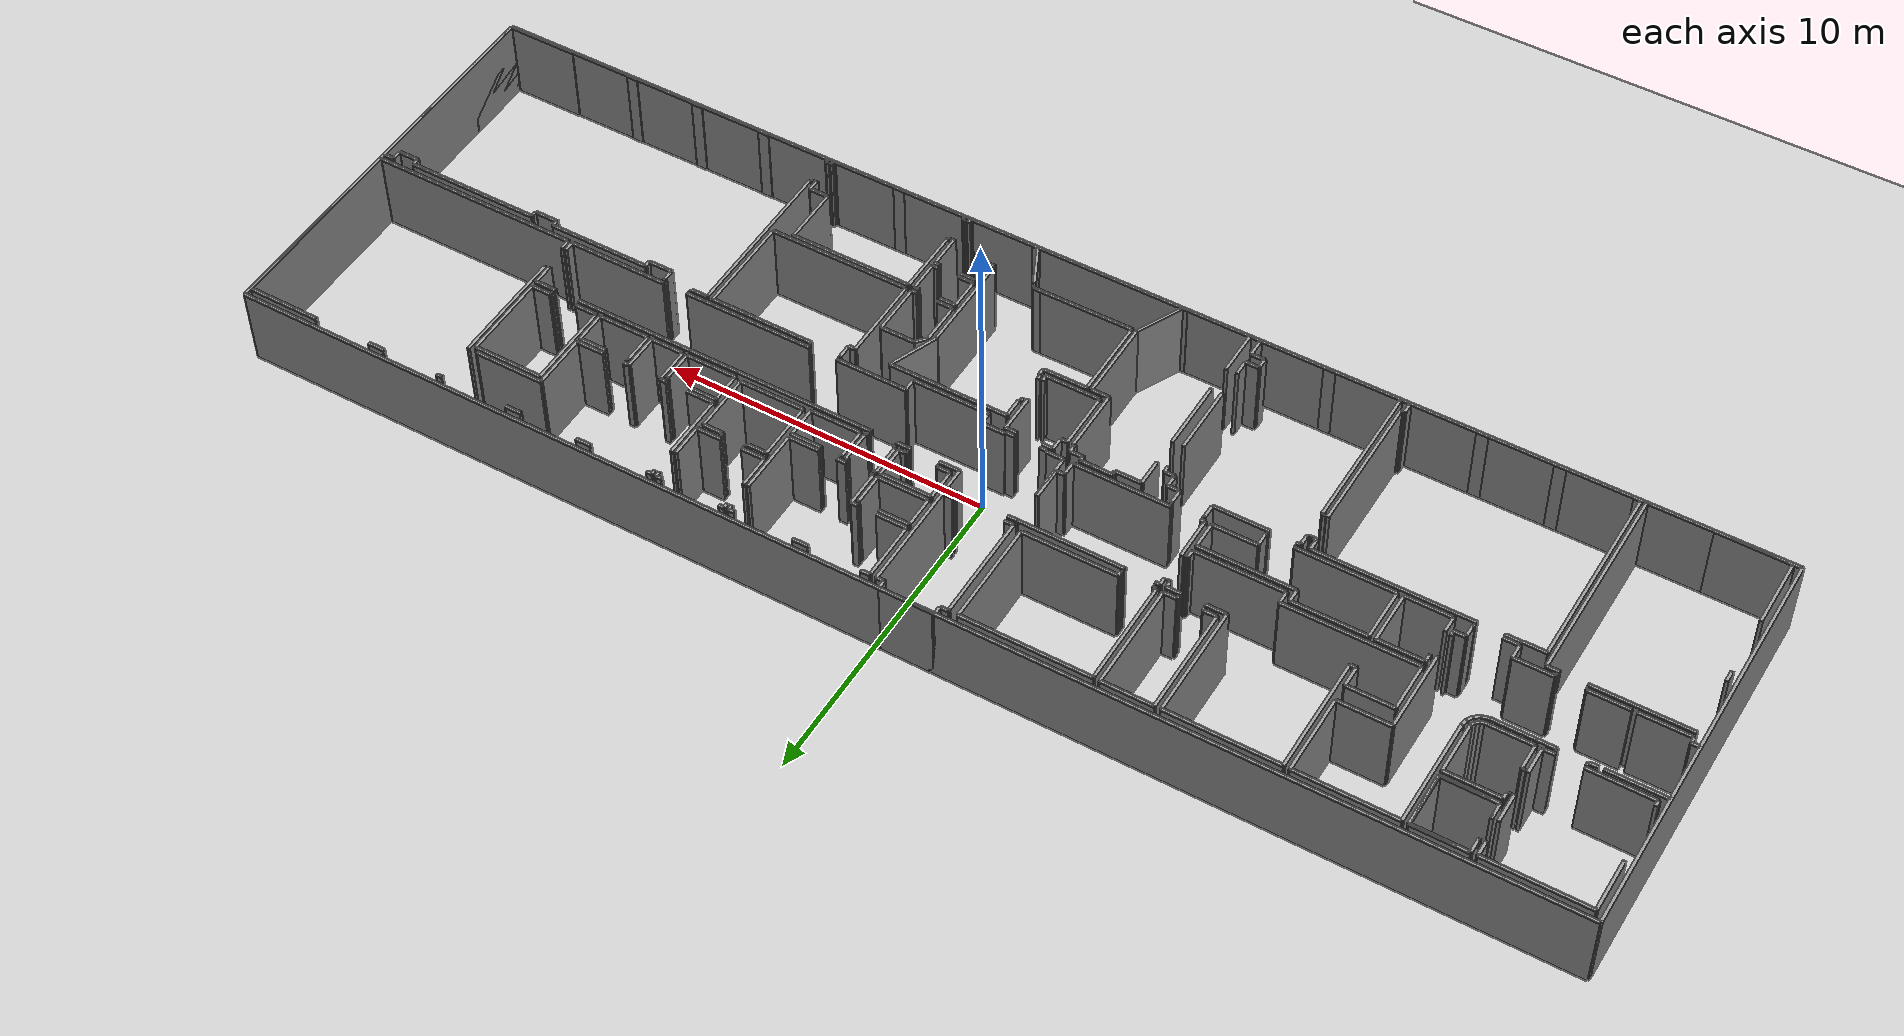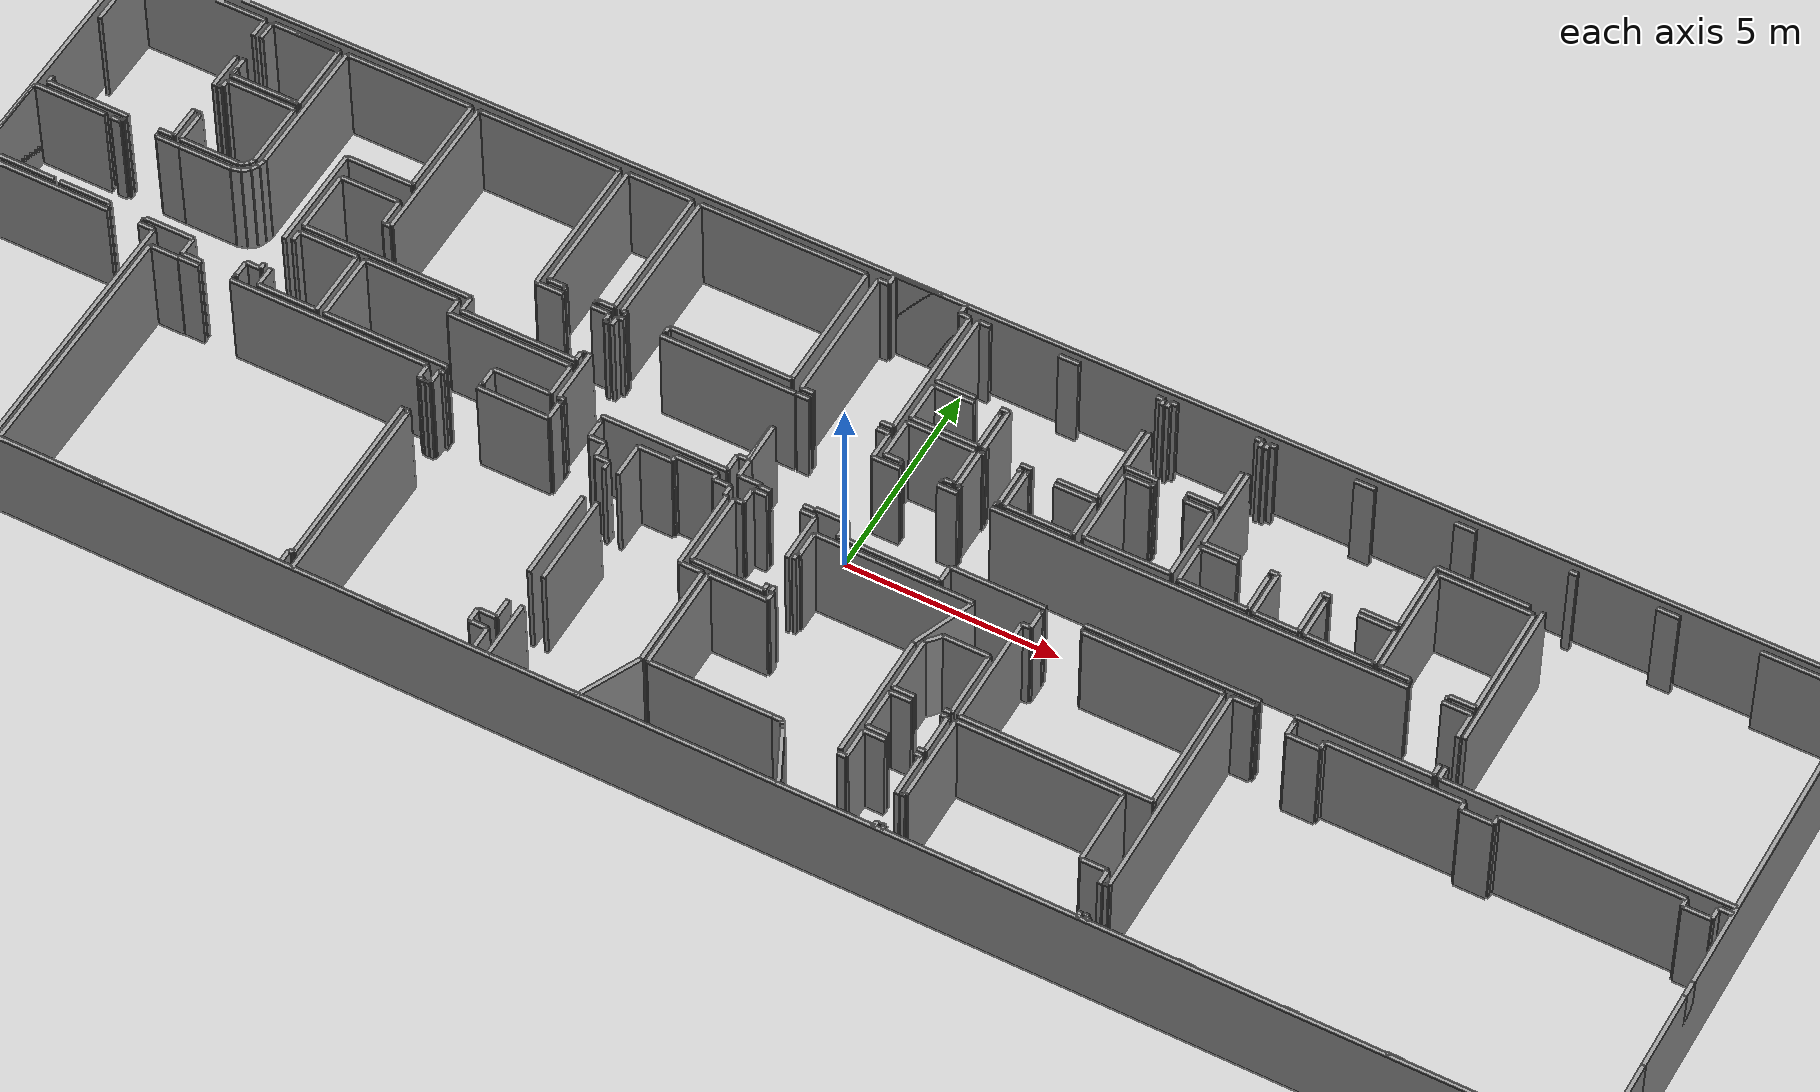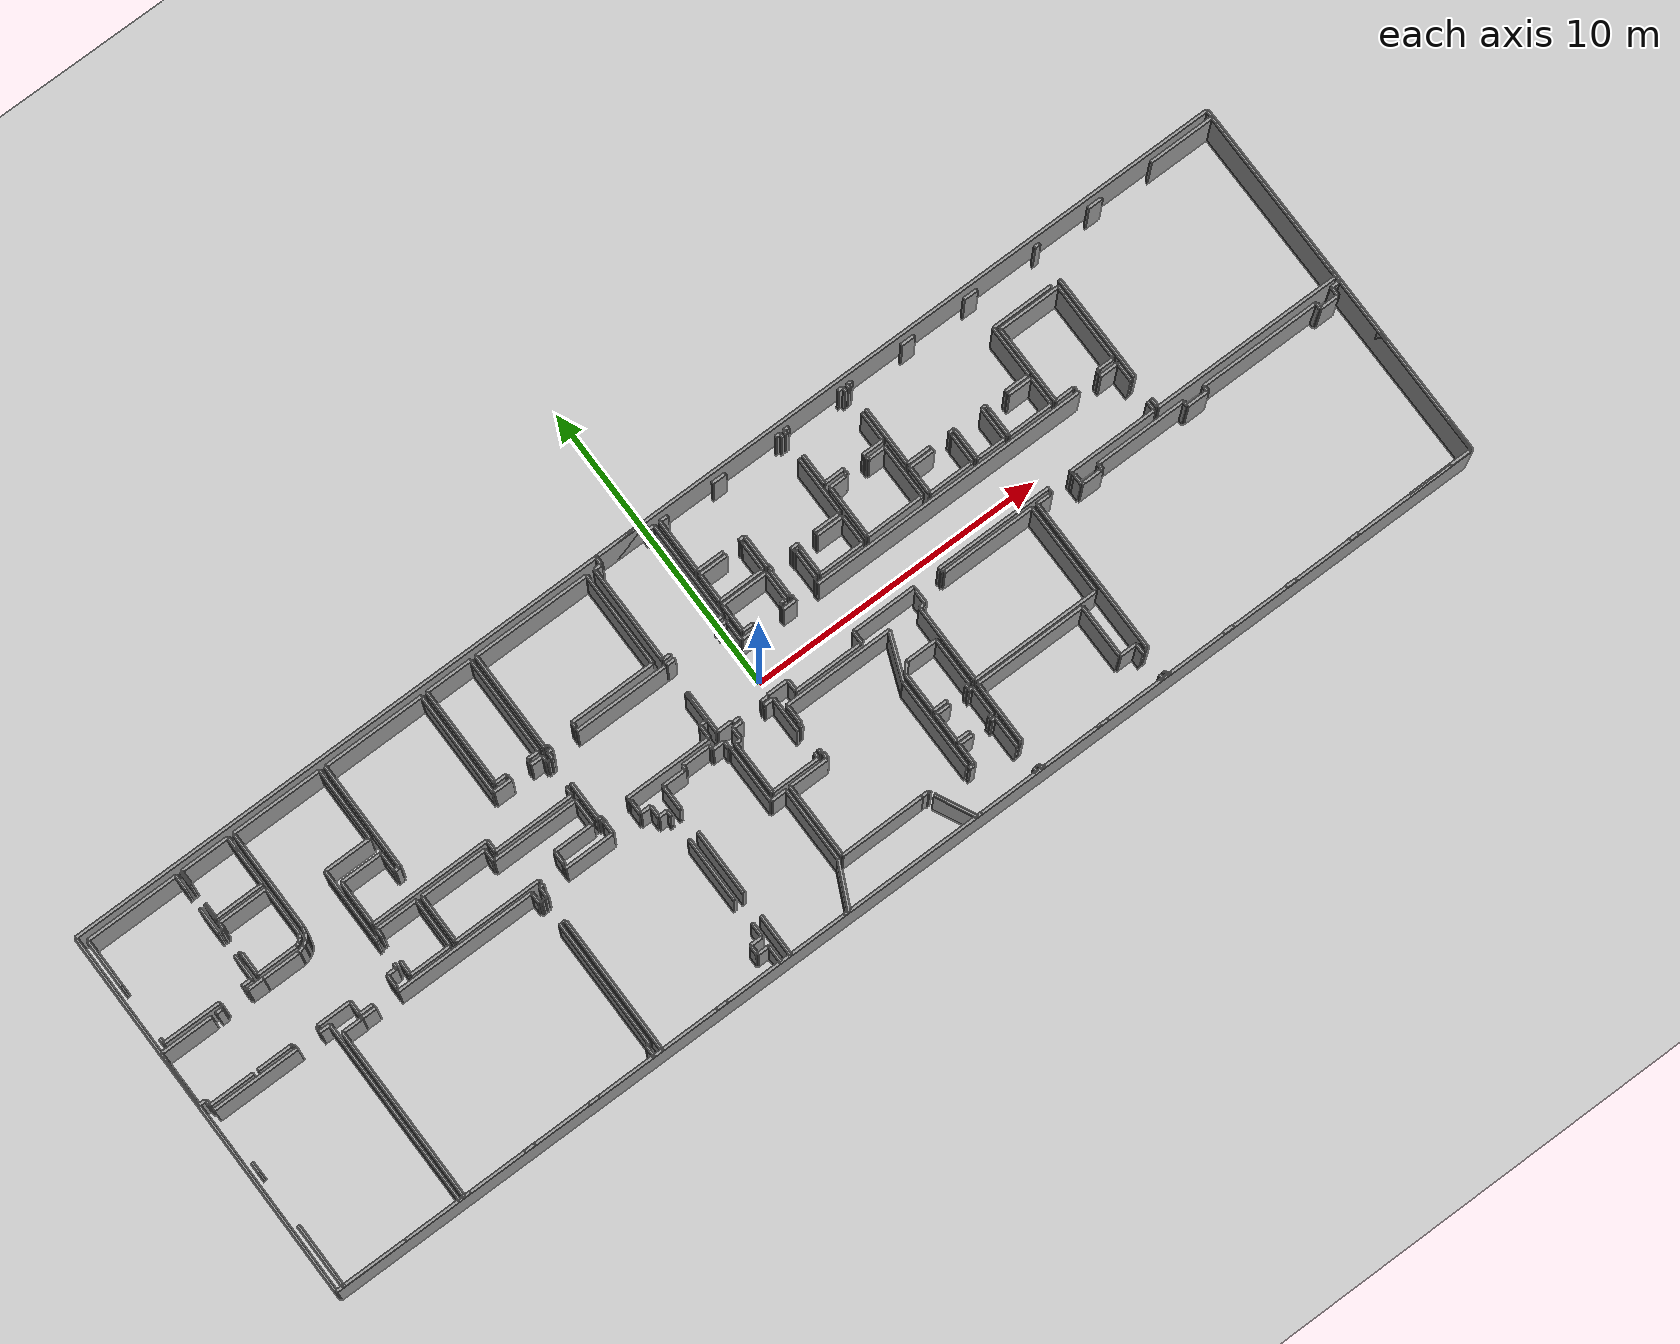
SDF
<sdf version="1.6">
  <world name="default">
    <light name="sun" type="directional">
      <cast_shadows>1</cast_shadows>
      <pose frame="">0 0 10 0 -0 0</pose>
      <diffuse>0.8 0.8 0.8 1</diffuse>
      <specular>0.1 0.1 0.1 1</specular>
      <attenuation>
        <range>1000</range>
        <constant>0.9</constant>
        <linear>0.01</linear>
        <quadratic>0.001</quadratic>
      </attenuation>
      <direction>-0.5 0.5 -1</direction>
    </light>
    <model name="ground_plane">
      <static>1</static>
      <link name="link">
        <collision name="collision">
          <geometry>
            <plane>
              <normal>0 0 1</normal>
              <size>100 100</size>
            </plane>
          </geometry>
          <surface>
            <friction>
              <ode>
                <mu>100</mu>
                <mu2>50</mu2>
              </ode>
              <torsional>
                <ode />
              </torsional>
            </friction>
            <contact>
              <ode />
            </contact>
            <bounce />
          </surface>
          <max_contacts>10</max_contacts>
        </collision>
        <visual name="visual">
          <cast_shadows>0</cast_shadows>
          <geometry>
            <plane>
              <normal>0 0 1</normal>
              <size>100 100</size>
            </plane>
          </geometry>
          <material>
            <script>
              <uri>file://media/materials/scripts/gazebo.material</uri>
              <name>Gazebo/Grey</name>
            </script>
          </material>
        </visual>
        <self_collide>0</self_collide>
        <kinematic>0</kinematic>
        <gravity>1</gravity>
      </link>
    </model>
    <gravity>0 0 -9.8</gravity>
    <magnetic_field>6e-06 2.3e-05 -4.2e-05</magnetic_field>
    <atmosphere type="adiabatic" />
    <physics default="0" name="default_physics" type="ode">
      <max_step_size>0.001</max_step_size>
      <real_time_factor>1</real_time_factor>
      <real_time_update_rate>1000</real_time_update_rate>
    </physics>
    <scene>
      <ambient>0.4 0.4 0.4 1</ambient>
      <background>0.7 0.7 0.7 1</background>
      <shadows>1</shadows>
    </scene>
    <spherical_coordinates>
      <surface_model>EARTH_WGS84</surface_model>
      <latitude_deg>0</latitude_deg>
      <longitude_deg>0</longitude_deg>
      <elevation>0</elevation>
      <heading_deg>0</heading_deg>
    </spherical_coordinates>
  <model name="0510025537_Layout1_PLAN1">
		<static>1</static>
		<link name="Wall_0">
			<collision name="Wall_0_Collision">
				<geometry>
					<box>
						<size>1.64923428862 0.1 2.5</size>
					</box>
				</geometry>
				<pose frame="">0.82461714431 0 1.25 0 0 0</pose>
			</collision>
			<visual name="Wall_0_Visual">
				<pose frame="">0.82461714431 0 1.25 0 0 0</pose>
				<geometry>
					<box>
						<size>1.64923428862 0.1 2.5</size>
					</box>
				</geometry>
				<material>
					<script>
						<uri>file://media/materials/scripts/gazebo.material</uri>
						<name>Gazebo/Grey</name>
					</script>
					<ambient>1 1 1 1</ambient>
				</material>
			</visual>
			<pose frame="">3.54533900998 -0.258549914215 0 0 0 0.0</pose>
		</link>
		<link name="Wall_1">
			<collision name="Wall_1_Collision">
				<geometry>
					<box>
						<size>1.68164199021 0.1 2.5</size>
					</box>
				</geometry>
				<pose frame="">0.840820995107 0 1.25 0 0 0</pose>
			</collision>
			<visual name="Wall_1_Visual">
				<pose frame="">0.840820995107 0 1.25 0 0 0</pose>
				<geometry>
					<box>
						<size>1.68164199021 0.1 2.5</size>
					</box>
				</geometry>
				<material>
					<script>
						<uri>file://media/materials/scripts/gazebo.material</uri>
						<name>Gazebo/Grey</name>
					</script>
					<ambient>1 1 1 1</ambient>
				</material>
			</visual>
			<pose frame="">5.1945732986 -0.258549914215 0 0 0 -1.57079632679</pose>
		</link>
		<link name="Wall_2">
			<collision name="Wall_2_Collision">
				<geometry>
					<box>
						<size>1.65457202771 0.1 2.5</size>
					</box>
				</geometry>
				<pose frame="">0.827286013853 0 1.25 0 0 0</pose>
			</collision>
			<visual name="Wall_2_Visual">
				<pose frame="">0.827286013853 0 1.25 0 0 0</pose>
				<geometry>
					<box>
						<size>1.65457202771 0.1 2.5</size>
					</box>
				</geometry>
				<material>
					<script>
						<uri>file://media/materials/scripts/gazebo.material</uri>
						<name>Gazebo/Grey</name>
					</script>
					<ambient>1 1 1 1</ambient>
				</material>
			</visual>
			<pose frame="">5.1945732986 -1.94019190443 0 0 0 3.14159265359</pose>
		</link>
		<link name="Wall_3">
			<collision name="Wall_3_Collision">
				<geometry>
					<box>
						<size>0.517735273559 0.1 2.5</size>
					</box>
				</geometry>
				<pose frame="">0.25886763678 0 1.25 0 0 0</pose>
			</collision>
			<visual name="Wall_3_Visual">
				<pose frame="">0.25886763678 0 1.25 0 0 0</pose>
				<geometry>
					<box>
						<size>0.517735273559 0.1 2.5</size>
					</box>
				</geometry>
				<material>
					<script>
						<uri>file://media/materials/scripts/gazebo.material</uri>
						<name>Gazebo/Grey</name>
					</script>
					<ambient>1 1 1 1</ambient>
				</material>
			</visual>
			<pose frame="">3.54000127089 -1.94019190443 0 0 0 1.57079632679</pose>
		</link>
		<link name="Wall_4">
			<collision name="Wall_4_Collision">
				<geometry>
					<box>
						<size>0.475292094639 0.1 2.5</size>
					</box>
				</geometry>
				<pose frame="">0.237646047319 0 1.25 0 0 0</pose>
			</collision>
			<visual name="Wall_4_Visual">
				<pose frame="">0.237646047319 0 1.25 0 0 0</pose>
				<geometry>
					<box>
						<size>0.475292094639 0.1 2.5</size>
					</box>
				</geometry>
				<material>
					<script>
						<uri>file://media/materials/scripts/gazebo.material</uri>
						<name>Gazebo/Grey</name>
					</script>
					<ambient>1 1 1 1</ambient>
				</material>
			</visual>
			<pose frame="">3.54000127089 -0.733812035331 0 0 0 1.55956565127</pose>
		</link>
		<link name="Wall_5">
			<collision name="Wall_5_Collision">
				<geometry>
					<box>
						<size>0.523841901252 0.1 2.5</size>
					</box>
				</geometry>
				<pose frame="">0.261920950626 0 1.25 0 0 0</pose>
			</collision>
			<visual name="Wall_5_Visual">
				<pose frame="">0.261920950626 0 1.25 0 0 0</pose>
				<geometry>
					<box>
						<size>0.523841901252 0.1 2.5</size>
					</box>
				</geometry>
				<material>
					<script>
						<uri>file://media/materials/scripts/gazebo.material</uri>
						<name>Gazebo/Grey</name>
					</script>
					<ambient>1 1 1 1</ambient>
				</material>
			</visual>
			<pose frame="">3.54000127089 -1.94221261994 0 0 0 1.57079632679</pose>
		</link>
		<link name="Wall_6">
			<collision name="Wall_6_Collision">
				<geometry>
					<box>
						<size>0.4837834403 0.1 2.5</size>
					</box>
				</geometry>
				<pose frame="">0.24189172015 0 1.25 0 0 0</pose>
			</collision>
			<visual name="Wall_6_Visual">
				<pose frame="">0.24189172015 0 1.25 0 0 0</pose>
				<geometry>
					<box>
						<size>0.4837834403 0.1 2.5</size>
					</box>
				</geometry>
				<material>
					<script>
						<uri>file://media/materials/scripts/gazebo.material</uri>
						<name>Gazebo/Grey</name>
					</script>
					<ambient>1 1 1 1</ambient>
				</material>
			</visual>
			<pose frame="">3.54000127089 -0.739194255576 0 0 0 1.57079632679</pose>
		</link>
		<link name="Wall_7">
			<collision name="Wall_7_Collision">
				<geometry>
					<box>
						<size>1.66404016013 0.1 2.5</size>
					</box>
				</geometry>
				<pose frame="">0.832020080066 0 1.25 0 0 0</pose>
			</collision>
			<visual name="Wall_7_Visual">
				<pose frame="">0.832020080066 0 1.25 0 0 0</pose>
				<geometry>
					<box>
						<size>1.66404016013 0.1 2.5</size>
					</box>
				</geometry>
				<material>
					<script>
						<uri>file://media/materials/scripts/gazebo.material</uri>
						<name>Gazebo/Grey</name>
					</script>
					<ambient>1 1 1 1</ambient>
				</material>
			</visual>
			<pose frame="">3.54000127089 -0.255410815276 0 0 0 0.0</pose>
		</link>
		<link name="Wall_8">
			<collision name="Wall_8_Collision">
				<geometry>
					<box>
						<size>1.68915295164 0.1 2.5</size>
					</box>
				</geometry>
				<pose frame="">0.844576475821 0 1.25 0 0 0</pose>
			</collision>
			<visual name="Wall_8_Visual">
				<pose frame="">0.844576475821 0 1.25 0 0 0</pose>
				<geometry>
					<box>
						<size>1.68915295164 0.1 2.5</size>
					</box>
				</geometry>
				<material>
					<script>
						<uri>file://media/materials/scripts/gazebo.material</uri>
						<name>Gazebo/Grey</name>
					</script>
					<ambient>1 1 1 1</ambient>
				</material>
			</visual>
			<pose frame="">5.20404143102 -0.255410815276 0 0 0 -1.57079632679</pose>
		</link>
		<link name="Wall_9">
			<collision name="Wall_9_Collision">
				<geometry>
					<box>
						<size>1.66588295101 0.1 2.5</size>
					</box>
				</geometry>
				<pose frame="">0.832941475504 0 1.25 0 0 0</pose>
			</collision>
			<visual name="Wall_9_Visual">
				<pose frame="">0.832941475504 0 1.25 0 0 0</pose>
				<geometry>
					<box>
						<size>1.66588295101 0.1 2.5</size>
					</box>
				</geometry>
				<material>
					<script>
						<uri>file://media/materials/scripts/gazebo.material</uri>
						<name>Gazebo/Grey</name>
					</script>
					<ambient>1 1 1 1</ambient>
				</material>
			</visual>
			<pose frame="">5.20404143102 -1.94456376692 0 0 0 3.14159265359</pose>
		</link>
		<link name="Wall_10">
			<collision name="Wall_10_Collision">
				<geometry>
					<box>
						<size>0.528391688378 0.1 2.5</size>
					</box>
				</geometry>
				<pose frame="">0.264195844189 0 1.25 0 0 0</pose>
			</collision>
			<visual name="Wall_10_Visual">
				<pose frame="">0.264195844189 0 1.25 0 0 0</pose>
				<geometry>
					<box>
						<size>0.528391688378 0.1 2.5</size>
					</box>
				</geometry>
				<material>
					<script>
						<uri>file://media/materials/scripts/gazebo.material</uri>
						<name>Gazebo/Grey</name>
					</script>
					<ambient>1 1 1 1</ambient>
				</material>
			</visual>
			<pose frame="">3.53815848002 -1.94456376692 0 0 0 1.57079632679</pose>
		</link>
		<link name="Wall_11">
			<collision name="Wall_11_Collision">
				<geometry>
					<box>
						<size>0.476745950657 0.1 2.5</size>
					</box>
				</geometry>
				<pose frame="">0.238372975328 0 1.25 0 0 0</pose>
			</collision>
			<visual name="Wall_11_Visual">
				<pose frame="">0.238372975328 0 1.25 0 0 0</pose>
				<geometry>
					<box>
						<size>0.476745950657 0.1 2.5</size>
					</box>
				</geometry>
				<material>
					<script>
						<uri>file://media/materials/scripts/gazebo.material</uri>
						<name>Gazebo/Grey</name>
					</script>
					<ambient>1 1 1 1</ambient>
				</material>
			</visual>
			<pose frame="">3.53815848002 -0.735241786872 0 0 0 1.5557342136</pose>
		</link>
		<link name="Wall_12">
			<collision name="Wall_12_Collision">
				<geometry>
					<box>
						<size>0.788523860965 0.1 2.5</size>
					</box>
				</geometry>
				<pose frame="">0.394261930482 0 1.25 0 0 0</pose>
			</collision>
			<visual name="Wall_12_Visual">
				<pose frame="">0.394261930482 0 1.25 0 0 0</pose>
				<geometry>
					<box>
						<size>0.788523860965 0.1 2.5</size>
					</box>
				</geometry>
				<material>
					<script>
						<uri>file://media/materials/scripts/gazebo.material</uri>
						<name>Gazebo/Grey</name>
					</script>
					<ambient>1 1 1 1</ambient>
				</material>
			</visual>
			<pose frame="">3.54178051725 -3.9739340408 0 0 0 1.57079632679</pose>
		</link>
		<link name="Wall_13">
			<collision name="Wall_13_Collision">
				<geometry>
					<box>
						<size>0.0599224756942 0.1 2.5</size>
					</box>
				</geometry>
				<pose frame="">0.0299612378471 0 1.25 0 0 0</pose>
			</collision>
			<visual name="Wall_13_Visual">
				<pose frame="">0.0299612378471 0 1.25 0 0 0</pose>
				<geometry>
					<box>
						<size>0.0599224756942 0.1 2.5</size>
					</box>
				</geometry>
				<material>
					<script>
						<uri>file://media/materials/scripts/gazebo.material</uri>
						<name>Gazebo/Grey</name>
					</script>
					<ambient>1 1 1 1</ambient>
				</material>
			</visual>
			<pose frame="">3.54178051725 -3.18541017983 0 0 0 3.14159265359</pose>
		</link>
		<link name="Wall_14">
			<collision name="Wall_14_Collision">
				<geometry>
					<box>
						<size>0.0581432293321 0.1 2.5</size>
					</box>
				</geometry>
				<pose frame="">0.0290716146661 0 1.25 0 0 0</pose>
			</collision>
			<visual name="Wall_14_Visual">
				<pose frame="">0.0290716146661 0 1.25 0 0 0</pose>
				<geometry>
					<box>
						<size>0.0581432293321 0.1 2.5</size>
					</box>
				</geometry>
				<material>
					<script>
						<uri>file://media/materials/scripts/gazebo.material</uri>
						<name>Gazebo/Grey</name>
					</script>
					<ambient>1 1 1 1</ambient>
				</material>
			</visual>
			<pose frame="">3.48185804156 -3.18541017983 0 0 0 1.57079632679</pose>
		</link>
		<link name="Wall_15">
			<collision name="Wall_15_Collision">
				<geometry>
					<box>
						<size>0.0581114570757 0.1 2.5</size>
					</box>
				</geometry>
				<pose frame="">0.0290557285378 0 1.25 0 0 0</pose>
			</collision>
			<visual name="Wall_15_Visual">
				<pose frame="">0.0290557285378 0 1.25 0 0 0</pose>
				<geometry>
					<box>
						<size>0.0581114570757 0.1 2.5</size>
					</box>
				</geometry>
				<material>
					<script>
						<uri>file://media/materials/scripts/gazebo.material</uri>
						<name>Gazebo/Grey</name>
					</script>
					<ambient>1 1 1 1</ambient>
				</material>
			</visual>
			<pose frame="">3.48185804156 -2.36017665375 0 0 0 1.57079632679</pose>
		</link>
		<link name="Wall_16">
			<collision name="Wall_16_Collision">
				<geometry>
					<box>
						<size>0.0618923555951 0.1 2.5</size>
					</box>
				</geometry>
				<pose frame="">0.0309461777975 0 1.25 0 0 0</pose>
			</collision>
			<visual name="Wall_16_Visual">
				<pose frame="">0.0309461777975 0 1.25 0 0 0</pose>
				<geometry>
					<box>
						<size>0.0618923555951 0.1 2.5</size>
					</box>
				</geometry>
				<material>
					<script>
						<uri>file://media/materials/scripts/gazebo.material</uri>
						<name>Gazebo/Grey</name>
					</script>
					<ambient>1 1 1 1</ambient>
				</material>
			</visual>
			<pose frame="">3.48185804156 -2.30206519667 0 0 0 0.0</pose>
		</link>
		<link name="Wall_17">
			<collision name="Wall_17_Collision">
				<geometry>
					<box>
						<size>0.193200737116 0.1 2.5</size>
					</box>
				</geometry>
				<pose frame="">0.0966003685582 0 1.25 0 0 0</pose>
			</collision>
			<visual name="Wall_17_Visual">
				<pose frame="">0.0966003685582 0 1.25 0 0 0</pose>
				<geometry>
					<box>
						<size>0.193200737116 0.1 2.5</size>
					</box>
				</geometry>
				<material>
					<script>
						<uri>file://media/materials/scripts/gazebo.material</uri>
						<name>Gazebo/Grey</name>
					</script>
					<ambient>1 1 1 1</ambient>
				</material>
			</visual>
			<pose frame="">3.54375039715 -2.30206519667 0 0 0 1.57079632679</pose>
		</link>
		<link name="Wall_18">
			<collision name="Wall_18_Collision">
				<geometry>
					<box>
						<size>1.65984622228 0.1 2.5</size>
					</box>
				</geometry>
				<pose frame="">0.829923111139 0 1.25 0 0 0</pose>
			</collision>
			<visual name="Wall_18_Visual">
				<pose frame="">0.829923111139 0 1.25 0 0 0</pose>
				<geometry>
					<box>
						<size>1.65984622228 0.1 2.5</size>
					</box>
				</geometry>
				<material>
					<script>
						<uri>file://media/materials/scripts/gazebo.material</uri>
						<name>Gazebo/Grey</name>
					</script>
					<ambient>1 1 1 1</ambient>
				</material>
			</visual>
			<pose frame="">3.54375039715 -2.10886445955 0 0 0 0.0</pose>
		</link>
		<link name="Wall_19">
			<collision name="Wall_19_Collision">
				<geometry>
					<box>
						<size>1.62398169918 0.1 2.5</size>
					</box>
				</geometry>
				<pose frame="">0.81199084959 0 1.25 0 0 0</pose>
			</collision>
			<visual name="Wall_19_Visual">
				<pose frame="">0.81199084959 0 1.25 0 0 0</pose>
				<geometry>
					<box>
						<size>1.62398169918 0.1 2.5</size>
					</box>
				</geometry>
				<material>
					<script>
						<uri>file://media/materials/scripts/gazebo.material</uri>
						<name>Gazebo/Grey</name>
					</script>
					<ambient>1 1 1 1</ambient>
				</material>
			</visual>
			<pose frame="">5.20359661943 -2.10886445955 0 0 0 -1.57079632679</pose>
		</link>
		<link name="Wall_20">
			<collision name="Wall_20_Collision">
				<geometry>
					<box>
						<size>0.123572431417 0.1 2.5</size>
					</box>
				</geometry>
				<pose frame="">0.0617862157083 0 1.25 0 0 0</pose>
			</collision>
			<visual name="Wall_20_Visual">
				<pose frame="">0.0617862157083 0 1.25 0 0 0</pose>
				<geometry>
					<box>
						<size>0.123572431417 0.1 2.5</size>
					</box>
				</geometry>
				<material>
					<script>
						<uri>file://media/materials/scripts/gazebo.material</uri>
						<name>Gazebo/Grey</name>
					</script>
					<ambient>1 1 1 1</ambient>
				</material>
			</visual>
			<pose frame="">5.20359661943 -3.73284615873 0 0 0 -2.09657584292</pose>
		</link>
		<link name="Wall_21">
			<collision name="Wall_21_Collision">
				<geometry>
					<box>
						<size>0.124756927835 0.1 2.5</size>
					</box>
				</geometry>
				<pose frame="">0.0623784639175 0 1.25 0 0 0</pose>
			</collision>
			<visual name="Wall_21_Visual">
				<pose frame="">0.0623784639175 0 1.25 0 0 0</pose>
				<geometry>
					<box>
						<size>0.124756927835 0.1 2.5</size>
					</box>
				</geometry>
				<material>
					<script>
						<uri>file://media/materials/scripts/gazebo.material</uri>
						<name>Gazebo/Grey</name>
					</script>
					<ambient>1 1 1 1</ambient>
				</material>
			</visual>
			<pose frame="">5.14157717481 -3.83972802948 0 0 0 -2.37564448673</pose>
		</link>
		<link name="Wall_22">
			<collision name="Wall_22_Collision">
				<geometry>
					<box>
						<size>0.126291773989 0.1 2.5</size>
					</box>
				</geometry>
				<pose frame="">0.0631458869943 0 1.25 0 0 0</pose>
			</collision>
			<visual name="Wall_22_Visual">
				<pose frame="">0.0631458869943 0 1.25 0 0 0</pose>
				<geometry>
					<box>
						<size>0.126291773989 0.1 2.5</size>
					</box>
				</geometry>
				<material>
					<script>
						<uri>file://media/materials/scripts/gazebo.material</uri>
						<name>Gazebo/Grey</name>
					</script>
					<ambient>1 1 1 1</ambient>
				</material>
			</visual>
			<pose frame="">5.05166168901 -3.92621211158 0 0 0 -2.77304608745</pose>
		</link>
		<link name="Wall_23">
			<collision name="Wall_23_Collision">
				<geometry>
					<box>
						<size>1.39207142143 0.1 2.5</size>
					</box>
				</geometry>
				<pose frame="">0.696035710716 0 1.25 0 0 0</pose>
			</collision>
			<visual name="Wall_23_Visual">
				<pose frame="">0.696035710716 0 1.25 0 0 0</pose>
				<geometry>
					<box>
						<size>1.39207142143 0.1 2.5</size>
					</box>
				</geometry>
				<material>
					<script>
						<uri>file://media/materials/scripts/gazebo.material</uri>
						<name>Gazebo/Grey</name>
					</script>
					<ambient>1 1 1 1</ambient>
				</material>
			</visual>
			<pose frame="">4.93385016204 -3.97170998284 0 0 0 -3.1399949921</pose>
		</link>
		<link name="Wall_24">
			<collision name="Wall_24_Collision">
				<geometry>
					<box>
						<size>0.175255766665 0.1 2.5</size>
					</box>
				</geometry>
				<pose frame="">0.0876278833323 0 1.25 0 0 0</pose>
			</collision>
			<visual name="Wall_24_Visual">
				<pose frame="">0.0876278833323 0 1.25 0 0 0</pose>
				<geometry>
					<box>
						<size>0.175255766665 0.1 2.5</size>
					</box>
				</geometry>
				<material>
					<script>
						<uri>file://media/materials/scripts/gazebo.material</uri>
						<name>Gazebo/Grey</name>
					</script>
					<ambient>1 1 1 1</ambient>
				</material>
			</visual>
			<pose frame="">0.234415708204 -3.96713477791 0 0 0 1.57079632679</pose>
		</link>
		<link name="Wall_25">
			<collision name="Wall_25_Collision">
				<geometry>
					<box>
						<size>1.64880218593 0.1 2.5</size>
					</box>
				</geometry>
				<pose frame="">0.824401092966 0 1.25 0 0 0</pose>
			</collision>
			<visual name="Wall_25_Visual">
				<pose frame="">0.824401092966 0 1.25 0 0 0</pose>
				<geometry>
					<box>
						<size>1.64880218593 0.1 2.5</size>
					</box>
				</geometry>
				<material>
					<script>
						<uri>file://media/materials/scripts/gazebo.material</uri>
						<name>Gazebo/Grey</name>
					</script>
					<ambient>1 1 1 1</ambient>
				</material>
			</visual>
			<pose frame="">0.234415708204 -1.91654063672 0 0 0 1.57079632679</pose>
		</link>
		<link name="Wall_26">
			<collision name="Wall_26_Collision">
				<geometry>
					<box>
						<size>3.12130647519 0.1 2.5</size>
					</box>
				</geometry>
				<pose frame="">1.56065323759 0 1.25 0 0 0</pose>
			</collision>
			<visual name="Wall_26_Visual">
				<pose frame="">1.56065323759 0 1.25 0 0 0</pose>
				<geometry>
					<box>
						<size>3.12130647519 0.1 2.5</size>
					</box>
				</geometry>
				<material>
					<script>
						<uri>file://media/materials/scripts/gazebo.material</uri>
						<name>Gazebo/Grey</name>
					</script>
					<ambient>1 1 1 1</ambient>
				</material>
			</visual>
			<pose frame="">0.234415708204 -0.267738450785 0 0 0 0.0</pose>
		</link>
		<link name="Wall_27">
			<collision name="Wall_27_Collision">
				<geometry>
					<box>
						<size>0.48933723073 0.1 2.5</size>
					</box>
				</geometry>
				<pose frame="">0.244668615365 0 1.25 0 0 0</pose>
			</collision>
			<visual name="Wall_27_Visual">
				<pose frame="">0.244668615365 0 1.25 0 0 0</pose>
				<geometry>
					<box>
						<size>0.48933723073 0.1 2.5</size>
					</box>
				</geometry>
				<material>
					<script>
						<uri>file://media/materials/scripts/gazebo.material</uri>
						<name>Gazebo/Grey</name>
					</script>
					<ambient>1 1 1 1</ambient>
				</material>
			</visual>
			<pose frame="">3.35572218339 -0.267738450785 0 0 0 -1.57079632679</pose>
		</link>
		<link name="Wall_28">
			<collision name="Wall_28_Collision">
				<geometry>
					<box>
						<size>0.924286712842 0.1 2.5</size>
					</box>
				</geometry>
				<pose frame="">0.462143356421 0 1.25 0 0 0</pose>
			</collision>
			<visual name="Wall_28_Visual">
				<pose frame="">0.462143356421 0 1.25 0 0 0</pose>
				<geometry>
					<box>
						<size>0.924286712842 0.1 2.5</size>
					</box>
				</geometry>
				<material>
					<script>
						<uri>file://media/materials/scripts/gazebo.material</uri>
						<name>Gazebo/Grey</name>
					</script>
					<ambient>1 1 1 1</ambient>
				</material>
			</visual>
			<pose frame="">3.35572218339 -1.4363474614 0 0 0 -1.57079632679</pose>
		</link>
		<link name="Wall_29">
			<collision name="Wall_29_Collision">
				<geometry>
					<box>
						<size>0.844252398805 0.1 2.5</size>
					</box>
				</geometry>
				<pose frame="">0.422126199403 0 1.25 0 0 0</pose>
			</collision>
			<visual name="Wall_29_Visual">
				<pose frame="">0.422126199403 0 1.25 0 0 0</pose>
				<geometry>
					<box>
						<size>0.844252398805 0.1 2.5</size>
					</box>
				</geometry>
				<material>
					<script>
						<uri>file://media/materials/scripts/gazebo.material</uri>
						<name>Gazebo/Grey</name>
					</script>
					<ambient>1 1 1 1</ambient>
				</material>
			</visual>
			<pose frame="">3.35572218339 -3.13222342251 0 0 0 -1.57079632679</pose>
		</link>
		<link name="Wall_30">
			<collision name="Wall_30_Collision">
				<geometry>
					<box>
						<size>0.364872593252 0.1 2.5</size>
					</box>
				</geometry>
				<pose frame="">0.182436296626 0 1.25 0 0 0</pose>
			</collision>
			<visual name="Wall_30_Visual">
				<pose frame="">0.182436296626 0 1.25 0 0 0</pose>
				<geometry>
					<box>
						<size>0.364872593252 0.1 2.5</size>
					</box>
				</geometry>
				<material>
					<script>
						<uri>file://media/materials/scripts/gazebo.material</uri>
						<name>Gazebo/Grey</name>
					</script>
					<ambient>1 1 1 1</ambient>
				</material>
			</visual>
			<pose frame="">3.35572218339 -3.97647582131 0 0 0 3.14159265359</pose>
		</link>
		<link name="Wall_31">
			<collision name="Wall_31_Collision">
				<geometry>
					<box>
						<size>1.98655052484 0.1 2.5</size>
					</box>
				</geometry>
				<pose frame="">0.993275262419 0 1.25 0 0 0</pose>
			</collision>
			<visual name="Wall_31_Visual">
				<pose frame="">0.993275262419 0 1.25 0 0 0</pose>
				<geometry>
					<box>
						<size>1.98655052484 0.1 2.5</size>
					</box>
				</geometry>
				<material>
					<script>
						<uri>file://media/materials/scripts/gazebo.material</uri>
						<name>Gazebo/Grey</name>
					</script>
					<ambient>1 1 1 1</ambient>
				</material>
			</visual>
			<pose frame="">2.22094427146 -3.97647582131 0 0 0 3.13689049389</pose>
		</link>
		<link name="Wall_32">
			<collision name="Wall_32_Collision">
				<geometry>
					<box>
						<size>1.83713541336 0.1 2.5</size>
					</box>
				</geometry>
				<pose frame="">0.918567706679 0 1.25 0 0 0</pose>
			</collision>
			<visual name="Wall_32_Visual">
				<pose frame="">0.918567706679 0 1.25 0 0 0</pose>
				<geometry>
					<box>
						<size>1.83713541336 0.1 2.5</size>
					</box>
				</geometry>
				<material>
					<script>
						<uri>file://media/materials/scripts/gazebo.material</uri>
						<name>Gazebo/Grey</name>
					</script>
					<ambient>1 1 1 1</ambient>
				</material>
			</visual>
			<pose frame="">0.0 -6.00157590392 0 0 0 1.57079632679</pose>
		</link>
		<link name="Wall_33">
			<collision name="Wall_33_Collision">
				<geometry>
					<box>
						<size>1.78928639512 0.1 2.5</size>
					</box>
				</geometry>
				<pose frame="">0.89464319756 0 1.25 0 0 0</pose>
			</collision>
			<visual name="Wall_33_Visual">
				<pose frame="">0.89464319756 0 1.25 0 0 0</pose>
				<geometry>
					<box>
						<size>1.78928639512 0.1 2.5</size>
					</box>
				</geometry>
				<material>
					<script>
						<uri>file://media/materials/scripts/gazebo.material</uri>
						<name>Gazebo/Grey</name>
					</script>
					<ambient>1 1 1 1</ambient>
				</material>
			</visual>
			<pose frame="">0.0 -4.16444049056 0 0 0 0.0</pose>
		</link>
		<link name="Wall_34">
			<collision name="Wall_34_Collision">
				<geometry>
					<box>
						<size>1.54616508864 0.1 2.5</size>
					</box>
				</geometry>
				<pose frame="">0.773082544322 0 1.25 0 0 0</pose>
			</collision>
			<visual name="Wall_34_Visual">
				<pose frame="">0.773082544322 0 1.25 0 0 0</pose>
				<geometry>
					<box>
						<size>1.54616508864 0.1 2.5</size>
					</box>
				</geometry>
				<material>
					<script>
						<uri>file://media/materials/scripts/gazebo.material</uri>
						<name>Gazebo/Grey</name>
					</script>
					<ambient>1 1 1 1</ambient>
				</material>
			</visual>
			<pose frame="">1.78928639512 -6.19818262693 0 0 0 3.14159265359</pose>
		</link>
		<link name="Wall_35">
			<collision name="Wall_35_Collision">
				<geometry>
					<box>
						<size>0.193556586389 0.1 2.5</size>
					</box>
				</geometry>
				<pose frame="">0.0967782931944 0 1.25 0 0 0</pose>
			</collision>
			<visual name="Wall_35_Visual">
				<pose frame="">0.0967782931944 0 1.25 0 0 0</pose>
				<geometry>
					<box>
						<size>0.193556586389 0.1 2.5</size>
					</box>
				</geometry>
				<material>
					<script>
						<uri>file://media/materials/scripts/gazebo.material</uri>
						<name>Gazebo/Grey</name>
					</script>
					<ambient>1 1 1 1</ambient>
				</material>
			</visual>
			<pose frame="">0.243121306475 -6.19818262693 0 0 0 1.57079632679</pose>
		</link>
		<link name="Wall_36">
			<collision name="Wall_36_Collision">
				<geometry>
					<box>
						<size>0.243140438832 0.1 2.5</size>
					</box>
				</geometry>
				<pose frame="">0.121570219416 0 1.25 0 0 0</pose>
			</collision>
			<visual name="Wall_36_Visual">
				<pose frame="">0.121570219416 0 1.25 0 0 0</pose>
				<geometry>
					<box>
						<size>0.243140438832 0.1 2.5</size>
					</box>
				</geometry>
				<material>
					<script>
						<uri>file://media/materials/scripts/gazebo.material</uri>
						<name>Gazebo/Grey</name>
					</script>
					<ambient>1 1 1 1</ambient>
				</material>
			</visual>
			<pose frame="">0.243121306475 -6.00462604054 0 0 0 3.12904757207</pose>
		</link>
		<link name="Wall_37">
			<collision name="Wall_37_Collision">
				<geometry>
					<box>
						<size>2.1547944335 0.1 2.5</size>
					</box>
				</geometry>
				<pose frame="">1.07739721675 0 1.25 0 0 0</pose>
			</collision>
			<visual name="Wall_37_Visual">
				<pose frame="">1.07739721675 0 1.25 0 0 0</pose>
				<geometry>
					<box>
						<size>2.1547944335 0.1 2.5</size>
					</box>
				</geometry>
				<material>
					<script>
						<uri>file://media/materials/scripts/gazebo.material</uri>
						<name>Gazebo/Grey</name>
					</script>
					<ambient>1 1 1 1</ambient>
				</material>
			</visual>
			<pose frame="">0.248395501048 -12.6232954184 0 0 0 1.57079632679</pose>
		</link>
		<link name="Wall_38">
			<collision name="Wall_38_Collision">
				<geometry>
					<box>
						<size>0.353879392514 0.1 2.5</size>
					</box>
				</geometry>
				<pose frame="">0.176939696257 0 1.25 0 0 0</pose>
			</collision>
			<visual name="Wall_38_Visual">
				<pose frame="">0.176939696257 0 1.25 0 0 0</pose>
				<geometry>
					<box>
						<size>0.353879392514 0.1 2.5</size>
					</box>
				</geometry>
				<material>
					<script>
						<uri>file://media/materials/scripts/gazebo.material</uri>
						<name>Gazebo/Grey</name>
					</script>
					<ambient>1 1 1 1</ambient>
				</material>
			</visual>
			<pose frame="">0.248395501048 -8.59171379551 0 0 0 1.57079632679</pose>
		</link>
		<link name="Wall_39">
			<collision name="Wall_39_Collision">
				<geometry>
					<box>
						<size>2.97032471246 0.1 2.5</size>
					</box>
				</geometry>
				<pose frame="">1.48516235623 0 1.25 0 0 0</pose>
			</collision>
			<visual name="Wall_39_Visual">
				<pose frame="">1.48516235623 0 1.25 0 0 0</pose>
				<geometry>
					<box>
						<size>2.97032471246 0.1 2.5</size>
					</box>
				</geometry>
				<material>
					<script>
						<uri>file://media/materials/scripts/gazebo.material</uri>
						<name>Gazebo/Grey</name>
					</script>
					<ambient>1 1 1 1</ambient>
				</material>
			</visual>
			<pose frame="">0.248395501048 -6.37388320519 0 0 0 0.0</pose>
		</link>
		<link name="Wall_40">
			<collision name="Wall_40_Collision">
				<geometry>
					<box>
						<size>0.368176907924 0.1 2.5</size>
					</box>
				</geometry>
				<pose frame="">0.184088453962 0 1.25 0 0 0</pose>
			</collision>
			<visual name="Wall_40_Visual">
				<pose frame="">0.184088453962 0 1.25 0 0 0</pose>
				<geometry>
					<box>
						<size>0.368176907924 0.1 2.5</size>
					</box>
				</geometry>
				<material>
					<script>
						<uri>file://media/materials/scripts/gazebo.material</uri>
						<name>Gazebo/Grey</name>
					</script>
					<ambient>1 1 1 1</ambient>
				</material>
			</visual>
			<pose frame="">3.98481286141 -6.37388320519 0 0 0 0.0</pose>
		</link>
		<link name="Wall_41">
			<collision name="Wall_41_Collision">
				<geometry>
					<box>
						<size>6.26129503717 0.1 2.5</size>
					</box>
				</geometry>
				<pose frame="">3.13064751859 0 1.25 0 0 0</pose>
			</collision>
			<visual name="Wall_41_Visual">
				<pose frame="">3.13064751859 0 1.25 0 0 0</pose>
				<geometry>
					<box>
						<size>6.26129503717 0.1 2.5</size>
					</box>
				</geometry>
				<material>
					<script>
						<uri>file://media/materials/scripts/gazebo.material</uri>
						<name>Gazebo/Grey</name>
					</script>
					<ambient>1 1 1 1</ambient>
				</material>
			</visual>
			<pose frame="">4.35298976933 -6.37388320519 0 0 0 -1.57079632679</pose>
		</link>
		<link name="Wall_42">
			<collision name="Wall_42_Collision">
				<geometry>
					<box>
						<size>2.19898997621 0.1 2.5</size>
					</box>
				</geometry>
				<pose frame="">1.09949498811 0 1.25 0 0 0</pose>
			</collision>
			<visual name="Wall_42_Visual">
				<pose frame="">1.09949498811 0 1.25 0 0 0</pose>
				<geometry>
					<box>
						<size>2.19898997621 0.1 2.5</size>
					</box>
				</geometry>
				<material>
					<script>
						<uri>file://media/materials/scripts/gazebo.material</uri>
						<name>Gazebo/Grey</name>
					</script>
					<ambient>1 1 1 1</ambient>
				</material>
			</visual>
			<pose frame="">2.44735337104 -12.6351782424 0 0 0 3.13618886281</pose>
		</link>
		<link name="Wall_43">
			<collision name="Wall_43_Collision">
				<geometry>
					<box>
						<size>5.84736607994 0.1 2.5</size>
					</box>
				</geometry>
				<pose frame="">2.92368303997 0 1.25 0 0 0</pose>
			</collision>
			<visual name="Wall_43_Visual">
				<pose frame="">2.92368303997 0 1.25 0 0 0</pose>
				<geometry>
					<box>
						<size>5.84736607994 0.1 2.5</size>
					</box>
				</geometry>
				<material>
					<script>
						<uri>file://media/materials/scripts/gazebo.material</uri>
						<name>Gazebo/Grey</name>
					</script>
					<ambient>1 1 1 1</ambient>
				</material>
			</visual>
			<pose frame="">4.50854673699 -12.6251382093 0 0 0 1.57079632679</pose>
		</link>
		<link name="Wall_44">
			<collision name="Wall_44_Collision">
				<geometry>
					<box>
						<size>0.694859248904 0.1 2.5</size>
					</box>
				</geometry>
				<pose frame="">0.347429624452 0 1.25 0 0 0</pose>
			</collision>
			<visual name="Wall_44_Visual">
				<pose frame="">0.347429624452 0 1.25 0 0 0</pose>
				<geometry>
					<box>
						<size>0.694859248904 0.1 2.5</size>
					</box>
				</geometry>
				<material>
					<script>
						<uri>file://media/materials/scripts/gazebo.material</uri>
						<name>Gazebo/Grey</name>
					</script>
					<ambient>1 1 1 1</ambient>
				</material>
			</visual>
			<pose frame="">4.50854673699 -6.77777212938 0 0 0 0.0</pose>
		</link>
		<link name="Wall_45">
			<collision name="Wall_45_Collision">
				<geometry>
					<box>
						<size>0.0155684056682 0.1 2.5</size>
					</box>
				</geometry>
				<pose frame="">0.00778420283409 0 1.25 0 0 0</pose>
			</collision>
			<visual name="Wall_45_Visual">
				<pose frame="">0.00778420283409 0 1.25 0 0 0</pose>
				<geometry>
					<box>
						<size>0.0155684056682 0.1 2.5</size>
					</box>
				</geometry>
				<material>
					<script>
						<uri>file://media/materials/scripts/gazebo.material</uri>
						<name>Gazebo/Grey</name>
					</script>
					<ambient>1 1 1 1</ambient>
				</material>
			</visual>
			<pose frame="">5.20340598589 -6.77777212938 0 0 0 1.57079632679</pose>
		</link>
		<link name="Wall_46">
			<collision name="Wall_46_Collision">
				<geometry>
					<box>
						<size>0.495710745377 0.1 2.5</size>
					</box>
				</geometry>
				<pose frame="">0.247855372689 0 1.25 0 0 0</pose>
			</collision>
			<visual name="Wall_46_Visual">
				<pose frame="">0.247855372689 0 1.25 0 0 0</pose>
				<geometry>
					<box>
						<size>0.495710745377 0.1 2.5</size>
					</box>
				</geometry>
				<material>
					<script>
						<uri>file://media/materials/scripts/gazebo.material</uri>
						<name>Gazebo/Grey</name>
					</script>
					<ambient>1 1 1 1</ambient>
				</material>
			</visual>
			<pose frame="">5.20340598589 -6.76220372371 0 0 0 0.0</pose>
		</link>
		<link name="Wall_47">
			<collision name="Wall_47_Collision">
				<geometry>
					<box>
						<size>4.76253415518 0.1 2.5</size>
					</box>
				</geometry>
				<pose frame="">2.38126707759 0 1.25 0 0 0</pose>
			</collision>
			<visual name="Wall_47_Visual">
				<pose frame="">2.38126707759 0 1.25 0 0 0</pose>
				<geometry>
					<box>
						<size>4.76253415518 0.1 2.5</size>
					</box>
				</geometry>
				<material>
					<script>
						<uri>file://media/materials/scripts/gazebo.material</uri>
						<name>Gazebo/Grey</name>
					</script>
					<ambient>1 1 1 1</ambient>
				</material>
			</visual>
			<pose frame="">6.46622609138 -6.76220372371 0 0 0 0.0</pose>
		</link>
		<link name="Wall_48">
			<collision name="Wall_48_Collision">
				<geometry>
					<box>
						<size>0.365126771303 0.1 2.5</size>
					</box>
				</geometry>
				<pose frame="">0.182563385652 0 1.25 0 0 0</pose>
			</collision>
			<visual name="Wall_48_Visual">
				<pose frame="">0.182563385652 0 1.25 0 0 0</pose>
				<geometry>
					<box>
						<size>0.365126771303 0.1 2.5</size>
					</box>
				</geometry>
				<material>
					<script>
						<uri>file://media/materials/scripts/gazebo.material</uri>
						<name>Gazebo/Grey</name>
					</script>
					<ambient>1 1 1 1</ambient>
				</material>
			</visual>
			<pose frame="">11.2287602466 -6.76220372371 0 0 0 -1.57079632679</pose>
		</link>
		<link name="Wall_49">
			<collision name="Wall_49_Collision">
				<geometry>
					<box>
						<size>0.112092520811 0.1 2.5</size>
					</box>
				</geometry>
				<pose frame="">0.0560462604054 0 1.25 0 0 0</pose>
			</collision>
			<visual name="Wall_49_Visual">
				<pose frame="">0.0560462604054 0 1.25 0 0 0</pose>
				<geometry>
					<box>
						<size>0.112092520811 0.1 2.5</size>
					</box>
				</geometry>
				<material>
					<script>
						<uri>file://media/materials/scripts/gazebo.material</uri>
						<name>Gazebo/Grey</name>
					</script>
					<ambient>1 1 1 1</ambient>
				</material>
			</visual>
			<pose frame="">11.2287602466 -7.12733049501 0 0 0 0.0</pose>
		</link>
		<link name="Wall_50">
			<collision name="Wall_50_Collision">
				<geometry>
					<box>
						<size>0.0612569104658 0.1 2.5</size>
					</box>
				</geometry>
				<pose frame="">0.0306284552329 0 1.25 0 0 0</pose>
			</collision>
			<visual name="Wall_50_Visual">
				<pose frame="">0.0306284552329 0 1.25 0 0 0</pose>
				<geometry>
					<box>
						<size>0.0612569104658 0.1 2.5</size>
					</box>
				</geometry>
				<material>
					<script>
						<uri>file://media/materials/scripts/gazebo.material</uri>
						<name>Gazebo/Grey</name>
					</script>
					<ambient>1 1 1 1</ambient>
				</material>
			</visual>
			<pose frame="">11.3408527674 -7.12733049501 0 0 0 -1.57079632679</pose>
		</link>
		<link name="Wall_51">
			<collision name="Wall_51_Collision">
				<geometry>
					<box>
						<size>4.32026434517 0.1 2.5</size>
					</box>
				</geometry>
				<pose frame="">2.16013217259 0 1.25 0 0 0</pose>
			</collision>
			<visual name="Wall_51_Visual">
				<pose frame="">2.16013217259 0 1.25 0 0 0</pose>
				<geometry>
					<box>
						<size>4.32026434517 0.1 2.5</size>
					</box>
				</geometry>
				<material>
					<script>
						<uri>file://media/materials/scripts/gazebo.material</uri>
						<name>Gazebo/Grey</name>
					</script>
					<ambient>1 1 1 1</ambient>
				</material>
			</visual>
			<pose frame="">11.3408527674 -7.96039905954 0 0 0 -1.57079632679</pose>
		</link>
		<link name="Wall_52">
			<collision name="Wall_52_Collision">
				<geometry>
					<box>
						<size>0.106373514647 0.1 2.5</size>
					</box>
				</geometry>
				<pose frame="">0.0531867573235 0 1.25 0 0 0</pose>
			</collision>
			<visual name="Wall_52_Visual">
				<pose frame="">0.0531867573235 0 1.25 0 0 0</pose>
				<geometry>
					<box>
						<size>0.106373514647 0.1 2.5</size>
					</box>
				</geometry>
				<material>
					<script>
						<uri>file://media/materials/scripts/gazebo.material</uri>
						<name>Gazebo/Grey</name>
					</script>
					<ambient>1 1 1 1</ambient>
				</material>
			</visual>
			<pose frame="">11.3408527674 -12.2806634047 0 0 0 3.14159265359</pose>
		</link>
		<link name="Wall_53">
			<collision name="Wall_53_Collision">
				<geometry>
					<box>
						<size>0.350384444303 0.1 2.5</size>
					</box>
				</geometry>
				<pose frame="">0.175192222152 0 1.25 0 0 0</pose>
			</collision>
			<visual name="Wall_53_Visual">
				<pose frame="">0.175192222152 0 1.25 0 0 0</pose>
				<geometry>
					<box>
						<size>0.350384444303 0.1 2.5</size>
					</box>
				</geometry>
				<material>
					<script>
						<uri>file://media/materials/scripts/gazebo.material</uri>
						<name>Gazebo/Grey</name>
					</script>
					<ambient>1 1 1 1</ambient>
				</material>
			</visual>
			<pose frame="">11.2344792527 -12.2806634047 0 0 0 -1.57079632679</pose>
		</link>
		<link name="Wall_54">
			<collision name="Wall_54_Collision">
				<geometry>
					<box>
						<size>0.0486750969054 0.1 2.5</size>
					</box>
				</geometry>
				<pose frame="">0.0243375484527 0 1.25 0 0 0</pose>
			</collision>
			<visual name="Wall_54_Visual">
				<pose frame="">0.0243375484527 0 1.25 0 0 0</pose>
				<geometry>
					<box>
						<size>0.0486750969054 0.1 2.5</size>
					</box>
				</geometry>
				<material>
					<script>
						<uri>file://media/materials/scripts/gazebo.material</uri>
						<name>Gazebo/Grey</name>
					</script>
					<ambient>1 1 1 1</ambient>
				</material>
			</visual>
			<pose frame="">11.2344792527 -12.631047849 0 0 0 3.14159265359</pose>
		</link>
		<link name="Wall_55">
			<collision name="Wall_55_Collision">
				<geometry>
					<box>
						<size>0.365444493868 0.1 2.5</size>
					</box>
				</geometry>
				<pose frame="">0.182722246934 0 1.25 0 0 0</pose>
			</collision>
			<visual name="Wall_55_Visual">
				<pose frame="">0.182722246934 0 1.25 0 0 0</pose>
				<geometry>
					<box>
						<size>0.365444493868 0.1 2.5</size>
					</box>
				</geometry>
				<material>
					<script>
						<uri>file://media/materials/scripts/gazebo.material</uri>
						<name>Gazebo/Grey</name>
					</script>
					<ambient>1 1 1 1</ambient>
				</material>
			</visual>
			<pose frame="">9.27451229586 -12.631047849 0 0 0 3.14159265359</pose>
		</link>
		<link name="Wall_56">
			<collision name="Wall_56_Collision">
				<geometry>
					<box>
						<size>0.36353815848 0.1 2.5</size>
					</box>
				</geometry>
				<pose frame="">0.18176907924 0 1.25 0 0 0</pose>
			</collision>
			<visual name="Wall_56_Visual">
				<pose frame="">0.18176907924 0 1.25 0 0 0</pose>
				<geometry>
					<box>
						<size>0.36353815848 0.1 2.5</size>
					</box>
				</geometry>
				<material>
					<script>
						<uri>file://media/materials/scripts/gazebo.material</uri>
						<name>Gazebo/Grey</name>
					</script>
					<ambient>1 1 1 1</ambient>
				</material>
			</visual>
			<pose frame="">7.0048929275 -12.631047849 0 0 0 3.14159265359</pose>
		</link>
		<link name="Wall_57">
			<collision name="Wall_57_Collision">
				<geometry>
					<box>
						<size>0.213527812805 0.1 2.5</size>
					</box>
				</geometry>
				<pose frame="">0.106763906402 0 1.25 0 0 0</pose>
			</collision>
			<visual name="Wall_57_Visual">
				<pose frame="">0.106763906402 0 1.25 0 0 0</pose>
				<geometry>
					<box>
						<size>0.213527812805 0.1 2.5</size>
					</box>
				</geometry>
				<material>
					<script>
						<uri>file://media/materials/scripts/gazebo.material</uri>
						<name>Gazebo/Grey</name>
					</script>
					<ambient>1 1 1 1</ambient>
				</material>
			</visual>
			<pose frame="">4.72199275593 -12.631047849 0 0 0 3.11391291332</pose>
		</link>
		<link name="Wall_58">
			<collision name="Wall_58_Collision">
				<geometry>
					<box>
						<size>1.40223676686 0.1 2.5</size>
					</box>
				</geometry>
				<pose frame="">0.701118383428 0 1.25 0 0 0</pose>
			</collision>
			<visual name="Wall_58_Visual">
				<pose frame="">0.701118383428 0 1.25 0 0 0</pose>
				<geometry>
					<box>
						<size>1.40223676686 0.1 2.5</size>
					</box>
				</geometry>
				<material>
					<script>
						<uri>file://media/materials/scripts/gazebo.material</uri>
						<name>Gazebo/Grey</name>
					</script>
					<ambient>1 1 1 1</ambient>
				</material>
			</visual>
			<pose frame="">7.05051788778 -4.9597000699 0 0 0 0.0</pose>
		</link>
		<link name="Wall_59">
			<collision name="Wall_59_Collision">
				<geometry>
					<box>
						<size>1.64084641291 0.1 2.5</size>
					</box>
				</geometry>
				<pose frame="">0.820423206456 0 1.25 0 0 0</pose>
			</collision>
			<visual name="Wall_59_Visual">
				<pose frame="">0.820423206456 0 1.25 0 0 0</pose>
				<geometry>
					<box>
						<size>1.64084641291 0.1 2.5</size>
					</box>
				</geometry>
				<material>
					<script>
						<uri>file://media/materials/scripts/gazebo.material</uri>
						<name>Gazebo/Grey</name>
					</script>
					<ambient>1 1 1 1</ambient>
				</material>
			</visual>
			<pose frame="">8.45275465464 -4.9597000699 0 0 0 -1.57079632679</pose>
		</link>
		<link name="Wall_60">
			<collision name="Wall_60_Collision">
				<geometry>
					<box>
						<size>1.40617652666 0.1 2.5</size>
					</box>
				</geometry>
				<pose frame="">0.703088263328 0 1.25 0 0 0</pose>
			</collision>
			<visual name="Wall_60_Visual">
				<pose frame="">0.703088263328 0 1.25 0 0 0</pose>
				<geometry>
					<box>
						<size>1.40617652666 0.1 2.5</size>
					</box>
				</geometry>
				<material>
					<script>
						<uri>file://media/materials/scripts/gazebo.material</uri>
						<name>Gazebo/Grey</name>
					</script>
					<ambient>1 1 1 1</ambient>
				</material>
			</visual>
			<pose frame="">8.45275465464 -6.60054648281 0 0 0 3.14159265359</pose>
		</link>
		<link name="Wall_61">
			<collision name="Wall_61_Collision">
				<geometry>
					<box>
						<size>0.503590264981 0.1 2.5</size>
					</box>
				</geometry>
				<pose frame="">0.25179513249 0 1.25 0 0 0</pose>
			</collision>
			<visual name="Wall_61_Visual">
				<pose frame="">0.25179513249 0 1.25 0 0 0</pose>
				<geometry>
					<box>
						<size>0.503590264981 0.1 2.5</size>
					</box>
				</geometry>
				<material>
					<script>
						<uri>file://media/materials/scripts/gazebo.material</uri>
						<name>Gazebo/Grey</name>
					</script>
					<ambient>1 1 1 1</ambient>
				</material>
			</visual>
			<pose frame="">7.04657812798 -6.60054648281 0 0 0 1.57079632679</pose>
		</link>
		<link name="Wall_62">
			<collision name="Wall_62_Collision">
				<geometry>
					<box>
						<size>0.256114691165 0.1 2.5</size>
					</box>
				</geometry>
				<pose frame="">0.128057345582 0 1.25 0 0 0</pose>
			</collision>
			<visual name="Wall_62_Visual">
				<pose frame="">0.128057345582 0 1.25 0 0 0</pose>
				<geometry>
					<box>
						<size>0.256114691165 0.1 2.5</size>
					</box>
				</geometry>
				<material>
					<script>
						<uri>file://media/materials/scripts/gazebo.material</uri>
						<name>Gazebo/Grey</name>
					</script>
					<ambient>1 1 1 1</ambient>
				</material>
			</visual>
			<pose frame="">7.04657812798 -5.21578445701 0 0 0 1.55541292501</pose>
		</link>
		<link name="Wall_63">
			<collision name="Wall_63_Collision">
				<geometry>
					<box>
						<size>1.26726822139 0.1 2.5</size>
					</box>
				</geometry>
				<pose frame="">0.633634110695 0 1.25 0 0 0</pose>
			</collision>
			<visual name="Wall_63_Visual">
				<pose frame="">0.633634110695 0 1.25 0 0 0</pose>
				<geometry>
					<box>
						<size>1.26726822139 0.1 2.5</size>
					</box>
				</geometry>
				<material>
					<script>
						<uri>file://media/materials/scripts/gazebo.material</uri>
						<name>Gazebo/Grey</name>
					</script>
					<ambient>1 1 1 1</ambient>
				</material>
			</visual>
			<pose frame="">3.61256910466 -4.15827667281 0 0 0 0.0</pose>
		</link>
		<link name="Wall_64">
			<collision name="Wall_64_Collision">
				<geometry>
					<box>
						<size>0.222871189466 0.1 2.5</size>
					</box>
				</geometry>
				<pose frame="">0.111435594733 0 1.25 0 0 0</pose>
			</collision>
			<visual name="Wall_64_Visual">
				<pose frame="">0.111435594733 0 1.25 0 0 0</pose>
				<geometry>
					<box>
						<size>0.222871189466 0.1 2.5</size>
					</box>
				</geometry>
				<material>
					<script>
						<uri>file://media/materials/scripts/gazebo.material</uri>
						<name>Gazebo/Grey</name>
					</script>
					<ambient>1 1 1 1</ambient>
				</material>
			</visual>
			<pose frame="">4.87983732605 -4.15827667281 0 0 0 0.24802132022</pose>
		</link>
		<link name="Wall_65">
			<collision name="Wall_65_Collision">
				<geometry>
					<box>
						<size>0.201920786478 0.1 2.5</size>
					</box>
				</geometry>
				<pose frame="">0.100960393239 0 1.25 0 0 0</pose>
			</collision>
			<visual name="Wall_65_Visual">
				<pose frame="">0.100960393239 0 1.25 0 0 0</pose>
				<geometry>
					<box>
						<size>0.201920786478 0.1 2.5</size>
					</box>
				</geometry>
				<material>
					<script>
						<uri>file://media/materials/scripts/gazebo.material</uri>
						<name>Gazebo/Grey</name>
					</script>
					<ambient>1 1 1 1</ambient>
				</material>
			</visual>
			<pose frame="">5.09588867001 -4.10356484718 0 0 0 0.639347054138</pose>
		</link>
		<link name="Wall_66">
			<collision name="Wall_66_Collision">
				<geometry>
					<box>
						<size>0.185253017718 0.1 2.5</size>
					</box>
				</geometry>
				<pose frame="">0.0926265088592 0 1.25 0 0 0</pose>
			</collision>
			<visual name="Wall_66_Visual">
				<pose frame="">0.0926265088592 0 1.25 0 0 0</pose>
				<geometry>
					<box>
						<size>0.185253017718 0.1 2.5</size>
					</box>
				</geometry>
				<material>
					<script>
						<uri>file://media/materials/scripts/gazebo.material</uri>
						<name>Gazebo/Grey</name>
					</script>
					<ambient>1 1 1 1</ambient>
				</material>
			</visual>
			<pose frame="">5.25792717799 -3.98308445066 0 0 0 1.04190708385</pose>
		</link>
		<link name="Wall_67">
			<collision name="Wall_67_Collision">
				<geometry>
					<box>
						<size>0.19106731906 0.1 2.5</size>
					</box>
				</geometry>
				<pose frame="">0.0955336595299 0 1.25 0 0 0</pose>
			</collision>
			<visual name="Wall_67_Visual">
				<pose frame="">0.0955336595299 0 1.25 0 0 0</pose>
				<geometry>
					<box>
						<size>0.19106731906 0.1 2.5</size>
					</box>
				</geometry>
				<material>
					<script>
						<uri>file://media/materials/scripts/gazebo.material</uri>
						<name>Gazebo/Grey</name>
					</script>
					<ambient>1 1 1 1</ambient>
				</material>
			</visual>
			<pose frame="">5.35140115651 -3.82314291161 0 0 0 1.36276911483</pose>
		</link>
		<link name="Wall_68">
			<collision name="Wall_68_Collision">
				<geometry>
					<box>
						<size>3.37777212938 0.1 2.5</size>
					</box>
				</geometry>
				<pose frame="">1.68888606469 0 1.25 0 0 0</pose>
			</collision>
			<visual name="Wall_68_Visual">
				<pose frame="">1.68888606469 0 1.25 0 0 0</pose>
				<geometry>
					<box>
						<size>3.37777212938 0.1 2.5</size>
					</box>
				</geometry>
				<material>
					<script>
						<uri>file://media/materials/scripts/gazebo.material</uri>
						<name>Gazebo/Grey</name>
					</script>
					<ambient>1 1 1 1</ambient>
				</material>
			</visual>
			<pose frame="">5.39086229904 -3.63619495457 0 0 0 1.57079632679</pose>
		</link>
		<link name="Wall_69">
			<collision name="Wall_69_Collision">
				<geometry>
					<box>
						<size>3.06398932452 0.1 2.5</size>
					</box>
				</geometry>
				<pose frame="">1.53199466226 0 1.25 0 0 0</pose>
			</collision>
			<visual name="Wall_69_Visual">
				<pose frame="">1.53199466226 0 1.25 0 0 0</pose>
				<geometry>
					<box>
						<size>3.06398932452 0.1 2.5</size>
					</box>
				</geometry>
				<material>
					<script>
						<uri>file://media/materials/scripts/gazebo.material</uri>
						<name>Gazebo/Grey</name>
					</script>
					<ambient>1 1 1 1</ambient>
				</material>
			</visual>
			<pose frame="">5.39086229904 -0.258422825189 0 0 0 0.0</pose>
		</link>
		<link name="Wall_70">
			<collision name="Wall_70_Collision">
				<geometry>
					<box>
						<size>2.46053885747 0.1 2.5</size>
					</box>
				</geometry>
				<pose frame="">1.23026942873 0 1.25 0 0 0</pose>
			</collision>
			<visual name="Wall_70_Visual">
				<pose frame="">1.23026942873 0 1.25 0 0 0</pose>
				<geometry>
					<box>
						<size>2.46053885747 0.1 2.5</size>
					</box>
				</geometry>
				<material>
					<script>
						<uri>file://media/materials/scripts/gazebo.material</uri>
						<name>Gazebo/Grey</name>
					</script>
					<ambient>1 1 1 1</ambient>
				</material>
			</visual>
			<pose frame="">8.45485162356 -0.258422825189 0 0 0 -1.57079632679</pose>
		</link>
		<link name="Wall_71">
			<collision name="Wall_71_Collision">
				<geometry>
					<box>
						<size>1.59744551058 0.1 2.5</size>
					</box>
				</geometry>
				<pose frame="">0.79872275529 0 1.25 0 0 0</pose>
			</collision>
			<visual name="Wall_71_Visual">
				<pose frame="">0.79872275529 0 1.25 0 0 0</pose>
				<geometry>
					<box>
						<size>1.59744551058 0.1 2.5</size>
					</box>
				</geometry>
				<material>
					<script>
						<uri>file://media/materials/scripts/gazebo.material</uri>
						<name>Gazebo/Grey</name>
					</script>
					<ambient>1 1 1 1</ambient>
				</material>
			</visual>
			<pose frame="">8.45485162356 -2.71896168266 0 0 0 3.14159265359</pose>
		</link>
		<link name="Wall_72">
			<collision name="Wall_72_Collision">
				<geometry>
					<box>
						<size>2.55413992502 0.1 2.5</size>
					</box>
				</geometry>
				<pose frame="">1.27706996251 0 1.25 0 0 0</pose>
			</collision>
			<visual name="Wall_72_Visual">
				<pose frame="">1.27706996251 0 1.25 0 0 0</pose>
				<geometry>
					<box>
						<size>2.55413992502 0.1 2.5</size>
					</box>
				</geometry>
				<material>
					<script>
						<uri>file://media/materials/scripts/gazebo.material</uri>
						<name>Gazebo/Grey</name>
					</script>
					<ambient>1 1 1 1</ambient>
				</material>
			</visual>
			<pose frame="">6.85740611298 -2.71896168266 0 0 0 -1.57079632679</pose>
		</link>
		<link name="Wall_73">
			<collision name="Wall_73_Collision">
				<geometry>
					<box>
						<size>0.153650632268 0.1 2.5</size>
					</box>
				</geometry>
				<pose frame="">0.076825316134 0 1.25 0 0 0</pose>
			</collision>
			<visual name="Wall_73_Visual">
				<pose frame="">0.076825316134 0 1.25 0 0 0</pose>
				<geometry>
					<box>
						<size>0.153650632268 0.1 2.5</size>
					</box>
				</geometry>
				<material>
					<script>
						<uri>file://media/materials/scripts/gazebo.material</uri>
						<name>Gazebo/Grey</name>
					</script>
					<ambient>1 1 1 1</ambient>
				</material>
			</visual>
			<pose frame="">6.85740611298 -6.04789985385 0 0 0 -1.57079632679</pose>
		</link>
		<link name="Wall_74">
			<collision name="Wall_74_Collision">
				<geometry>
					<box>
						<size>0.346762407066 0.1 2.5</size>
					</box>
				</geometry>
				<pose frame="">0.173381203533 0 1.25 0 0 0</pose>
			</collision>
			<visual name="Wall_74_Visual">
				<pose frame="">0.173381203533 0 1.25 0 0 0</pose>
				<geometry>
					<box>
						<size>0.346762407066 0.1 2.5</size>
					</box>
				</geometry>
				<material>
					<script>
						<uri>file://media/materials/scripts/gazebo.material</uri>
						<name>Gazebo/Grey</name>
					</script>
					<ambient>1 1 1 1</ambient>
				</material>
			</visual>
			<pose frame="">6.85740611298 -6.20155048612 0 0 0 3.14159265359</pose>
		</link>
		<link name="Wall_75">
			<collision name="Wall_75_Collision">
				<geometry>
					<box>
						<size>0.439982207536 0.1 2.5</size>
					</box>
				</geometry>
				<pose frame="">0.219991103768 0 1.25 0 0 0</pose>
			</collision>
			<visual name="Wall_75_Visual">
				<pose frame="">0.219991103768 0 1.25 0 0 0</pose>
				<geometry>
					<box>
						<size>0.439982207536 0.1 2.5</size>
					</box>
				</geometry>
				<material>
					<script>
						<uri>file://media/materials/scripts/gazebo.material</uri>
						<name>Gazebo/Grey</name>
					</script>
					<ambient>1 1 1 1</ambient>
				</material>
			</visual>
			<pose frame="">6.51064370592 -6.20155048612 0 0 0 -1.57079632679</pose>
		</link>
		<link name="Wall_76">
			<collision name="Wall_76_Collision">
				<geometry>
					<box>
						<size>0.0542670140433 0.1 2.5</size>
					</box>
				</geometry>
				<pose frame="">0.0271335070217 0 1.25 0 0 0</pose>
			</collision>
			<visual name="Wall_76_Visual">
				<pose frame="">0.0271335070217 0 1.25 0 0 0</pose>
				<geometry>
					<box>
						<size>0.0542670140433 0.1 2.5</size>
					</box>
				</geometry>
				<material>
					<script>
						<uri>file://media/materials/scripts/gazebo.material</uri>
						<name>Gazebo/Grey</name>
					</script>
					<ambient>1 1 1 1</ambient>
				</material>
			</visual>
			<pose frame="">6.51064370592 -6.64153269365 0 0 0 3.14159265359</pose>
		</link>
		<link name="Wall_77">
			<collision name="Wall_77_Collision">
				<geometry>
					<box>
						<size>0.479062082989 0.1 2.5</size>
					</box>
				</geometry>
				<pose frame="">0.239531041495 0 1.25 0 0 0</pose>
			</collision>
			<visual name="Wall_77_Visual">
				<pose frame="">0.239531041495 0 1.25 0 0 0</pose>
				<geometry>
					<box>
						<size>0.479062082989 0.1 2.5</size>
					</box>
				</geometry>
				<material>
					<script>
						<uri>file://media/materials/scripts/gazebo.material</uri>
						<name>Gazebo/Grey</name>
					</script>
					<ambient>1 1 1 1</ambient>
				</material>
			</visual>
			<pose frame="">5.68780580797 -6.64153269365 0 0 0 3.14159265359</pose>
		</link>
		<link name="Wall_78">
			<collision name="Wall_78_Collision">
				<geometry>
					<box>
						<size>0.45262756561 0.1 2.5</size>
					</box>
				</geometry>
				<pose frame="">0.226313782805 0 1.25 0 0 0</pose>
			</collision>
			<visual name="Wall_78_Visual">
				<pose frame="">0.226313782805 0 1.25 0 0 0</pose>
				<geometry>
					<box>
						<size>0.45262756561 0.1 2.5</size>
					</box>
				</geometry>
				<material>
					<script>
						<uri>file://media/materials/scripts/gazebo.material</uri>
						<name>Gazebo/Grey</name>
					</script>
					<ambient>1 1 1 1</ambient>
				</material>
			</visual>
			<pose frame="">5.20874372498 -6.64153269365 0 0 0 1.57079632679</pose>
		</link>
		<link name="Wall_79">
			<collision name="Wall_79_Collision">
				<geometry>
					<box>
						<size>1.17169727394 0.1 2.5</size>
					</box>
				</geometry>
				<pose frame="">0.58584863697 0 1.25 0 0 0</pose>
			</collision>
			<visual name="Wall_79_Visual">
				<pose frame="">0.58584863697 0 1.25 0 0 0</pose>
				<geometry>
					<box>
						<size>1.17169727394 0.1 2.5</size>
					</box>
				</geometry>
				<material>
					<script>
						<uri>file://media/materials/scripts/gazebo.material</uri>
						<name>Gazebo/Grey</name>
					</script>
					<ambient>1 1 1 1</ambient>
				</material>
			</visual>
			<pose frame="">5.20874372498 -6.18890512804 0 0 0 3.14159265359</pose>
		</link>
		<link name="Wall_80">
			<collision name="Wall_80_Collision">
				<geometry>
					<box>
						<size>0.0654508483192 0.1 2.5</size>
					</box>
				</geometry>
				<pose frame="">0.0327254241596 0 1.25 0 0 0</pose>
			</collision>
			<visual name="Wall_80_Visual">
				<pose frame="">0.0327254241596 0 1.25 0 0 0</pose>
				<geometry>
					<box>
						<size>0.0654508483192 0.1 2.5</size>
					</box>
				</geometry>
				<material>
					<script>
						<uri>file://media/materials/scripts/gazebo.material</uri>
						<name>Gazebo/Grey</name>
					</script>
					<ambient>1 1 1 1</ambient>
				</material>
			</visual>
			<pose frame="">4.03704645104 -6.18890512804 0 0 0 -1.57079632679</pose>
		</link>
		<link name="Wall_81">
			<collision name="Wall_81_Collision">
				<geometry>
					<box>
						<size>0.0641164135477 0.1 2.5</size>
					</box>
				</geometry>
				<pose frame="">0.0320582067738 0 1.25 0 0 0</pose>
			</collision>
			<visual name="Wall_81_Visual">
				<pose frame="">0.0320582067738 0 1.25 0 0 0</pose>
				<geometry>
					<box>
						<size>0.0641164135477 0.1 2.5</size>
					</box>
				</geometry>
				<material>
					<script>
						<uri>file://media/materials/scripts/gazebo.material</uri>
						<name>Gazebo/Grey</name>
					</script>
					<ambient>1 1 1 1</ambient>
				</material>
			</visual>
			<pose frame="">4.03704645104 -6.25435597636 0 0 0 3.14159265359</pose>
		</link>
		<link name="Wall_82">
			<collision name="Wall_82_Collision">
				<geometry>
					<box>
						<size>0.0523606786554 0.1 2.5</size>
					</box>
				</geometry>
				<pose frame="">0.0261803393277 0 1.25 0 0 0</pose>
			</collision>
			<visual name="Wall_82_Visual">
				<pose frame="">0.0261803393277 0 1.25 0 0 0</pose>
				<geometry>
					<box>
						<size>0.0523606786554 0.1 2.5</size>
					</box>
				</geometry>
				<material>
					<script>
						<uri>file://media/materials/scripts/gazebo.material</uri>
						<name>Gazebo/Grey</name>
					</script>
					<ambient>1 1 1 1</ambient>
				</material>
			</visual>
			<pose frame="">3.20944271462 -6.25435597636 0 0 0 3.14159265359</pose>
		</link>
		<link name="Wall_83">
			<collision name="Wall_83_Collision">
				<geometry>
					<box>
						<size>0.056427527483 0.1 2.5</size>
					</box>
				</geometry>
				<pose frame="">0.0282137637415 0 1.25 0 0 0</pose>
			</collision>
			<visual name="Wall_83_Visual">
				<pose frame="">0.0282137637415 0 1.25 0 0 0</pose>
				<geometry>
					<box>
						<size>0.056427527483 0.1 2.5</size>
					</box>
				</geometry>
				<material>
					<script>
						<uri>file://media/materials/scripts/gazebo.material</uri>
						<name>Gazebo/Grey</name>
					</script>
					<ambient>1 1 1 1</ambient>
				</material>
			</visual>
			<pose frame="">3.15708203597 -6.25435597636 0 0 0 1.57079632679</pose>
		</link>
		<link name="Wall_84">
			<collision name="Wall_84_Collision">
				<geometry>
					<box>
						<size>1.22831543496 0.1 2.5</size>
					</box>
				</geometry>
				<pose frame="">0.614157717481 0 1.25 0 0 0</pose>
			</collision>
			<visual name="Wall_84_Visual">
				<pose frame="">0.614157717481 0 1.25 0 0 0</pose>
				<geometry>
					<box>
						<size>1.22831543496 0.1 2.5</size>
					</box>
				</geometry>
				<material>
					<script>
						<uri>file://media/materials/scripts/gazebo.material</uri>
						<name>Gazebo/Grey</name>
					</script>
					<ambient>1 1 1 1</ambient>
				</material>
			</visual>
			<pose frame="">3.15708203597 -6.19792844888 0 0 0 3.14159265359</pose>
		</link>
		<link name="Wall_85">
			<collision name="Wall_85_Collision">
				<geometry>
					<box>
						<size>0.241723327191 0.1 2.5</size>
					</box>
				</geometry>
				<pose frame="">0.120861663595 0 1.25 0 0 0</pose>
			</collision>
			<visual name="Wall_85_Visual">
				<pose frame="">0.120861663595 0 1.25 0 0 0</pose>
				<geometry>
					<box>
						<size>0.241723327191 0.1 2.5</size>
					</box>
				</geometry>
				<material>
					<script>
						<uri>file://media/materials/scripts/gazebo.material</uri>
						<name>Gazebo/Grey</name>
					</script>
					<ambient>1 1 1 1</ambient>
				</material>
			</visual>
			<pose frame="">1.928766601 -4.16310605579 0 0 0 0.0</pose>
		</link>
		<link name="Wall_86">
			<collision name="Wall_86_Collision">
				<geometry>
					<box>
						<size>0.0614475440046 0.1 2.5</size>
					</box>
				</geometry>
				<pose frame="">0.0307237720023 0 1.25 0 0 0</pose>
			</collision>
			<visual name="Wall_86_Visual">
				<pose frame="">0.0307237720023 0 1.25 0 0 0</pose>
				<geometry>
					<box>
						<size>0.0614475440046 0.1 2.5</size>
					</box>
				</geometry>
				<material>
					<script>
						<uri>file://media/materials/scripts/gazebo.material</uri>
						<name>Gazebo/Grey</name>
					</script>
					<ambient>1 1 1 1</ambient>
				</material>
			</visual>
			<pose frame="">2.17048992819 -4.16310605579 0 0 0 1.57079632679</pose>
		</link>
		<link name="Wall_87">
			<collision name="Wall_87_Collision">
				<geometry>
					<box>
						<size>0.0723772002288 0.1 2.5</size>
					</box>
				</geometry>
				<pose frame="">0.0361886001144 0 1.25 0 0 0</pose>
			</collision>
			<visual name="Wall_87_Visual">
				<pose frame="">0.0361886001144 0 1.25 0 0 0</pose>
				<geometry>
					<box>
						<size>0.0723772002288 0.1 2.5</size>
					</box>
				</geometry>
				<material>
					<script>
						<uri>file://media/materials/scripts/gazebo.material</uri>
						<name>Gazebo/Grey</name>
					</script>
					<ambient>1 1 1 1</ambient>
				</material>
			</visual>
			<pose frame="">2.17048992819 -4.10165851179 0 0 0 0.0</pose>
		</link>
		<link name="Wall_88">
			<collision name="Wall_88_Collision">
				<geometry>
					<box>
						<size>0.0450530596683 0.1 2.5</size>
					</box>
				</geometry>
				<pose frame="">0.0225265298341 0 1.25 0 0 0</pose>
			</collision>
			<visual name="Wall_88_Visual">
				<pose frame="">0.0225265298341 0 1.25 0 0 0</pose>
				<geometry>
					<box>
						<size>0.0450530596683 0.1 2.5</size>
					</box>
				</geometry>
				<material>
					<script>
						<uri>file://media/materials/scripts/gazebo.material</uri>
						<name>Gazebo/Grey</name>
					</script>
					<ambient>1 1 1 1</ambient>
				</material>
			</visual>
			<pose frame="">3.00775243058 -4.10165851179 0 0 0 0.0</pose>
		</link>
		<link name="Wall_89">
			<collision name="Wall_89_Collision">
				<geometry>
					<box>
						<size>0.054584736608 0.1 2.5</size>
					</box>
				</geometry>
				<pose frame="">0.027292368304 0 1.25 0 0 0</pose>
			</collision>
			<visual name="Wall_89_Visual">
				<pose frame="">0.027292368304 0 1.25 0 0 0</pose>
				<geometry>
					<box>
						<size>0.054584736608 0.1 2.5</size>
					</box>
				</geometry>
				<material>
					<script>
						<uri>file://media/materials/scripts/gazebo.material</uri>
						<name>Gazebo/Grey</name>
					</script>
					<ambient>1 1 1 1</ambient>
				</material>
			</visual>
			<pose frame="">3.05280549025 -4.10165851179 0 0 0 -1.57079632679</pose>
		</link>
		<link name="Wall_90">
			<collision name="Wall_90_Collision">
				<geometry>
					<box>
						<size>0.559767307758 0.1 2.5</size>
					</box>
				</geometry>
				<pose frame="">0.279883653879 0 1.25 0 0 0</pose>
			</collision>
			<visual name="Wall_90_Visual">
				<pose frame="">0.279883653879 0 1.25 0 0 0</pose>
				<geometry>
					<box>
						<size>0.559767307758 0.1 2.5</size>
					</box>
				</geometry>
				<material>
					<script>
						<uri>file://media/materials/scripts/gazebo.material</uri>
						<name>Gazebo/Grey</name>
					</script>
					<ambient>1 1 1 1</ambient>
				</material>
			</visual>
			<pose frame="">3.05280549025 -4.1562432484 0 0 0 -0.0036326324489</pose>
		</link>
		<link name="Wall_91">
			<collision name="Wall_91_Collision">
				<geometry>
					<box>
						<size>4.61911418949 0.1 2.5</size>
					</box>
				</geometry>
				<pose frame="">2.30955709474 0 1.25 0 0 0</pose>
			</collision>
			<visual name="Wall_91_Visual">
				<pose frame="">2.30955709474 0 1.25 0 0 0</pose>
				<geometry>
					<box>
						<size>4.61911418949 0.1 2.5</size>
					</box>
				</geometry>
				<material>
					<script>
						<uri>file://media/materials/scripts/gazebo.material</uri>
						<name>Gazebo/Grey</name>
					</script>
					<ambient>1 1 1 1</ambient>
				</material>
			</visual>
			<pose frame="">11.5152824554 -12.6279977124 0 0 0 1.57079632679</pose>
		</link>
		<link name="Wall_92">
			<collision name="Wall_92_Collision">
				<geometry>
					<box>
						<size>0.0587786744615 0.1 2.5</size>
					</box>
				</geometry>
				<pose frame="">0.0293893372307 0 1.25 0 0 0</pose>
			</collision>
			<visual name="Wall_92_Visual">
				<pose frame="">0.0293893372307 0 1.25 0 0 0</pose>
				<geometry>
					<box>
						<size>0.0587786744615 0.1 2.5</size>
					</box>
				</geometry>
				<material>
					<script>
						<uri>file://media/materials/scripts/gazebo.material</uri>
						<name>Gazebo/Grey</name>
					</script>
					<ambient>1 1 1 1</ambient>
				</material>
			</visual>
			<pose frame="">11.5152824554 -8.00888352291 0 0 0 3.14159265359</pose>
		</link>
		<link name="Wall_93">
			<collision name="Wall_93_Collision">
				<geometry>
					<box>
						<size>0.0582067738451 0.1 2.5</size>
					</box>
				</geometry>
				<pose frame="">0.0291033869225 0 1.25 0 0 0</pose>
			</collision>
			<visual name="Wall_93_Visual">
				<pose frame="">0.0291033869225 0 1.25 0 0 0</pose>
				<geometry>
					<box>
						<size>0.0582067738451 0.1 2.5</size>
					</box>
				</geometry>
				<material>
					<script>
						<uri>file://media/materials/scripts/gazebo.material</uri>
						<name>Gazebo/Grey</name>
					</script>
					<ambient>1 1 1 1</ambient>
				</material>
			</visual>
			<pose frame="">11.4565037809 -8.00888352291 0 0 0 1.57079632679</pose>
		</link>
		<link name="Wall_94">
			<collision name="Wall_94_Collision">
				<geometry>
					<box>
						<size>0.0515981445002 0.1 2.5</size>
					</box>
				</geometry>
				<pose frame="">0.0257990722501 0 1.25 0 0 0</pose>
			</collision>
			<visual name="Wall_94_Visual">
				<pose frame="">0.0257990722501 0 1.25 0 0 0</pose>
				<geometry>
					<box>
						<size>0.0515981445002 0.1 2.5</size>
					</box>
				</geometry>
				<material>
					<script>
						<uri>file://media/materials/scripts/gazebo.material</uri>
						<name>Gazebo/Grey</name>
					</script>
					<ambient>1 1 1 1</ambient>
				</material>
			</visual>
			<pose frame="">11.4565037809 -7.17988180721 0 0 0 1.57079632679</pose>
		</link>
		<link name="Wall_95">
			<collision name="Wall_95_Collision">
				<geometry>
					<box>
						<size>0.0583338628709 0.1 2.5</size>
					</box>
				</geometry>
				<pose frame="">0.0291669314355 0 1.25 0 0 0</pose>
			</collision>
			<visual name="Wall_95_Visual">
				<pose frame="">0.0291669314355 0 1.25 0 0 0</pose>
				<geometry>
					<box>
						<size>0.0583338628709 0.1 2.5</size>
					</box>
				</geometry>
				<material>
					<script>
						<uri>file://media/materials/scripts/gazebo.material</uri>
						<name>Gazebo/Grey</name>
					</script>
					<ambient>1 1 1 1</ambient>
				</material>
			</visual>
			<pose frame="">11.4565037809 -7.12828366271 0 0 0 0.0</pose>
		</link>
		<link name="Wall_96">
			<collision name="Wall_96_Collision">
				<geometry>
					<box>
						<size>0.355912816928 0.1 2.5</size>
					</box>
				</geometry>
				<pose frame="">0.177956408464 0 1.25 0 0 0</pose>
			</collision>
			<visual name="Wall_96_Visual">
				<pose frame="">0.177956408464 0 1.25 0 0 0</pose>
				<geometry>
					<box>
						<size>0.355912816928 0.1 2.5</size>
					</box>
				</geometry>
				<material>
					<script>
						<uri>file://media/materials/scripts/gazebo.material</uri>
						<name>Gazebo/Grey</name>
					</script>
					<ambient>1 1 1 1</ambient>
				</material>
			</visual>
			<pose frame="">11.5148376438 -7.12828366271 0 0 0 1.57079632679</pose>
		</link>
		<link name="Wall_97">
			<collision name="Wall_97_Collision">
				<geometry>
					<box>
						<size>0.133888288746 0.1 2.5</size>
					</box>
				</geometry>
				<pose frame="">0.0669441443731 0 1.25 0 0 0</pose>
			</collision>
			<visual name="Wall_97_Visual">
				<pose frame="">0.0669441443731 0 1.25 0 0 0</pose>
				<geometry>
					<box>
						<size>0.133888288746 0.1 2.5</size>
					</box>
				</geometry>
				<material>
					<script>
						<uri>file://media/materials/scripts/gazebo.material</uri>
						<name>Gazebo/Grey</name>
					</script>
					<ambient>1 1 1 1</ambient>
				</material>
			</visual>
			<pose frame="">11.5148376438 -6.77237084578 0 0 0 0.0</pose>
		</link>
		<link name="Wall_98">
			<collision name="Wall_98_Collision">
				<geometry>
					<box>
						<size>1.69504988244 0.1 2.5</size>
					</box>
				</geometry>
				<pose frame="">0.847524941221 0 1.25 0 0 0</pose>
			</collision>
			<visual name="Wall_98_Visual">
				<pose frame="">0.847524941221 0 1.25 0 0 0</pose>
				<geometry>
					<box>
						<size>1.69504988244 0.1 2.5</size>
					</box>
				</geometry>
				<material>
					<script>
						<uri>file://media/materials/scripts/gazebo.material</uri>
						<name>Gazebo/Grey</name>
					</script>
					<ambient>1 1 1 1</ambient>
				</material>
			</visual>
			<pose frame="">12.4183770731 -6.77237084578 0 0 0 0.0</pose>
		</link>
		<link name="Wall_99">
			<collision name="Wall_99_Collision">
				<geometry>
					<box>
						<size>0.457456948592 0.1 2.5</size>
					</box>
				</geometry>
				<pose frame="">0.228728474296 0 1.25 0 0 0</pose>
			</collision>
			<visual name="Wall_99_Visual">
				<pose frame="">0.228728474296 0 1.25 0 0 0</pose>
				<geometry>
					<box>
						<size>0.457456948592 0.1 2.5</size>
					</box>
				</geometry>
				<material>
					<script>
						<uri>file://media/materials/scripts/gazebo.material</uri>
						<name>Gazebo/Grey</name>
					</script>
					<ambient>1 1 1 1</ambient>
				</material>
			</visual>
			<pose frame="">14.1134269556 -6.77237084578 0 0 0 1.57079632679</pose>
		</link>
		<link name="Wall_100">
			<collision name="Wall_100_Collision">
				<geometry>
					<box>
						<size>0.0628455232891 0.1 2.5</size>
					</box>
				</geometry>
				<pose frame="">0.0314227616445 0 1.25 0 0 0</pose>
			</collision>
			<visual name="Wall_100_Visual">
				<pose frame="">0.0314227616445 0 1.25 0 0 0</pose>
				<geometry>
					<box>
						<size>0.0628455232891 0.1 2.5</size>
					</box>
				</geometry>
				<material>
					<script>
						<uri>file://media/materials/scripts/gazebo.material</uri>
						<name>Gazebo/Grey</name>
					</script>
					<ambient>1 1 1 1</ambient>
				</material>
			</visual>
			<pose frame="">14.1134269556 -6.31491389718 0 0 0 0.0</pose>
		</link>
		<link name="Wall_101">
			<collision name="Wall_101_Collision">
				<geometry>
					<box>
						<size>0.0469593950562 0.1 2.5</size>
					</box>
				</geometry>
				<pose frame="">0.0234796975281 0 1.25 0 0 0</pose>
			</collision>
			<visual name="Wall_101_Visual">
				<pose frame="">0.0234796975281 0 1.25 0 0 0</pose>
				<geometry>
					<box>
						<size>0.0469593950562 0.1 2.5</size>
					</box>
				</geometry>
				<material>
					<script>
						<uri>file://media/materials/scripts/gazebo.material</uri>
						<name>Gazebo/Grey</name>
					</script>
					<ambient>1 1 1 1</ambient>
				</material>
			</visual>
			<pose frame="">15.0463239499 -6.31491389718 0 0 0 0.0</pose>
		</link>
		<link name="Wall_102">
			<collision name="Wall_102_Collision">
				<geometry>
					<box>
						<size>0.470102306666 0.1 2.5</size>
					</box>
				</geometry>
				<pose frame="">0.235051153333 0 1.25 0 0 0</pose>
			</collision>
			<visual name="Wall_102_Visual">
				<pose frame="">0.235051153333 0 1.25 0 0 0</pose>
				<geometry>
					<box>
						<size>0.470102306666 0.1 2.5</size>
					</box>
				</geometry>
				<material>
					<script>
						<uri>file://media/materials/scripts/gazebo.material</uri>
						<name>Gazebo/Grey</name>
					</script>
					<ambient>1 1 1 1</ambient>
				</material>
			</visual>
			<pose frame="">15.093283345 -6.31491389718 0 0 0 -1.57079632679</pose>
		</link>
		<link name="Wall_103">
			<collision name="Wall_103_Collision">
				<geometry>
					<box>
						<size>0.361250556014 0.1 2.5</size>
					</box>
				</geometry>
				<pose frame="">0.180625278007 0 1.25 0 0 0</pose>
			</collision>
			<visual name="Wall_103_Visual">
				<pose frame="">0.180625278007 0 1.25 0 0 0</pose>
				<geometry>
					<box>
						<size>0.361250556014 0.1 2.5</size>
					</box>
				</geometry>
				<material>
					<script>
						<uri>file://media/materials/scripts/gazebo.material</uri>
						<name>Gazebo/Grey</name>
					</script>
					<ambient>1 1 1 1</ambient>
				</material>
			</visual>
			<pose frame="">15.093283345 -6.78501620385 0 0 0 0.0</pose>
		</link>
		<link name="Wall_104">
			<collision name="Wall_104_Collision">
				<geometry>
					<box>
						<size>0.390989388066 0.1 2.5</size>
					</box>
				</geometry>
				<pose frame="">0.195494694033 0 1.25 0 0 0</pose>
			</collision>
			<visual name="Wall_104_Visual">
				<pose frame="">0.195494694033 0 1.25 0 0 0</pose>
				<geometry>
					<box>
						<size>0.390989388066 0.1 2.5</size>
					</box>
				</geometry>
				<material>
					<script>
						<uri>file://media/materials/scripts/gazebo.material</uri>
						<name>Gazebo/Grey</name>
					</script>
					<ambient>1 1 1 1</ambient>
				</material>
			</visual>
			<pose frame="">15.454533901 -6.78501620385 0 0 0 -1.57079632679</pose>
		</link>
		<link name="Wall_105">
			<collision name="Wall_105_Collision">
				<geometry>
					<box>
						<size>0.308635699307 0.1 2.5</size>
					</box>
				</geometry>
				<pose frame="">0.154317849654 0 1.25 0 0 0</pose>
			</collision>
			<visual name="Wall_105_Visual">
				<pose frame="">0.154317849654 0 1.25 0 0 0</pose>
				<geometry>
					<box>
						<size>0.308635699307 0.1 2.5</size>
					</box>
				</geometry>
				<material>
					<script>
						<uri>file://media/materials/scripts/gazebo.material</uri>
						<name>Gazebo/Grey</name>
					</script>
					<ambient>1 1 1 1</ambient>
				</material>
			</visual>
			<pose frame="">15.454533901 -7.17600559192 0 0 0 0.0</pose>
		</link>
		<link name="Wall_106">
			<collision name="Wall_106_Collision">
				<geometry>
					<box>
						<size>0.205439410307 0.1 2.5</size>
					</box>
				</geometry>
				<pose frame="">0.102719705153 0 1.25 0 0 0</pose>
			</collision>
			<visual name="Wall_106_Visual">
				<pose frame="">0.102719705153 0 1.25 0 0 0</pose>
				<geometry>
					<box>
						<size>0.205439410307 0.1 2.5</size>
					</box>
				</geometry>
				<material>
					<script>
						<uri>file://media/materials/scripts/gazebo.material</uri>
						<name>Gazebo/Grey</name>
					</script>
					<ambient>1 1 1 1</ambient>
				</material>
			</visual>
			<pose frame="">15.7631696003 -7.17600559192 0 0 0 -1.57079632679</pose>
		</link>
		<link name="Wall_107">
			<collision name="Wall_107_Collision">
				<geometry>
					<box>
						<size>2.1975598907 0.1 2.5</size>
					</box>
				</geometry>
				<pose frame="">1.09877994535 0 1.25 0 0 0</pose>
			</collision>
			<visual name="Wall_107_Visual">
				<pose frame="">1.09877994535 0 1.25 0 0 0</pose>
				<geometry>
					<box>
						<size>2.1975598907 0.1 2.5</size>
					</box>
				</geometry>
				<material>
					<script>
						<uri>file://media/materials/scripts/gazebo.material</uri>
						<name>Gazebo/Grey</name>
					</script>
					<ambient>1 1 1 1</ambient>
				</material>
			</visual>
			<pose frame="">15.7631696003 -8.21019253987 0 0 0 -1.57079632679</pose>
		</link>
		<link name="Wall_108">
			<collision name="Wall_108_Collision">
				<geometry>
					<box>
						<size>0.491770985575 0.1 2.5</size>
					</box>
				</geometry>
				<pose frame="">0.245885492788 0 1.25 0 0 0</pose>
			</collision>
			<visual name="Wall_108_Visual">
				<pose frame="">0.245885492788 0 1.25 0 0 0</pose>
				<geometry>
					<box>
						<size>0.491770985575 0.1 2.5</size>
					</box>
				</geometry>
				<material>
					<script>
						<uri>file://media/materials/scripts/gazebo.material</uri>
						<name>Gazebo/Grey</name>
					</script>
					<ambient>1 1 1 1</ambient>
				</material>
			</visual>
			<pose frame="">15.7631696003 -11.2395501048 0 0 0 -1.57079632679</pose>
		</link>
		<link name="Wall_109">
			<collision name="Wall_109_Collision">
				<geometry>
					<box>
						<size>0.419775052424 0.1 2.5</size>
					</box>
				</geometry>
				<pose frame="">0.209887526212 0 1.25 0 0 0</pose>
			</collision>
			<visual name="Wall_109_Visual">
				<pose frame="">0.209887526212 0 1.25 0 0 0</pose>
				<geometry>
					<box>
						<size>0.419775052424 0.1 2.5</size>
					</box>
				</geometry>
				<material>
					<script>
						<uri>file://media/materials/scripts/gazebo.material</uri>
						<name>Gazebo/Grey</name>
					</script>
					<ambient>1 1 1 1</ambient>
				</material>
			</visual>
			<pose frame="">15.7631696003 -11.7313210904 0 0 0 3.14159265359</pose>
		</link>
		<link name="Wall_110">
			<collision name="Wall_110_Collision">
				<geometry>
					<box>
						<size>0.329605388575 0.1 2.5</size>
					</box>
				</geometry>
				<pose frame="">0.164802694287 0 1.25 0 0 0</pose>
			</collision>
			<visual name="Wall_110_Visual">
				<pose frame="">0.164802694287 0 1.25 0 0 0</pose>
				<geometry>
					<box>
						<size>0.329605388575 0.1 2.5</size>
					</box>
				</geometry>
				<material>
					<script>
						<uri>file://media/materials/scripts/gazebo.material</uri>
						<name>Gazebo/Grey</name>
					</script>
					<ambient>1 1 1 1</ambient>
				</material>
			</visual>
			<pose frame="">15.3433945479 -11.7313210904 0 0 0 -1.57079632679</pose>
		</link>
		<link name="Wall_111">
			<collision name="Wall_111_Collision">
				<geometry>
					<box>
						<size>0.414564402364 0.1 2.5</size>
					</box>
				</geometry>
				<pose frame="">0.207282201182 0 1.25 0 0 0</pose>
			</collision>
			<visual name="Wall_111_Visual">
				<pose frame="">0.207282201182 0 1.25 0 0 0</pose>
				<geometry>
					<box>
						<size>0.414564402364 0.1 2.5</size>
					</box>
				</geometry>
				<material>
					<script>
						<uri>file://media/materials/scripts/gazebo.material</uri>
						<name>Gazebo/Grey</name>
					</script>
					<ambient>1 1 1 1</ambient>
				</material>
			</visual>
			<pose frame="">15.3433945479 -12.060926479 0 0 0 0.0</pose>
		</link>
		<link name="Wall_112">
			<collision name="Wall_112_Collision">
				<geometry>
					<box>
						<size>0.569994280994 0.1 2.5</size>
					</box>
				</geometry>
				<pose frame="">0.284997140497 0 1.25 0 0 0</pose>
			</collision>
			<visual name="Wall_112_Visual">
				<pose frame="">0.284997140497 0 1.25 0 0 0</pose>
				<geometry>
					<box>
						<size>0.569994280994 0.1 2.5</size>
					</box>
				</geometry>
				<material>
					<script>
						<uri>file://media/materials/scripts/gazebo.material</uri>
						<name>Gazebo/Grey</name>
					</script>
					<ambient>1 1 1 1</ambient>
				</material>
			</visual>
			<pose frame="">15.7579589502 -12.060926479 0 0 0 -1.57079632679</pose>
		</link>
		<link name="Wall_113">
			<collision name="Wall_113_Collision">
				<geometry>
					<box>
						<size>0.364872593252 0.1 2.5</size>
					</box>
				</geometry>
				<pose frame="">0.182436296626 0 1.25 0 0 0</pose>
			</collision>
			<visual name="Wall_113_Visual">
				<pose frame="">0.182436296626 0 1.25 0 0 0</pose>
				<geometry>
					<box>
						<size>0.364872593252 0.1 2.5</size>
					</box>
				</geometry>
				<material>
					<script>
						<uri>file://media/materials/scripts/gazebo.material</uri>
						<name>Gazebo/Grey</name>
					</script>
					<ambient>1 1 1 1</ambient>
				</material>
			</visual>
			<pose frame="">13.8342759103 -12.63092076 0 0 0 3.14159265359</pose>
		</link>
		<link name="Wall_114">
			<collision name="Wall_114_Collision">
				<geometry>
					<box>
						<size>0.0369082044918 0.1 2.5</size>
					</box>
				</geometry>
				<pose frame="">0.0184541022459 0 1.25 0 0 0</pose>
			</collision>
			<visual name="Wall_114_Visual">
				<pose frame="">0.0184541022459 0 1.25 0 0 0</pose>
				<geometry>
					<box>
						<size>0.0369082044918 0.1 2.5</size>
					</box>
				</geometry>
				<material>
					<script>
						<uri>file://media/materials/scripts/gazebo.material</uri>
						<name>Gazebo/Grey</name>
					</script>
					<ambient>1 1 1 1</ambient>
				</material>
			</visual>
			<pose frame="">11.5520747283 -12.63092076 0 0 0 3.06231185434</pose>
		</link>
		<link name="Wall_115">
			<collision name="Wall_115_Collision">
				<geometry>
					<box>
						<size>1.63747855373 0.1 2.5</size>
					</box>
				</geometry>
				<pose frame="">0.818739276863 0 1.25 0 0 0</pose>
			</collision>
			<visual name="Wall_115_Visual">
				<pose frame="">0.818739276863 0 1.25 0 0 0</pose>
				<geometry>
					<box>
						<size>1.63747855373 0.1 2.5</size>
					</box>
				</geometry>
				<material>
					<script>
						<uri>file://media/materials/scripts/gazebo.material</uri>
						<name>Gazebo/Grey</name>
					</script>
					<ambient>1 1 1 1</ambient>
				</material>
			</visual>
			<pose frame="">8.64459553918 -6.59565355532 0 0 0 1.57079632679</pose>
		</link>
		<link name="Wall_116">
			<collision name="Wall_116_Collision">
				<geometry>
					<box>
						<size>2.25360615111 0.1 2.5</size>
					</box>
				</geometry>
				<pose frame="">1.12680307555 0 1.25 0 0 0</pose>
			</collision>
			<visual name="Wall_116_Visual">
				<pose frame="">1.12680307555 0 1.25 0 0 0</pose>
				<geometry>
					<box>
						<size>2.25360615111 0.1 2.5</size>
					</box>
				</geometry>
				<material>
					<script>
						<uri>file://media/materials/scripts/gazebo.material</uri>
						<name>Gazebo/Grey</name>
					</script>
					<ambient>1 1 1 1</ambient>
				</material>
			</visual>
			<pose frame="">8.64459553918 -4.95817500159 0 0 0 0.0</pose>
		</link>
		<link name="Wall_117">
			<collision name="Wall_117_Collision">
				<geometry>
					<box>
						<size>0.405223358963 0.1 2.5</size>
					</box>
				</geometry>
				<pose frame="">0.202611679481 0 1.25 0 0 0</pose>
			</collision>
			<visual name="Wall_117_Visual">
				<pose frame="">0.202611679481 0 1.25 0 0 0</pose>
				<geometry>
					<box>
						<size>0.405223358963 0.1 2.5</size>
					</box>
				</geometry>
				<material>
					<script>
						<uri>file://media/materials/scripts/gazebo.material</uri>
						<name>Gazebo/Grey</name>
					</script>
					<ambient>1 1 1 1</ambient>
				</material>
			</visual>
			<pose frame="">10.8982016903 -4.95817500159 0 0 0 -1.57079632679</pose>
		</link>
		<link name="Wall_118">
			<collision name="Wall_118_Collision">
				<geometry>
					<box>
						<size>2.93226154922 0.1 2.5</size>
					</box>
				</geometry>
				<pose frame="">1.46613077461 0 1.25 0 0 0</pose>
			</collision>
			<visual name="Wall_118_Visual">
				<pose frame="">1.46613077461 0 1.25 0 0 0</pose>
				<geometry>
					<box>
						<size>2.93226154922 0.1 2.5</size>
					</box>
				</geometry>
				<material>
					<script>
						<uri>file://media/materials/scripts/gazebo.material</uri>
						<name>Gazebo/Grey</name>
					</script>
					<ambient>1 1 1 1</ambient>
				</material>
			</visual>
			<pose frame="">10.8982016903 -5.36339836055 0 0 0 0.0</pose>
		</link>
		<link name="Wall_119">
			<collision name="Wall_119_Collision">
				<geometry>
					<box>
						<size>0.83198830781 0.1 2.5</size>
					</box>
				</geometry>
				<pose frame="">0.415994153905 0 1.25 0 0 0</pose>
			</collision>
			<visual name="Wall_119_Visual">
				<pose frame="">0.415994153905 0 1.25 0 0 0</pose>
				<geometry>
					<box>
						<size>0.83198830781 0.1 2.5</size>
					</box>
				</geometry>
				<material>
					<script>
						<uri>file://media/materials/scripts/gazebo.material</uri>
						<name>Gazebo/Grey</name>
					</script>
					<ambient>1 1 1 1</ambient>
				</material>
			</visual>
			<pose frame="">13.8304632395 -5.36339836055 0 0 0 -1.57079632679</pose>
		</link>
		<link name="Wall_120">
			<collision name="Wall_120_Collision">
				<geometry>
					<box>
						<size>1.36233081273 0.1 2.5</size>
					</box>
				</geometry>
				<pose frame="">0.681165406367 0 1.25 0 0 0</pose>
			</collision>
			<visual name="Wall_120_Visual">
				<pose frame="">0.681165406367 0 1.25 0 0 0</pose>
				<geometry>
					<box>
						<size>1.36233081273 0.1 2.5</size>
					</box>
				</geometry>
				<material>
					<script>
						<uri>file://media/materials/scripts/gazebo.material</uri>
						<name>Gazebo/Grey</name>
					</script>
					<ambient>1 1 1 1</ambient>
				</material>
			</visual>
			<pose frame="">13.8304632395 -6.19538666836 0 0 0 3.14159265359</pose>
		</link>
		<link name="Wall_121">
			<collision name="Wall_121_Collision">
				<geometry>
					<box>
						<size>0.458854927877 0.1 2.5</size>
					</box>
				</geometry>
				<pose frame="">0.229427463938 0 1.25 0 0 0</pose>
			</collision>
			<visual name="Wall_121_Visual">
				<pose frame="">0.229427463938 0 1.25 0 0 0</pose>
				<geometry>
					<box>
						<size>0.458854927877 0.1 2.5</size>
					</box>
				</geometry>
				<material>
					<script>
						<uri>file://media/materials/scripts/gazebo.material</uri>
						<name>Gazebo/Grey</name>
					</script>
					<ambient>1 1 1 1</ambient>
				</material>
			</visual>
			<pose frame="">12.4681324268 -6.19538666836 0 0 0 -1.57079632679</pose>
		</link>
		<link name="Wall_122">
			<collision name="Wall_122_Collision">
				<geometry>
					<box>
						<size>0.053695113427 0.1 2.5</size>
					</box>
				</geometry>
				<pose frame="">0.0268475567135 0 1.25 0 0 0</pose>
			</collision>
			<visual name="Wall_122_Visual">
				<pose frame="">0.0268475567135 0 1.25 0 0 0</pose>
				<geometry>
					<box>
						<size>0.053695113427 0.1 2.5</size>
					</box>
				</geometry>
				<material>
					<script>
						<uri>file://media/materials/scripts/gazebo.material</uri>
						<name>Gazebo/Grey</name>
					</script>
					<ambient>1 1 1 1</ambient>
				</material>
			</visual>
			<pose frame="">12.4681324268 -6.65424159624 0 0 0 3.14159265359</pose>
		</link>
		<link name="Wall_123">
			<collision name="Wall_123_Collision">
				<geometry>
					<box>
						<size>0.0399694986338 0.1 2.5</size>
					</box>
				</geometry>
				<pose frame="">0.0199847493169 0 1.25 0 0 0</pose>
			</collision>
			<visual name="Wall_123_Visual">
				<pose frame="">0.0199847493169 0 1.25 0 0 0</pose>
				<geometry>
					<box>
						<size>0.0399694986338 0.1 2.5</size>
					</box>
				</geometry>
				<material>
					<script>
						<uri>file://media/materials/scripts/gazebo.material</uri>
						<name>Gazebo/Grey</name>
					</script>
					<ambient>1 1 1 1</ambient>
				</material>
			</visual>
			<pose frame="">11.6395119781 -6.65424159624 0 0 0 3.14159265359</pose>
		</link>
		<link name="Wall_124">
			<collision name="Wall_124_Collision">
				<geometry>
					<box>
						<size>0.0537586579399 0.1 2.5</size>
					</box>
				</geometry>
				<pose frame="">0.0268793289699 0 1.25 0 0 0</pose>
			</collision>
			<visual name="Wall_124_Visual">
				<pose frame="">0.0268793289699 0 1.25 0 0 0</pose>
				<geometry>
					<box>
						<size>0.0537586579399 0.1 2.5</size>
					</box>
				</geometry>
				<material>
					<script>
						<uri>file://media/materials/scripts/gazebo.material</uri>
						<name>Gazebo/Grey</name>
					</script>
					<ambient>1 1 1 1</ambient>
				</material>
			</visual>
			<pose frame="">11.5995424795 -6.65424159624 0 0 0 1.57079632679</pose>
		</link>
		<link name="Wall_125">
			<collision name="Wall_125_Collision">
				<geometry>
					<box>
						<size>2.95495088675 0.1 2.5</size>
					</box>
				</geometry>
				<pose frame="">1.47747544338 0 1.25 0 0 0</pose>
			</collision>
			<visual name="Wall_125_Visual">
				<pose frame="">1.47747544338 0 1.25 0 0 0</pose>
				<geometry>
					<box>
						<size>2.95495088675 0.1 2.5</size>
					</box>
				</geometry>
				<material>
					<script>
						<uri>file://media/materials/scripts/gazebo.material</uri>
						<name>Gazebo/Grey</name>
					</script>
					<ambient>1 1 1 1</ambient>
				</material>
			</visual>
			<pose frame="">11.5995424795 -6.6004829383 0 0 0 3.13995831674</pose>
		</link>
		<link name="Wall_126">
			<collision name="Wall_126_Collision">
				<geometry>
					<box>
						<size>1.40789222851 0.1 2.5</size>
					</box>
				</geometry>
				<pose frame="">0.703946114253 0 1.25 0 0 0</pose>
			</collision>
			<visual name="Wall_126_Visual">
				<pose frame="">0.703946114253 0 1.25 0 0 0</pose>
				<geometry>
					<box>
						<size>1.40789222851 0.1 2.5</size>
					</box>
				</geometry>
				<material>
					<script>
						<uri>file://media/materials/scripts/gazebo.material</uri>
						<name>Gazebo/Grey</name>
					</script>
					<ambient>1 1 1 1</ambient>
				</material>
			</visual>
			<pose frame="">16.0924572663 -12.631047849 0 0 0 1.57079632679</pose>
		</link>
		<link name="Wall_127">
			<collision name="Wall_127_Collision">
				<geometry>
					<box>
						<size>2.20969689267 0.1 2.5</size>
					</box>
				</geometry>
				<pose frame="">1.10484844634 0 1.25 0 0 0</pose>
			</collision>
			<visual name="Wall_127_Visual">
				<pose frame="">1.10484844634 0 1.25 0 0 0</pose>
				<geometry>
					<box>
						<size>2.20969689267 0.1 2.5</size>
					</box>
				</geometry>
				<material>
					<script>
						<uri>file://media/materials/scripts/gazebo.material</uri>
						<name>Gazebo/Grey</name>
					</script>
					<ambient>1 1 1 1</ambient>
				</material>
			</visual>
			<pose frame="">16.0924572663 -10.4054012836 0 0 0 1.57079632679</pose>
		</link>
		<link name="Wall_128">
			<collision name="Wall_128_Collision">
				<geometry>
					<box>
						<size>0.843807587215 0.1 2.5</size>
					</box>
				</geometry>
				<pose frame="">0.421903793607 0 1.25 0 0 0</pose>
			</collision>
			<visual name="Wall_128_Visual">
				<pose frame="">0.421903793607 0 1.25 0 0 0</pose>
				<geometry>
					<box>
						<size>0.843807587215 0.1 2.5</size>
					</box>
				</geometry>
				<material>
					<script>
						<uri>file://media/materials/scripts/gazebo.material</uri>
						<name>Gazebo/Grey</name>
					</script>
					<ambient>1 1 1 1</ambient>
				</material>
			</visual>
			<pose frame="">16.0924572663 -7.37013407892 0 0 0 1.57079632679</pose>
		</link>
		<link name="Wall_129">
			<collision name="Wall_129_Collision">
				<geometry>
					<box>
						<size>0.803202643452 0.1 2.5</size>
					</box>
				</geometry>
				<pose frame="">0.401601321726 0 1.25 0 0 0</pose>
			</collision>
			<visual name="Wall_129_Visual">
				<pose frame="">0.401601321726 0 1.25 0 0 0</pose>
				<geometry>
					<box>
						<size>0.803202643452 0.1 2.5</size>
					</box>
				</geometry>
				<material>
					<script>
						<uri>file://media/materials/scripts/gazebo.material</uri>
						<name>Gazebo/Grey</name>
					</script>
					<ambient>1 1 1 1</ambient>
				</material>
			</visual>
			<pose frame="">16.0924572663 -6.52632649171 0 0 0 0.0</pose>
		</link>
		<link name="Wall_130">
			<collision name="Wall_130_Collision">
				<geometry>
					<box>
						<size>0.143737688251 0.1 2.5</size>
					</box>
				</geometry>
				<pose frame="">0.0718688441253 0 1.25 0 0 0</pose>
			</collision>
			<visual name="Wall_130_Visual">
				<pose frame="">0.0718688441253 0 1.25 0 0 0</pose>
				<geometry>
					<box>
						<size>0.143737688251 0.1 2.5</size>
					</box>
				</geometry>
				<material>
					<script>
						<uri>file://media/materials/scripts/gazebo.material</uri>
						<name>Gazebo/Grey</name>
					</script>
					<ambient>1 1 1 1</ambient>
				</material>
			</visual>
			<pose frame="">16.8956599098 -6.52632649171 0 0 0 1.57079632679</pose>
		</link>
		<link name="Wall_131">
			<collision name="Wall_131_Collision">
				<geometry>
					<box>
						<size>0.968736099638 0.1 2.5</size>
					</box>
				</geometry>
				<pose frame="">0.484368049819 0 1.25 0 0 0</pose>
			</collision>
			<visual name="Wall_131_Visual">
				<pose frame="">0.484368049819 0 1.25 0 0 0</pose>
				<geometry>
					<box>
						<size>0.968736099638 0.1 2.5</size>
					</box>
				</geometry>
				<material>
					<script>
						<uri>file://media/materials/scripts/gazebo.material</uri>
						<name>Gazebo/Grey</name>
					</script>
					<ambient>1 1 1 1</ambient>
				</material>
			</visual>
			<pose frame="">16.8956599098 -6.38258880346 0 0 0 0.0</pose>
		</link>
		<link name="Wall_132">
			<collision name="Wall_132_Collision">
				<geometry>
					<box>
						<size>0.148757704772 0.1 2.5</size>
					</box>
				</geometry>
				<pose frame="">0.0743788523861 0 1.25 0 0 0</pose>
			</collision>
			<visual name="Wall_132_Visual">
				<pose frame="">0.0743788523861 0 1.25 0 0 0</pose>
				<geometry>
					<box>
						<size>0.148757704772 0.1 2.5</size>
					</box>
				</geometry>
				<material>
					<script>
						<uri>file://media/materials/scripts/gazebo.material</uri>
						<name>Gazebo/Grey</name>
					</script>
					<ambient>1 1 1 1</ambient>
				</material>
			</visual>
			<pose frame="">17.8643960094 -6.38258880346 0 0 0 -1.57079632679</pose>
		</link>
		<link name="Wall_133">
			<collision name="Wall_133_Collision">
				<geometry>
					<box>
						<size>0.397598017411 0.1 2.5</size>
					</box>
				</geometry>
				<pose frame="">0.198799008706 0 1.25 0 0 0</pose>
			</collision>
			<visual name="Wall_133_Visual">
				<pose frame="">0.198799008706 0 1.25 0 0 0</pose>
				<geometry>
					<box>
						<size>0.397598017411 0.1 2.5</size>
					</box>
				</geometry>
				<material>
					<script>
						<uri>file://media/materials/scripts/gazebo.material</uri>
						<name>Gazebo/Grey</name>
					</script>
					<ambient>1 1 1 1</ambient>
				</material>
			</visual>
			<pose frame="">17.8643960094 -6.53134650823 0 0 0 0.0</pose>
		</link>
		<link name="Wall_134">
			<collision name="Wall_134_Collision">
				<geometry>
					<box>
						<size>0.246107898583 0.1 2.5</size>
					</box>
				</geometry>
				<pose frame="">0.123053949291 0 1.25 0 0 0</pose>
			</collision>
			<visual name="Wall_134_Visual">
				<pose frame="">0.123053949291 0 1.25 0 0 0</pose>
				<geometry>
					<box>
						<size>0.246107898583 0.1 2.5</size>
					</box>
				</geometry>
				<material>
					<script>
						<uri>file://media/materials/scripts/gazebo.material</uri>
						<name>Gazebo/Grey</name>
					</script>
					<ambient>1 1 1 1</ambient>
				</material>
			</visual>
			<pose frame="">18.2619940268 -6.53134650823 0 0 0 -1.57079632679</pose>
		</link>
		<link name="Wall_135">
			<collision name="Wall_135_Collision">
				<geometry>
					<box>
						<size>0.0531867573235 0.1 2.5</size>
					</box>
				</geometry>
				<pose frame="">0.0265933786618 0 1.25 0 0 0</pose>
			</collision>
			<visual name="Wall_135_Visual">
				<pose frame="">0.0265933786618 0 1.25 0 0 0</pose>
				<geometry>
					<box>
						<size>0.0531867573235 0.1 2.5</size>
					</box>
				</geometry>
				<material>
					<script>
						<uri>file://media/materials/scripts/gazebo.material</uri>
						<name>Gazebo/Grey</name>
					</script>
					<ambient>1 1 1 1</ambient>
				</material>
			</visual>
			<pose frame="">18.2619940268 -6.77745440681 0 0 0 0.0</pose>
		</link>
		<link name="Wall_136">
			<collision name="Wall_136_Collision">
				<geometry>
					<box>
						<size>1.95844188854 0.1 2.5</size>
					</box>
				</geometry>
				<pose frame="">0.979220944271 0 1.25 0 0 0</pose>
			</collision>
			<visual name="Wall_136_Visual">
				<pose frame="">0.979220944271 0 1.25 0 0 0</pose>
				<geometry>
					<box>
						<size>1.95844188854 0.1 2.5</size>
					</box>
				</geometry>
				<material>
					<script>
						<uri>file://media/materials/scripts/gazebo.material</uri>
						<name>Gazebo/Grey</name>
					</script>
					<ambient>1 1 1 1</ambient>
				</material>
			</visual>
			<pose frame="">18.3151807841 -6.77745440681 0 0 0 -1.57079632679</pose>
		</link>
		<link name="Wall_137">
			<collision name="Wall_137_Collision">
				<geometry>
					<box>
						<size>0.538539747093 0.1 2.5</size>
					</box>
				</geometry>
				<pose frame="">0.269269873546 0 1.25 0 0 0</pose>
			</collision>
			<visual name="Wall_137_Visual">
				<pose frame="">0.269269873546 0 1.25 0 0 0</pose>
				<geometry>
					<box>
						<size>0.538539747093 0.1 2.5</size>
					</box>
				</geometry>
				<material>
					<script>
						<uri>file://media/materials/scripts/gazebo.material</uri>
						<name>Gazebo/Grey</name>
					</script>
					<ambient>1 1 1 1</ambient>
				</material>
			</visual>
			<pose frame="">18.3151807841 -8.73589629535 0 0 0 0.0</pose>
		</link>
		<link name="Wall_138">
			<collision name="Wall_138_Collision">
				<geometry>
					<box>
						<size>2.49901506005 0.1 2.5</size>
					</box>
				</geometry>
				<pose frame="">1.24950753002 0 1.25 0 0 0</pose>
			</collision>
			<visual name="Wall_138_Visual">
				<pose frame="">1.24950753002 0 1.25 0 0 0</pose>
				<geometry>
					<box>
						<size>2.49901506005 0.1 2.5</size>
					</box>
				</geometry>
				<material>
					<script>
						<uri>file://media/materials/scripts/gazebo.material</uri>
						<name>Gazebo/Grey</name>
					</script>
					<ambient>1 1 1 1</ambient>
				</material>
			</visual>
			<pose frame="">18.8537205312 -8.73589629535 0 0 0 -1.57079632679</pose>
		</link>
		<link name="Wall_139">
			<collision name="Wall_139_Collision">
				<geometry>
					<box>
						<size>1.54375211302 0.1 2.5</size>
					</box>
				</geometry>
				<pose frame="">0.771876056508 0 1.25 0 0 0</pose>
			</collision>
			<visual name="Wall_139_Visual">
				<pose frame="">0.771876056508 0 1.25 0 0 0</pose>
				<geometry>
					<box>
						<size>1.54375211302 0.1 2.5</size>
					</box>
				</geometry>
				<material>
					<script>
						<uri>file://media/materials/scripts/gazebo.material</uri>
						<name>Gazebo/Grey</name>
					</script>
					<ambient>1 1 1 1</ambient>
				</material>
			</visual>
			<pose frame="">18.8537205312 -11.2349113554 0 0 0 -2.01828067747</pose>
		</link>
		<link name="Wall_140">
			<collision name="Wall_140_Collision">
				<geometry>
					<box>
						<size>0.16801169219 0.1 2.5</size>
					</box>
				</geometry>
				<pose frame="">0.0840058460952 0 1.25 0 0 0</pose>
			</collision>
			<visual name="Wall_140_Visual">
				<pose frame="">0.0840058460952 0 1.25 0 0 0</pose>
				<geometry>
					<box>
						<size>0.16801169219 0.1 2.5</size>
					</box>
				</geometry>
				<material>
					<script>
						<uri>file://media/materials/scripts/gazebo.material</uri>
						<name>Gazebo/Grey</name>
					</script>
					<ambient>1 1 1 1</ambient>
				</material>
			</visual>
			<pose frame="">18.1857406113 -12.6266632776 0 0 0 3.14159265359</pose>
		</link>
		<link name="Wall_141">
			<collision name="Wall_141_Collision">
				<geometry>
					<box>
						<size>0.0203669829223 0.1 2.5</size>
					</box>
				</geometry>
				<pose frame="">0.0101834914611 0 1.25 0 0 0</pose>
			</collision>
			<visual name="Wall_141_Visual">
				<pose frame="">0.0101834914611 0 1.25 0 0 0</pose>
				<geometry>
					<box>
						<size>0.0203669829223 0.1 2.5</size>
					</box>
				</geometry>
				<material>
					<script>
						<uri>file://media/materials/scripts/gazebo.material</uri>
						<name>Gazebo/Grey</name>
					</script>
					<ambient>1 1 1 1</ambient>
				</material>
			</visual>
			<pose frame="">16.1123466989 -12.6266632776 0 0 0 -2.92461575348</pose>
		</link>
		<link name="Wall_142">
			<collision name="Wall_142_Collision">
				<geometry>
					<box>
						<size>3.31571455805 0.1 2.5</size>
					</box>
				</geometry>
				<pose frame="">1.65785727902 0 1.25 0 0 0</pose>
			</collision>
			<visual name="Wall_142_Visual">
				<pose frame="">1.65785727902 0 1.25 0 0 0</pose>
				<geometry>
					<box>
						<size>3.31571455805 0.1 2.5</size>
					</box>
				</geometry>
				<material>
					<script>
						<uri>file://media/materials/scripts/gazebo.material</uri>
						<name>Gazebo/Grey</name>
					</script>
					<ambient>1 1 1 1</ambient>
				</material>
			</visual>
			<pose frame="">12.2687932897 -3.57652665692 0 0 0 1.57079632679</pose>
		</link>
		<link name="Wall_143">
			<collision name="Wall_143_Collision">
				<geometry>
					<box>
						<size>1.5616699498 0.1 2.5</size>
					</box>
				</geometry>
				<pose frame="">0.7808349749 0 1.25 0 0 0</pose>
			</collision>
			<visual name="Wall_143_Visual">
				<pose frame="">0.7808349749 0 1.25 0 0 0</pose>
				<geometry>
					<box>
						<size>1.5616699498 0.1 2.5</size>
					</box>
				</geometry>
				<material>
					<script>
						<uri>file://media/materials/scripts/gazebo.material</uri>
						<name>Gazebo/Grey</name>
					</script>
					<ambient>1 1 1 1</ambient>
				</material>
			</visual>
			<pose frame="">12.2687932897 -0.260812098875 0 0 0 0.0</pose>
		</link>
		<link name="Wall_144">
			<collision name="Wall_144_Collision">
				<geometry>
					<box>
						<size>3.31495202389 0.1 2.5</size>
					</box>
				</geometry>
				<pose frame="">1.65747601195 0 1.25 0 0 0</pose>
			</collision>
			<visual name="Wall_144_Visual">
				<pose frame="">1.65747601195 0 1.25 0 0 0</pose>
				<geometry>
					<box>
						<size>3.31495202389 0.1 2.5</size>
					</box>
				</geometry>
				<material>
					<script>
						<uri>file://media/materials/scripts/gazebo.material</uri>
						<name>Gazebo/Grey</name>
					</script>
					<ambient>1 1 1 1</ambient>
				</material>
			</visual>
			<pose frame="">13.8304632395 -0.260812098875 0 0 0 -1.57079632679</pose>
		</link>
		<link name="Wall_145">
			<collision name="Wall_145_Collision">
				<geometry>
					<box>
						<size>0.39041748745 0.1 2.5</size>
					</box>
				</geometry>
				<pose frame="">0.195208743725 0 1.25 0 0 0</pose>
			</collision>
			<visual name="Wall_145_Visual">
				<pose frame="">0.195208743725 0 1.25 0 0 0</pose>
				<geometry>
					<box>
						<size>0.39041748745 0.1 2.5</size>
					</box>
				</geometry>
				<material>
					<script>
						<uri>file://media/materials/scripts/gazebo.material</uri>
						<name>Gazebo/Grey</name>
					</script>
					<ambient>1 1 1 1</ambient>
				</material>
			</visual>
			<pose frame="">13.8304632395 -3.57576412277 0 0 0 3.14159265359</pose>
		</link>
		<link name="Wall_146">
			<collision name="Wall_146_Collision">
				<geometry>
					<box>
						<size>0.0505814322933 0.1 2.5</size>
					</box>
				</geometry>
				<pose frame="">0.0252907161467 0 1.25 0 0 0</pose>
			</collision>
			<visual name="Wall_146_Visual">
				<pose frame="">0.0252907161467 0 1.25 0 0 0</pose>
				<geometry>
					<box>
						<size>0.0505814322933 0.1 2.5</size>
					</box>
				</geometry>
				<material>
					<script>
						<uri>file://media/materials/scripts/gazebo.material</uri>
						<name>Gazebo/Grey</name>
					</script>
					<ambient>1 1 1 1</ambient>
				</material>
			</visual>
			<pose frame="">13.440045752 -3.57576412277 0 0 0 -1.57079632679</pose>
		</link>
		<link name="Wall_147">
			<collision name="Wall_147_Collision">
				<geometry>
					<box>
						<size>0.0559827158925 0.1 2.5</size>
					</box>
				</geometry>
				<pose frame="">0.0279913579462 0 1.25 0 0 0</pose>
			</collision>
			<visual name="Wall_147_Visual">
				<pose frame="">0.0279913579462 0 1.25 0 0 0</pose>
				<geometry>
					<box>
						<size>0.0559827158925 0.1 2.5</size>
					</box>
				</geometry>
				<material>
					<script>
						<uri>file://media/materials/scripts/gazebo.material</uri>
						<name>Gazebo/Grey</name>
					</script>
					<ambient>1 1 1 1</ambient>
				</material>
			</visual>
			<pose frame="">13.440045752 -3.62634555506 0 0 0 3.14159265359</pose>
		</link>
		<link name="Wall_148">
			<collision name="Wall_148_Collision">
				<geometry>
					<box>
						<size>0.0546482811209 0.1 2.5</size>
					</box>
				</geometry>
				<pose frame="">0.0273241405605 0 1.25 0 0 0</pose>
			</collision>
			<visual name="Wall_148_Visual">
				<pose frame="">0.0273241405605 0 1.25 0 0 0</pose>
				<geometry>
					<box>
						<size>0.0546482811209 0.1 2.5</size>
					</box>
				</geometry>
				<material>
					<script>
						<uri>file://media/materials/scripts/gazebo.material</uri>
						<name>Gazebo/Grey</name>
					</script>
					<ambient>1 1 1 1</ambient>
				</material>
			</visual>
			<pose frame="">12.71754464 -3.62634555506 0 0 0 3.14159265359</pose>
		</link>
		<link name="Wall_149">
			<collision name="Wall_149_Collision">
				<geometry>
					<box>
						<size>0.0546482811209 0.1 2.5</size>
					</box>
				</geometry>
				<pose frame="">0.0273241405605 0 1.25 0 0 0</pose>
			</collision>
			<visual name="Wall_149_Visual">
				<pose frame="">0.0273241405605 0 1.25 0 0 0</pose>
				<geometry>
					<box>
						<size>0.0546482811209 0.1 2.5</size>
					</box>
				</geometry>
				<material>
					<script>
						<uri>file://media/materials/scripts/gazebo.material</uri>
						<name>Gazebo/Grey</name>
					</script>
					<ambient>1 1 1 1</ambient>
				</material>
			</visual>
			<pose frame="">12.6628963589 -3.62634555506 0 0 0 1.57079632679</pose>
		</link>
		<link name="Wall_150">
			<collision name="Wall_150_Collision">
				<geometry>
					<box>
						<size>0.394132657988 0.1 2.5</size>
					</box>
				</geometry>
				<pose frame="">0.197066328994 0 1.25 0 0 0</pose>
			</collision>
			<visual name="Wall_150_Visual">
				<pose frame="">0.197066328994 0 1.25 0 0 0</pose>
				<geometry>
					<box>
						<size>0.394132657988 0.1 2.5</size>
					</box>
				</geometry>
				<material>
					<script>
						<uri>file://media/materials/scripts/gazebo.material</uri>
						<name>Gazebo/Grey</name>
					</script>
					<ambient>1 1 1 1</ambient>
				</material>
			</visual>
			<pose frame="">12.6628963589 -3.57169727394 0 0 0 -3.12933915533</pose>
		</link>
		<link name="Wall_151">
			<collision name="Wall_151_Collision">
				<geometry>
					<box>
						<size>1.51922221516 0.1 2.5</size>
					</box>
				</geometry>
				<pose frame="">0.759611107581 0 1.25 0 0 0</pose>
			</collision>
			<visual name="Wall_151_Visual">
				<pose frame="">0.759611107581 0 1.25 0 0 0</pose>
				<geometry>
					<box>
						<size>1.51922221516 0.1 2.5</size>
					</box>
				</geometry>
				<material>
					<script>
						<uri>file://media/materials/scripts/gazebo.material</uri>
						<name>Gazebo/Grey</name>
					</script>
					<ambient>1 1 1 1</ambient>
				</material>
			</visual>
			<pose frame="">7.04193937853 -4.77567516045 0 0 0 1.57079632679</pose>
		</link>
		<link name="Wall_152">
			<collision name="Wall_152_Collision">
				<geometry>
					<box>
						<size>1.41799580606 0.1 2.5</size>
					</box>
				</geometry>
				<pose frame="">0.708997903031 0 1.25 0 0 0</pose>
			</collision>
			<visual name="Wall_152_Visual">
				<pose frame="">0.708997903031 0 1.25 0 0 0</pose>
				<geometry>
					<box>
						<size>1.41799580606 0.1 2.5</size>
					</box>
				</geometry>
				<material>
					<script>
						<uri>file://media/materials/scripts/gazebo.material</uri>
						<name>Gazebo/Grey</name>
					</script>
					<ambient>1 1 1 1</ambient>
				</material>
			</visual>
			<pose frame="">7.04193937853 -3.25645294529 0 0 0 0.0</pose>
		</link>
		<link name="Wall_153">
			<collision name="Wall_153_Collision">
				<geometry>
					<box>
						<size>0.647709220309 0.1 2.5</size>
					</box>
				</geometry>
				<pose frame="">0.323854610154 0 1.25 0 0 0</pose>
			</collision>
			<visual name="Wall_153_Visual">
				<pose frame="">0.323854610154 0 1.25 0 0 0</pose>
				<geometry>
					<box>
						<size>0.647709220309 0.1 2.5</size>
					</box>
				</geometry>
				<material>
					<script>
						<uri>file://media/materials/scripts/gazebo.material</uri>
						<name>Gazebo/Grey</name>
					</script>
					<ambient>1 1 1 1</ambient>
				</material>
			</visual>
			<pose frame="">8.4599351846 -3.25645294529 0 0 0 -1.57079632679</pose>
		</link>
		<link name="Wall_154">
			<collision name="Wall_154_Collision">
				<geometry>
					<box>
						<size>0.183961364936 0.1 2.5</size>
					</box>
				</geometry>
				<pose frame="">0.0919806824681 0 1.25 0 0 0</pose>
			</collision>
			<visual name="Wall_154_Visual">
				<pose frame="">0.0919806824681 0 1.25 0 0 0</pose>
				<geometry>
					<box>
						<size>0.183961364936 0.1 2.5</size>
					</box>
				</geometry>
				<material>
					<script>
						<uri>file://media/materials/scripts/gazebo.material</uri>
						<name>Gazebo/Grey</name>
					</script>
					<ambient>1 1 1 1</ambient>
				</material>
			</visual>
			<pose frame="">8.4599351846 -3.9041621656 0 0 0 0.0</pose>
		</link>
		<link name="Wall_155">
			<collision name="Wall_155_Collision">
				<geometry>
					<box>
						<size>3.63618860011 0.1 2.5</size>
					</box>
				</geometry>
				<pose frame="">1.81809430006 0 1.25 0 0 0</pose>
			</collision>
			<visual name="Wall_155_Visual">
				<pose frame="">1.81809430006 0 1.25 0 0 0</pose>
				<geometry>
					<box>
						<size>3.63618860011 0.1 2.5</size>
					</box>
				</geometry>
				<material>
					<script>
						<uri>file://media/materials/scripts/gazebo.material</uri>
						<name>Gazebo/Grey</name>
					</script>
					<ambient>1 1 1 1</ambient>
				</material>
			</visual>
			<pose frame="">8.64389654953 -3.9041621656 0 0 0 1.57079632679</pose>
		</link>
		<link name="Wall_156">
			<collision name="Wall_156_Collision">
				<geometry>
					<box>
						<size>3.43280167758 0.1 2.5</size>
					</box>
				</geometry>
				<pose frame="">1.71640083879 0 1.25 0 0 0</pose>
			</collision>
			<visual name="Wall_156_Visual">
				<pose frame="">1.71640083879 0 1.25 0 0 0</pose>
				<geometry>
					<box>
						<size>3.43280167758 0.1 2.5</size>
					</box>
				</geometry>
				<material>
					<script>
						<uri>file://media/materials/scripts/gazebo.material</uri>
						<name>Gazebo/Grey</name>
					</script>
					<ambient>1 1 1 1</ambient>
				</material>
			</visual>
			<pose frame="">8.64389654953 -0.267973565483 0 0 0 0.0</pose>
		</link>
		<link name="Wall_157">
			<collision name="Wall_157_Collision">
				<geometry>
					<box>
						<size>3.49492914787 0.1 2.5</size>
					</box>
				</geometry>
				<pose frame="">1.74746457393 0 1.25 0 0 0</pose>
			</collision>
			<visual name="Wall_157_Visual">
				<pose frame="">1.74746457393 0 1.25 0 0 0</pose>
				<geometry>
					<box>
						<size>3.49492914787 0.1 2.5</size>
					</box>
				</geometry>
				<material>
					<script>
						<uri>file://media/materials/scripts/gazebo.material</uri>
						<name>Gazebo/Grey</name>
					</script>
					<ambient>1 1 1 1</ambient>
				</material>
			</visual>
			<pose frame="">12.0766982271 -0.267973565483 0 0 0 -1.57079632679</pose>
		</link>
		<link name="Wall_158">
			<collision name="Wall_158_Collision">
				<geometry>
					<box>
						<size>0.644976806253 0.1 2.5</size>
					</box>
				</geometry>
				<pose frame="">0.322488403126 0 1.25 0 0 0</pose>
			</collision>
			<visual name="Wall_158_Visual">
				<pose frame="">0.322488403126 0 1.25 0 0 0</pose>
				<geometry>
					<box>
						<size>0.644976806253 0.1 2.5</size>
					</box>
				</geometry>
				<material>
					<script>
						<uri>file://media/materials/scripts/gazebo.material</uri>
						<name>Gazebo/Grey</name>
					</script>
					<ambient>1 1 1 1</ambient>
				</material>
			</visual>
			<pose frame="">12.0766982271 -3.76290271335 0 0 0 0.0</pose>
		</link>
		<link name="Wall_159">
			<collision name="Wall_159_Collision">
				<geometry>
					<box>
						<size>0.437186248967 0.1 2.5</size>
					</box>
				</geometry>
				<pose frame="">0.218593124484 0 1.25 0 0 0</pose>
			</collision>
			<visual name="Wall_159_Visual">
				<pose frame="">0.218593124484 0 1.25 0 0 0</pose>
				<geometry>
					<box>
						<size>0.437186248967 0.1 2.5</size>
					</box>
				</geometry>
				<material>
					<script>
						<uri>file://media/materials/scripts/gazebo.material</uri>
						<name>Gazebo/Grey</name>
					</script>
					<ambient>1 1 1 1</ambient>
				</material>
			</visual>
			<pose frame="">13.3977251064 -3.76290271335 0 0 0 0.0</pose>
		</link>
		<link name="Wall_160">
			<collision name="Wall_160_Collision">
				<geometry>
					<box>
						<size>0.195907733367 0.1 2.5</size>
					</box>
				</geometry>
				<pose frame="">0.0979538666836 0 1.25 0 0 0</pose>
			</collision>
			<visual name="Wall_160_Visual">
				<pose frame="">0.0979538666836 0 1.25 0 0 0</pose>
				<geometry>
					<box>
						<size>0.195907733367 0.1 2.5</size>
					</box>
				</geometry>
				<material>
					<script>
						<uri>file://media/materials/scripts/gazebo.material</uri>
						<name>Gazebo/Grey</name>
					</script>
					<ambient>1 1 1 1</ambient>
				</material>
			</visual>
			<pose frame="">13.8349113554 -3.76290271335 0 0 0 -1.57079632679</pose>
		</link>
		<link name="Wall_161">
			<collision name="Wall_161_Collision">
				<geometry>
					<box>
						<size>0.0549024591726 0.1 2.5</size>
					</box>
				</geometry>
				<pose frame="">0.0274512295863 0 1.25 0 0 0</pose>
			</collision>
			<visual name="Wall_161_Visual">
				<pose frame="">0.0274512295863 0 1.25 0 0 0</pose>
				<geometry>
					<box>
						<size>0.0549024591726 0.1 2.5</size>
					</box>
				</geometry>
				<material>
					<script>
						<uri>file://media/materials/scripts/gazebo.material</uri>
						<name>Gazebo/Grey</name>
					</script>
					<ambient>1 1 1 1</ambient>
				</material>
			</visual>
			<pose frame="">13.8349113554 -3.95881044672 0 0 0 0.0</pose>
		</link>
		<link name="Wall_162">
			<collision name="Wall_162_Collision">
				<geometry>
					<box>
						<size>0.0620829891339 0.1 2.5</size>
					</box>
				</geometry>
				<pose frame="">0.0310414945669 0 1.25 0 0 0</pose>
			</collision>
			<visual name="Wall_162_Visual">
				<pose frame="">0.0310414945669 0 1.25 0 0 0</pose>
				<geometry>
					<box>
						<size>0.0620829891339 0.1 2.5</size>
					</box>
				</geometry>
				<material>
					<script>
						<uri>file://media/materials/scripts/gazebo.material</uri>
						<name>Gazebo/Grey</name>
					</script>
					<ambient>1 1 1 1</ambient>
				</material>
			</visual>
			<pose frame="">13.8898138146 -3.95881044672 0 0 0 -1.57079632679</pose>
		</link>
		<link name="Wall_163">
			<collision name="Wall_163_Collision">
				<geometry>
					<box>
						<size>0.0454343267459 0.1 2.5</size>
					</box>
				</geometry>
				<pose frame="">0.0227171633729 0 1.25 0 0 0</pose>
			</collision>
			<visual name="Wall_163_Visual">
				<pose frame="">0.0227171633729 0 1.25 0 0 0</pose>
				<geometry>
					<box>
						<size>0.0454343267459 0.1 2.5</size>
					</box>
				</geometry>
				<material>
					<script>
						<uri>file://media/materials/scripts/gazebo.material</uri>
						<name>Gazebo/Grey</name>
					</script>
					<ambient>1 1 1 1</ambient>
				</material>
			</visual>
			<pose frame="">13.8898138146 -4.88300184279 0 0 0 -1.57079632679</pose>
		</link>
		<link name="Wall_164">
			<collision name="Wall_164_Collision">
				<geometry>
					<box>
						<size>0.0542670140433 0.1 2.5</size>
					</box>
				</geometry>
				<pose frame="">0.0271335070217 0 1.25 0 0 0</pose>
			</collision>
			<visual name="Wall_164_Visual">
				<pose frame="">0.0271335070217 0 1.25 0 0 0</pose>
				<geometry>
					<box>
						<size>0.0542670140433 0.1 2.5</size>
					</box>
				</geometry>
				<material>
					<script>
						<uri>file://media/materials/scripts/gazebo.material</uri>
						<name>Gazebo/Grey</name>
					</script>
					<ambient>1 1 1 1</ambient>
				</material>
			</visual>
			<pose frame="">13.8898138146 -4.92843616954 0 0 0 3.14159265359</pose>
		</link>
		<link name="Wall_165">
			<collision name="Wall_165_Collision">
				<geometry>
					<box>
						<size>0.246298532122 0.1 2.5</size>
					</box>
				</geometry>
				<pose frame="">0.123149266061 0 1.25 0 0 0</pose>
			</collision>
			<visual name="Wall_165_Visual">
				<pose frame="">0.123149266061 0 1.25 0 0 0</pose>
				<geometry>
					<box>
						<size>0.246298532122 0.1 2.5</size>
					</box>
				</geometry>
				<material>
					<script>
						<uri>file://media/materials/scripts/gazebo.material</uri>
						<name>Gazebo/Grey</name>
					</script>
					<ambient>1 1 1 1</ambient>
				</material>
			</visual>
			<pose frame="">13.8355468005 -4.92843616954 0 0 0 -1.57079632679</pose>
		</link>
		<link name="Wall_166">
			<collision name="Wall_166_Collision">
				<geometry>
					<box>
						<size>2.73686217195 0.1 2.5</size>
					</box>
				</geometry>
				<pose frame="">1.36843108598 0 1.25 0 0 0</pose>
			</collision>
			<visual name="Wall_166_Visual">
				<pose frame="">1.36843108598 0 1.25 0 0 0</pose>
				<geometry>
					<box>
						<size>2.73686217195 0.1 2.5</size>
					</box>
				</geometry>
				<material>
					<script>
						<uri>file://media/materials/scripts/gazebo.material</uri>
						<name>Gazebo/Grey</name>
					</script>
					<ambient>1 1 1 1</ambient>
				</material>
			</visual>
			<pose frame="">13.8355468005 -5.17473470166 0 0 0 3.14159265359</pose>
		</link>
		<link name="Wall_167">
			<collision name="Wall_167_Collision">
				<geometry>
					<box>
						<size>0.398360551566 0.1 2.5</size>
					</box>
				</geometry>
				<pose frame="">0.199180275783 0 1.25 0 0 0</pose>
			</collision>
			<visual name="Wall_167_Visual">
				<pose frame="">0.199180275783 0 1.25 0 0 0</pose>
				<geometry>
					<box>
						<size>0.398360551566 0.1 2.5</size>
					</box>
				</geometry>
				<material>
					<script>
						<uri>file://media/materials/scripts/gazebo.material</uri>
						<name>Gazebo/Grey</name>
					</script>
					<ambient>1 1 1 1</ambient>
				</material>
			</visual>
			<pose frame="">11.0986846286 -5.17473470166 0 0 0 1.57079632679</pose>
		</link>
		<link name="Wall_168">
			<collision name="Wall_168_Collision">
				<geometry>
					<box>
						<size>4.05674531027 0.1 2.5</size>
					</box>
				</geometry>
				<pose frame="">2.02837265513 0 1.25 0 0 0</pose>
			</collision>
			<visual name="Wall_168_Visual">
				<pose frame="">2.02837265513 0 1.25 0 0 0</pose>
				<geometry>
					<box>
						<size>4.05674531027 0.1 2.5</size>
					</box>
				</geometry>
				<material>
					<script>
						<uri>file://media/materials/scripts/gazebo.material</uri>
						<name>Gazebo/Grey</name>
					</script>
					<ambient>1 1 1 1</ambient>
				</material>
			</visual>
			<pose frame="">11.0986846286 -4.77637415009 0 0 0 3.14142035053</pose>
		</link>
		<link name="Wall_169">
			<collision name="Wall_169_Collision">
				<geometry>
					<box>
						<size>3.30917582767 0.1 2.5</size>
					</box>
				</geometry>
				<pose frame="">1.65458791383 0 1.25 0 0 0</pose>
			</collision>
			<visual name="Wall_169_Visual">
				<pose frame="">1.65458791383 0 1.25 0 0 0</pose>
				<geometry>
					<box>
						<size>3.30917582767 0.1 2.5</size>
					</box>
				</geometry>
				<material>
					<script>
						<uri>file://media/materials/scripts/gazebo.material</uri>
						<name>Gazebo/Grey</name>
					</script>
					<ambient>1 1 1 1</ambient>
				</material>
			</visual>
			<pose frame="">14.024528182 -3.57550994472 0 0 0 1.57079632679</pose>
		</link>
		<link name="Wall_170">
			<collision name="Wall_170_Collision">
				<geometry>
					<box>
						<size>3.96358899409 0.1 2.5</size>
					</box>
				</geometry>
				<pose frame="">1.98179449705 0 1.25 0 0 0</pose>
			</collision>
			<visual name="Wall_170_Visual">
				<pose frame="">1.98179449705 0 1.25 0 0 0</pose>
				<geometry>
					<box>
						<size>3.96358899409 0.1 2.5</size>
					</box>
				</geometry>
				<material>
					<script>
						<uri>file://media/materials/scripts/gazebo.material</uri>
						<name>Gazebo/Grey</name>
					</script>
					<ambient>1 1 1 1</ambient>
				</material>
			</visual>
			<pose frame="">14.024528182 -0.266334117049 0 0 0 0.0</pose>
		</link>
		<link name="Wall_171">
			<collision name="Wall_171_Collision">
				<geometry>
					<box>
						<size>3.20991929847 0.1 2.5</size>
					</box>
				</geometry>
				<pose frame="">1.60495964923 0 1.25 0 0 0</pose>
			</collision>
			<visual name="Wall_171_Visual">
				<pose frame="">1.60495964923 0 1.25 0 0 0</pose>
				<geometry>
					<box>
						<size>3.20991929847 0.1 2.5</size>
					</box>
				</geometry>
				<material>
					<script>
						<uri>file://media/materials/scripts/gazebo.material</uri>
						<name>Gazebo/Grey</name>
					</script>
					<ambient>1 1 1 1</ambient>
				</material>
			</visual>
			<pose frame="">17.9881171761 -0.266334117049 0 0 0 -1.57079632679</pose>
		</link>
		<link name="Wall_172">
			<collision name="Wall_172_Collision">
				<geometry>
					<box>
						<size>2.8948338311 0.1 2.5</size>
					</box>
				</geometry>
				<pose frame="">1.44741691555 0 1.25 0 0 0</pose>
			</collision>
			<visual name="Wall_172_Visual">
				<pose frame="">1.44741691555 0 1.25 0 0 0</pose>
				<geometry>
					<box>
						<size>2.8948338311 0.1 2.5</size>
					</box>
				</geometry>
				<material>
					<script>
						<uri>file://media/materials/scripts/gazebo.material</uri>
						<name>Gazebo/Grey</name>
					</script>
					<ambient>1 1 1 1</ambient>
				</material>
			</visual>
			<pose frame="">17.9881171761 -3.47625341552 0 0 0 3.14159265359</pose>
		</link>
		<link name="Wall_173">
			<collision name="Wall_173_Collision">
				<geometry>
					<box>
						<size>0.153078731652 0.1 2.5</size>
					</box>
				</geometry>
				<pose frame="">0.0765393658258 0 1.25 0 0 0</pose>
			</collision>
			<visual name="Wall_173_Visual">
				<pose frame="">0.0765393658258 0 1.25 0 0 0</pose>
				<geometry>
					<box>
						<size>0.153078731652 0.1 2.5</size>
					</box>
				</geometry>
				<material>
					<script>
						<uri>file://media/materials/scripts/gazebo.material</uri>
						<name>Gazebo/Grey</name>
					</script>
					<ambient>1 1 1 1</ambient>
				</material>
			</visual>
			<pose frame="">15.093283345 -3.47625341552 0 0 0 -1.57079632679</pose>
		</link>
		<link name="Wall_174">
			<collision name="Wall_174_Collision">
				<geometry>
					<box>
						<size>0.0533773908623 0.1 2.5</size>
					</box>
				</geometry>
				<pose frame="">0.0266886954311 0 1.25 0 0 0</pose>
			</collision>
			<visual name="Wall_174_Visual">
				<pose frame="">0.0266886954311 0 1.25 0 0 0</pose>
				<geometry>
					<box>
						<size>0.0533773908623 0.1 2.5</size>
					</box>
				</geometry>
				<material>
					<script>
						<uri>file://media/materials/scripts/gazebo.material</uri>
						<name>Gazebo/Grey</name>
					</script>
					<ambient>1 1 1 1</ambient>
				</material>
			</visual>
			<pose frame="">15.093283345 -3.62933214717 0 0 0 3.14159265359</pose>
		</link>
		<link name="Wall_175">
			<collision name="Wall_175_Collision">
				<geometry>
					<box>
						<size>0.0487386414183 0.1 2.5</size>
					</box>
				</geometry>
				<pose frame="">0.0243693207092 0 1.25 0 0 0</pose>
			</collision>
			<visual name="Wall_175_Visual">
				<pose frame="">0.0243693207092 0 1.25 0 0 0</pose>
				<geometry>
					<box>
						<size>0.0487386414183 0.1 2.5</size>
					</box>
				</geometry>
				<material>
					<script>
						<uri>file://media/materials/scripts/gazebo.material</uri>
						<name>Gazebo/Grey</name>
					</script>
					<ambient>1 1 1 1</ambient>
				</material>
			</visual>
			<pose frame="">14.1648344665 -3.62933214717 0 0 0 3.14159265359</pose>
		</link>
		<link name="Wall_176">
			<collision name="Wall_176_Collision">
				<geometry>
					<box>
						<size>0.0559827158925 0.1 2.5</size>
					</box>
				</geometry>
				<pose frame="">0.0279913579462 0 1.25 0 0 0</pose>
			</collision>
			<visual name="Wall_176_Visual">
				<pose frame="">0.0279913579462 0 1.25 0 0 0</pose>
				<geometry>
					<box>
						<size>0.0559827158925 0.1 2.5</size>
					</box>
				</geometry>
				<material>
					<script>
						<uri>file://media/materials/scripts/gazebo.material</uri>
						<name>Gazebo/Grey</name>
					</script>
					<ambient>1 1 1 1</ambient>
				</material>
			</visual>
			<pose frame="">14.1160958251 -3.62933214717 0 0 0 1.57079632679</pose>
		</link>
		<link name="Wall_177">
			<collision name="Wall_177_Collision">
				<geometry>
					<box>
						<size>0.0915931279488 0.1 2.5</size>
					</box>
				</geometry>
				<pose frame="">0.0457965639744 0 1.25 0 0 0</pose>
			</collision>
			<visual name="Wall_177_Visual">
				<pose frame="">0.0457965639744 0 1.25 0 0 0</pose>
				<geometry>
					<box>
						<size>0.0915931279488 0.1 2.5</size>
					</box>
				</geometry>
				<material>
					<script>
						<uri>file://media/materials/scripts/gazebo.material</uri>
						<name>Gazebo/Grey</name>
					</script>
					<ambient>1 1 1 1</ambient>
				</material>
			</visual>
			<pose frame="">14.1160958251 -3.57334943128 0 0 0 -3.11800230472</pose>
		</link>
		<link name="Wall_178">
			<collision name="Wall_178_Collision">
				<geometry>
					<box>
						<size>1.3179131982 0.1 2.5</size>
					</box>
				</geometry>
				<pose frame="">0.658956599098 0 1.25 0 0 0</pose>
			</collision>
			<visual name="Wall_178_Visual">
				<pose frame="">0.658956599098 0 1.25 0 0 0</pose>
				<geometry>
					<box>
						<size>1.3179131982 0.1 2.5</size>
					</box>
				</geometry>
				<material>
					<script>
						<uri>file://media/materials/scripts/gazebo.material</uri>
						<name>Gazebo/Grey</name>
					</script>
					<ambient>1 1 1 1</ambient>
				</material>
			</visual>
			<pose frame="">14.022049946 -6.1990087056 0 0 0 1.57079632679</pose>
		</link>
		<link name="Wall_179">
			<collision name="Wall_179_Collision">
				<geometry>
					<box>
						<size>0.245726631505 0.1 2.5</size>
					</box>
				</geometry>
				<pose frame="">0.122863315753 0 1.25 0 0 0</pose>
			</collision>
			<visual name="Wall_179_Visual">
				<pose frame="">0.122863315753 0 1.25 0 0 0</pose>
				<geometry>
					<box>
						<size>0.245726631505 0.1 2.5</size>
					</box>
				</geometry>
				<material>
					<script>
						<uri>file://media/materials/scripts/gazebo.material</uri>
						<name>Gazebo/Grey</name>
					</script>
					<ambient>1 1 1 1</ambient>
				</material>
			</visual>
			<pose frame="">14.022049946 -4.00468958505 0 0 0 1.57079632679</pose>
		</link>
		<link name="Wall_180">
			<collision name="Wall_180_Collision">
				<geometry>
					<box>
						<size>0.15434962191 0.1 2.5</size>
					</box>
				</geometry>
				<pose frame="">0.0771748109551 0 1.25 0 0 0</pose>
			</collision>
			<visual name="Wall_180_Visual">
				<pose frame="">0.0771748109551 0 1.25 0 0 0</pose>
				<geometry>
					<box>
						<size>0.15434962191 0.1 2.5</size>
					</box>
				</geometry>
				<material>
					<script>
						<uri>file://media/materials/scripts/gazebo.material</uri>
						<name>Gazebo/Grey</name>
					</script>
					<ambient>1 1 1 1</ambient>
				</material>
			</visual>
			<pose frame="">14.022049946 -3.75896295355 0 0 0 0.0</pose>
		</link>
		<link name="Wall_181">
			<collision name="Wall_181_Collision">
				<geometry>
					<box>
						<size>3.19177734003 0.1 2.5</size>
					</box>
				</geometry>
				<pose frame="">1.59588867001 0 1.25 0 0 0</pose>
			</collision>
			<visual name="Wall_181_Visual">
				<pose frame="">1.59588867001 0 1.25 0 0 0</pose>
				<geometry>
					<box>
						<size>3.19177734003 0.1 2.5</size>
					</box>
				</geometry>
				<material>
					<script>
						<uri>file://media/materials/scripts/gazebo.material</uri>
						<name>Gazebo/Grey</name>
					</script>
					<ambient>1 1 1 1</ambient>
				</material>
			</visual>
			<pose frame="">15.0463239499 -3.75896295355 0 0 0 0.0</pose>
		</link>
		<link name="Wall_182">
			<collision name="Wall_182_Collision">
				<geometry>
					<box>
						<size>0.999745821948 0.1 2.5</size>
					</box>
				</geometry>
				<pose frame="">0.499872910974 0 1.25 0 0 0</pose>
			</collision>
			<visual name="Wall_182_Visual">
				<pose frame="">0.499872910974 0 1.25 0 0 0</pose>
				<geometry>
					<box>
						<size>0.999745821948 0.1 2.5</size>
					</box>
				</geometry>
				<material>
					<script>
						<uri>file://media/materials/scripts/gazebo.material</uri>
						<name>Gazebo/Grey</name>
					</script>
					<ambient>1 1 1 1</ambient>
				</material>
			</visual>
			<pose frame="">18.23810129 -4.75070216687 0 0 0 -1.57079632679</pose>
		</link>
		<link name="Wall_183">
			<collision name="Wall_183_Collision">
				<geometry>
					<box>
						<size>0.244201563195 0.1 2.5</size>
					</box>
				</geometry>
				<pose frame="">0.122100781598 0 1.25 0 0 0</pose>
			</collision>
			<visual name="Wall_183_Visual">
				<pose frame="">0.122100781598 0 1.25 0 0 0</pose>
				<geometry>
					<box>
						<size>0.244201563195 0.1 2.5</size>
					</box>
				</geometry>
				<material>
					<script>
						<uri>file://media/materials/scripts/gazebo.material</uri>
						<name>Gazebo/Grey</name>
					</script>
					<ambient>1 1 1 1</ambient>
				</material>
			</visual>
			<pose frame="">18.23810129 -5.75044798882 0 0 0 3.14159265359</pose>
		</link>
		<link name="Wall_184">
			<collision name="Wall_184_Collision">
				<geometry>
					<box>
						<size>0.446209569804 0.1 2.5</size>
					</box>
				</geometry>
				<pose frame="">0.223104784902 0 1.25 0 0 0</pose>
			</collision>
			<visual name="Wall_184_Visual">
				<pose frame="">0.223104784902 0 1.25 0 0 0</pose>
				<geometry>
					<box>
						<size>0.446209569804 0.1 2.5</size>
					</box>
				</geometry>
				<material>
					<script>
						<uri>file://media/materials/scripts/gazebo.material</uri>
						<name>Gazebo/Grey</name>
					</script>
					<ambient>1 1 1 1</ambient>
				</material>
			</visual>
			<pose frame="">17.9938997268 -5.75044798882 0 0 0 -1.57079632679</pose>
		</link>
		<link name="Wall_185">
			<collision name="Wall_185_Collision">
				<geometry>
					<box>
						<size>2.95742517634 0.1 2.5</size>
					</box>
				</geometry>
				<pose frame="">1.47871258817 0 1.25 0 0 0</pose>
			</collision>
			<visual name="Wall_185_Visual">
				<pose frame="">1.47871258817 0 1.25 0 0 0</pose>
				<geometry>
					<box>
						<size>2.95742517634 0.1 2.5</size>
					</box>
				</geometry>
				<material>
					<script>
						<uri>file://media/materials/scripts/gazebo.material</uri>
						<name>Gazebo/Grey</name>
					</script>
					<ambient>1 1 1 1</ambient>
				</material>
			</visual>
			<pose frame="">17.9938997268 -6.19665755862 0 0 0 3.14159265359</pose>
		</link>
		<link name="Wall_186">
			<collision name="Wall_186_Collision">
				<geometry>
					<box>
						<size>0.143248628194 0.1 2.5</size>
					</box>
				</geometry>
				<pose frame="">0.071624314097 0 1.25 0 0 0</pose>
			</collision>
			<visual name="Wall_186_Visual">
				<pose frame="">0.071624314097 0 1.25 0 0 0</pose>
				<geometry>
					<box>
						<size>0.143248628194 0.1 2.5</size>
					</box>
				</geometry>
				<material>
					<script>
						<uri>file://media/materials/scripts/gazebo.material</uri>
						<name>Gazebo/Grey</name>
					</script>
					<ambient>1 1 1 1</ambient>
				</material>
			</visual>
			<pose frame="">14.1652792781 -6.19665755862 0 0 0 -3.12517886602</pose>
		</link>
		<link name="Wall_187">
			<collision name="Wall_187_Collision">
				<geometry>
					<box>
						<size>3.30672936392 0.1 2.5</size>
					</box>
				</geometry>
				<pose frame="">1.65336468196 0 1.25 0 0 0</pose>
			</collision>
			<visual name="Wall_187_Visual">
				<pose frame="">1.65336468196 0 1.25 0 0 0</pose>
				<geometry>
					<box>
						<size>3.30672936392 0.1 2.5</size>
					</box>
				</geometry>
				<material>
					<script>
						<uri>file://media/materials/scripts/gazebo.material</uri>
						<name>Gazebo/Grey</name>
					</script>
					<ambient>1 1 1 1</ambient>
				</material>
			</visual>
			<pose frame="">18.2724153269 -3.574429688 0 0 0 1.57079632679</pose>
		</link>
		<link name="Wall_188">
			<collision name="Wall_188_Collision">
				<geometry>
					<box>
						<size>0.248586134587 0.1 2.5</size>
					</box>
				</geometry>
				<pose frame="">0.124293067294 0 1.25 0 0 0</pose>
			</collision>
			<visual name="Wall_188_Visual">
				<pose frame="">0.124293067294 0 1.25 0 0 0</pose>
				<geometry>
					<box>
						<size>0.248586134587 0.1 2.5</size>
					</box>
				</geometry>
				<material>
					<script>
						<uri>file://media/materials/scripts/gazebo.material</uri>
						<name>Gazebo/Grey</name>
					</script>
					<ambient>1 1 1 1</ambient>
				</material>
			</visual>
			<pose frame="">18.2724153269 -0.267700324077 0 0 0 0.0</pose>
		</link>
		<link name="Wall_189">
			<collision name="Wall_189_Collision">
				<geometry>
					<box>
						<size>0.267700324077 0.1 2.5</size>
					</box>
				</geometry>
				<pose frame="">0.133850162039 0 1.25 0 0 0</pose>
			</collision>
			<visual name="Wall_189_Visual">
				<pose frame="">0.133850162039 0 1.25 0 0 0</pose>
				<geometry>
					<box>
						<size>0.267700324077 0.1 2.5</size>
					</box>
				</geometry>
				<material>
					<script>
						<uri>file://media/materials/scripts/gazebo.material</uri>
						<name>Gazebo/Grey</name>
					</script>
					<ambient>1 1 1 1</ambient>
				</material>
			</visual>
			<pose frame="">18.5210014615 -0.267700324077 0 0 0 1.57079632679</pose>
		</link>
		<link name="Wall_190">
			<collision name="Wall_190_Collision">
				<geometry>
					<box>
						<size>0.0615110885175 0.1 2.5</size>
					</box>
				</geometry>
				<pose frame="">0.0307555442588 0 1.25 0 0 0</pose>
			</collision>
			<visual name="Wall_190_Visual">
				<pose frame="">0.0307555442588 0 1.25 0 0 0</pose>
				<geometry>
					<box>
						<size>0.0615110885175 0.1 2.5</size>
					</box>
				</geometry>
				<material>
					<script>
						<uri>file://media/materials/scripts/gazebo.material</uri>
						<name>Gazebo/Grey</name>
					</script>
					<ambient>1 1 1 1</ambient>
				</material>
			</visual>
			<pose frame="">18.5210014615 -0.0 0 0 0 0.0</pose>
		</link>
		<link name="Wall_191">
			<collision name="Wall_191_Collision">
				<geometry>
					<box>
						<size>1.61307746076 0.1 2.5</size>
					</box>
				</geometry>
				<pose frame="">0.806538730381 0 1.25 0 0 0</pose>
			</collision>
			<visual name="Wall_191_Visual">
				<pose frame="">0.806538730381 0 1.25 0 0 0</pose>
				<geometry>
					<box>
						<size>1.61307746076 0.1 2.5</size>
					</box>
				</geometry>
				<material>
					<script>
						<uri>file://media/materials/scripts/gazebo.material</uri>
						<name>Gazebo/Grey</name>
					</script>
					<ambient>1 1 1 1</ambient>
				</material>
			</visual>
			<pose frame="">18.58251255 -0.0 0 0 0 0.0</pose>
		</link>
		<link name="Wall_192">
			<collision name="Wall_192_Collision">
				<geometry>
					<box>
						<size>0.258854927877 0.1 2.5</size>
					</box>
				</geometry>
				<pose frame="">0.129427463938 0 1.25 0 0 0</pose>
			</collision>
			<visual name="Wall_192_Visual">
				<pose frame="">0.129427463938 0 1.25 0 0 0</pose>
				<geometry>
					<box>
						<size>0.258854927877 0.1 2.5</size>
					</box>
				</geometry>
				<material>
					<script>
						<uri>file://media/materials/scripts/gazebo.material</uri>
						<name>Gazebo/Grey</name>
					</script>
					<ambient>1 1 1 1</ambient>
				</material>
			</visual>
			<pose frame="">20.1955900108 -0.0 0 0 0 -1.57079632679</pose>
		</link>
		<link name="Wall_193">
			<collision name="Wall_193_Collision">
				<geometry>
					<box>
						<size>0.231619749635 0.1 2.5</size>
					</box>
				</geometry>
				<pose frame="">0.115809874817 0 1.25 0 0 0</pose>
			</collision>
			<visual name="Wall_193_Visual">
				<pose frame="">0.115809874817 0 1.25 0 0 0</pose>
				<geometry>
					<box>
						<size>0.231619749635 0.1 2.5</size>
					</box>
				</geometry>
				<material>
					<script>
						<uri>file://media/materials/scripts/gazebo.material</uri>
						<name>Gazebo/Grey</name>
					</script>
					<ambient>1 1 1 1</ambient>
				</material>
			</visual>
			<pose frame="">20.1955900108 -0.258854927877 0 0 0 0.0</pose>
		</link>
		<link name="Wall_194">
			<collision name="Wall_194_Collision">
				<geometry>
					<box>
						<size>3.3144945034 0.1 2.5</size>
					</box>
				</geometry>
				<pose frame="">1.6572472517 0 1.25 0 0 0</pose>
			</collision>
			<visual name="Wall_194_Visual">
				<pose frame="">1.6572472517 0 1.25 0 0 0</pose>
				<geometry>
					<box>
						<size>3.3144945034 0.1 2.5</size>
					</box>
				</geometry>
				<material>
					<script>
						<uri>file://media/materials/scripts/gazebo.material</uri>
						<name>Gazebo/Grey</name>
					</script>
					<ambient>1 1 1 1</ambient>
				</material>
			</visual>
			<pose frame="">20.4272097604 -0.258854927877 0 0 0 -1.57079632679</pose>
		</link>
		<link name="Wall_195">
			<collision name="Wall_195_Collision">
				<geometry>
					<box>
						<size>0.285187774036 0.1 2.5</size>
					</box>
				</geometry>
				<pose frame="">0.142593887018 0 1.25 0 0 0</pose>
			</collision>
			<visual name="Wall_195_Visual">
				<pose frame="">0.142593887018 0 1.25 0 0 0</pose>
				<geometry>
					<box>
						<size>0.285187774036 0.1 2.5</size>
					</box>
				</geometry>
				<material>
					<script>
						<uri>file://media/materials/scripts/gazebo.material</uri>
						<name>Gazebo/Grey</name>
					</script>
					<ambient>1 1 1 1</ambient>
				</material>
			</visual>
			<pose frame="">20.4272097604 -3.57334943128 0 0 0 3.14159265359</pose>
		</link>
		<link name="Wall_196">
			<collision name="Wall_196_Collision">
				<geometry>
					<box>
						<size>0.289066007823 0.1 2.5</size>
					</box>
				</geometry>
				<pose frame="">0.144533003912 0 1.25 0 0 0</pose>
			</collision>
			<visual name="Wall_196_Visual">
				<pose frame="">0.144533003912 0 1.25 0 0 0</pose>
				<geometry>
					<box>
						<size>0.289066007823 0.1 2.5</size>
					</box>
				</geometry>
				<material>
					<script>
						<uri>file://media/materials/scripts/gazebo.material</uri>
						<name>Gazebo/Grey</name>
					</script>
					<ambient>1 1 1 1</ambient>
				</material>
			</visual>
			<pose frame="">18.5614793163 -3.57334943128 0 0 0 -3.13785558591</pose>
		</link>
		<link name="Wall_197">
			<collision name="Wall_197_Collision">
				<geometry>
					<box>
						<size>1.76876151744 0.1 2.5</size>
					</box>
				</geometry>
				<pose frame="">0.884380758721 0 1.25 0 0 0</pose>
			</collision>
			<visual name="Wall_197_Visual">
				<pose frame="">0.884380758721 0 1.25 0 0 0</pose>
				<geometry>
					<box>
						<size>1.76876151744 0.1 2.5</size>
					</box>
				</geometry>
				<material>
					<script>
						<uri>file://media/materials/scripts/gazebo.material</uri>
						<name>Gazebo/Grey</name>
					</script>
					<ambient>1 1 1 1</ambient>
				</material>
			</visual>
			<pose frame="">18.4922793417 -8.54894833831 0 0 0 1.57079632679</pose>
		</link>
		<link name="Wall_198">
			<collision name="Wall_198_Collision">
				<geometry>
					<box>
						<size>0.205820677385 0.1 2.5</size>
					</box>
				</geometry>
				<pose frame="">0.102910338692 0 1.25 0 0 0</pose>
			</collision>
			<visual name="Wall_198_Visual">
				<pose frame="">0.102910338692 0 1.25 0 0 0</pose>
				<geometry>
					<box>
						<size>0.205820677385 0.1 2.5</size>
					</box>
				</geometry>
				<material>
					<script>
						<uri>file://media/materials/scripts/gazebo.material</uri>
						<name>Gazebo/Grey</name>
					</script>
					<ambient>1 1 1 1</ambient>
				</material>
			</visual>
			<pose frame="">18.4922793417 -6.78018682087 0 0 0 0.0</pose>
		</link>
		<link name="Wall_199">
			<collision name="Wall_199_Collision">
				<geometry>
					<box>
						<size>0.39994916439 0.1 2.5</size>
					</box>
				</geometry>
				<pose frame="">0.199974582195 0 1.25 0 0 0</pose>
			</collision>
			<visual name="Wall_199_Visual">
				<pose frame="">0.199974582195 0 1.25 0 0 0</pose>
				<geometry>
					<box>
						<size>0.39994916439 0.1 2.5</size>
					</box>
				</geometry>
				<material>
					<script>
						<uri>file://media/materials/scripts/gazebo.material</uri>
						<name>Gazebo/Grey</name>
					</script>
					<ambient>1 1 1 1</ambient>
				</material>
			</visual>
			<pose frame="">18.6981000191 -6.78018682087 0 0 0 1.57079632679</pose>
		</link>
		<link name="Wall_200">
			<collision name="Wall_200_Collision">
				<geometry>
					<box>
						<size>0.335959839868 0.1 2.5</size>
					</box>
				</geometry>
				<pose frame="">0.167979919934 0 1.25 0 0 0</pose>
			</collision>
			<visual name="Wall_200_Visual">
				<pose frame="">0.167979919934 0 1.25 0 0 0</pose>
				<geometry>
					<box>
						<size>0.335959839868 0.1 2.5</size>
					</box>
				</geometry>
				<material>
					<script>
						<uri>file://media/materials/scripts/gazebo.material</uri>
						<name>Gazebo/Grey</name>
					</script>
					<ambient>1 1 1 1</ambient>
				</material>
			</visual>
			<pose frame="">18.6981000191 -6.38023765648 0 0 0 0.0</pose>
		</link>
		<link name="Wall_201">
			<collision name="Wall_201_Collision">
				<geometry>
					<box>
						<size>0.336023384381 0.1 2.5</size>
					</box>
				</geometry>
				<pose frame="">0.16801169219 0 1.25 0 0 0</pose>
			</collision>
			<visual name="Wall_201_Visual">
				<pose frame="">0.16801169219 0 1.25 0 0 0</pose>
				<geometry>
					<box>
						<size>0.336023384381 0.1 2.5</size>
					</box>
				</geometry>
				<material>
					<script>
						<uri>file://media/materials/scripts/gazebo.material</uri>
						<name>Gazebo/Grey</name>
					</script>
					<ambient>1 1 1 1</ambient>
				</material>
			</visual>
			<pose frame="">19.8213128296 -6.38023765648 0 0 0 0.0</pose>
		</link>
		<link name="Wall_202">
			<collision name="Wall_202_Collision">
				<geometry>
					<box>
						<size>1.19749634619 0.1 2.5</size>
					</box>
				</geometry>
				<pose frame="">0.598748173095 0 1.25 0 0 0</pose>
			</collision>
			<visual name="Wall_202_Visual">
				<pose frame="">0.598748173095 0 1.25 0 0 0</pose>
				<geometry>
					<box>
						<size>1.19749634619 0.1 2.5</size>
					</box>
				</geometry>
				<material>
					<script>
						<uri>file://media/materials/scripts/gazebo.material</uri>
						<name>Gazebo/Grey</name>
					</script>
					<ambient>1 1 1 1</ambient>
				</material>
			</visual>
			<pose frame="">20.157336214 -6.38023765648 0 0 0 -1.57079632679</pose>
		</link>
		<link name="Wall_203">
			<collision name="Wall_203_Collision">
				<geometry>
					<box>
						<size>0.195081654699 0.1 2.5</size>
					</box>
				</geometry>
				<pose frame="">0.0975408273496 0 1.25 0 0 0</pose>
			</collision>
			<visual name="Wall_203_Visual">
				<pose frame="">0.0975408273496 0 1.25 0 0 0</pose>
				<geometry>
					<box>
						<size>0.195081654699 0.1 2.5</size>
					</box>
				</geometry>
				<material>
					<script>
						<uri>file://media/materials/scripts/gazebo.material</uri>
						<name>Gazebo/Grey</name>
					</script>
					<ambient>1 1 1 1</ambient>
				</material>
			</visual>
			<pose frame="">20.157336214 -8.35621783059 0 0 0 -1.57079632679</pose>
		</link>
		<link name="Wall_204">
			<collision name="Wall_204_Collision">
				<geometry>
					<box>
						<size>1.66505853231 0.1 2.5</size>
					</box>
				</geometry>
				<pose frame="">0.832529266155 0 1.25 0 0 0</pose>
			</collision>
			<visual name="Wall_204_Visual">
				<pose frame="">0.832529266155 0 1.25 0 0 0</pose>
				<geometry>
					<box>
						<size>1.66505853231 0.1 2.5</size>
					</box>
				</geometry>
				<material>
					<script>
						<uri>file://media/materials/scripts/gazebo.material</uri>
						<name>Gazebo/Grey</name>
					</script>
					<ambient>1 1 1 1</ambient>
				</material>
			</visual>
			<pose frame="">20.157336214 -8.55129948529 0 0 0 3.14018060247</pose>
		</link>
		<link name="Wall_205">
			<collision name="Wall_205_Collision">
				<geometry>
					<box>
						<size>2.50708521319 0.1 2.5</size>
					</box>
				</geometry>
				<pose frame="">1.2535426066 0 1.25 0 0 0</pose>
			</collision>
			<visual name="Wall_205_Visual">
				<pose frame="">1.2535426066 0 1.25 0 0 0</pose>
				<geometry>
					<box>
						<size>2.50708521319 0.1 2.5</size>
					</box>
				</geometry>
				<material>
					<script>
						<uri>file://media/materials/scripts/gazebo.material</uri>
						<name>Gazebo/Grey</name>
					</script>
					<ambient>1 1 1 1</ambient>
				</material>
			</visual>
			<pose frame="">18.9977123975 -11.2283027261 0 0 0 1.57079632679</pose>
		</link>
		<link name="Wall_206">
			<collision name="Wall_206_Collision">
				<geometry>
					<box>
						<size>1.34962191015 0.1 2.5</size>
					</box>
				</geometry>
				<pose frame="">0.674810955074 0 1.25 0 0 0</pose>
			</collision>
			<visual name="Wall_206_Visual">
				<pose frame="">0.674810955074 0 1.25 0 0 0</pose>
				<geometry>
					<box>
						<size>1.34962191015 0.1 2.5</size>
					</box>
				</geometry>
				<material>
					<script>
						<uri>file://media/materials/scripts/gazebo.material</uri>
						<name>Gazebo/Grey</name>
					</script>
					<ambient>1 1 1 1</ambient>
				</material>
			</visual>
			<pose frame="">18.9977123975 -8.72121751287 0 0 0 0.0</pose>
		</link>
		<link name="Wall_207">
			<collision name="Wall_207_Collision">
				<geometry>
					<box>
						<size>0.222659973311 0.1 2.5</size>
					</box>
				</geometry>
				<pose frame="">0.111329986656 0 1.25 0 0 0</pose>
			</collision>
			<visual name="Wall_207_Visual">
				<pose frame="">0.111329986656 0 1.25 0 0 0</pose>
				<geometry>
					<box>
						<size>0.222659973311 0.1 2.5</size>
					</box>
				</geometry>
				<material>
					<script>
						<uri>file://media/materials/scripts/gazebo.material</uri>
						<name>Gazebo/Grey</name>
					</script>
					<ambient>1 1 1 1</ambient>
				</material>
			</visual>
			<pose frame="">20.3473343077 -8.72121751287 0 0 0 1.57079632679</pose>
		</link>
		<link name="Wall_208">
			<collision name="Wall_208_Collision">
				<geometry>
					<box>
						<size>0.0439728029485 0.1 2.5</size>
					</box>
				</geometry>
				<pose frame="">0.0219864014742 0 1.25 0 0 0</pose>
			</collision>
			<visual name="Wall_208_Visual">
				<pose frame="">0.0219864014742 0 1.25 0 0 0</pose>
				<geometry>
					<box>
						<size>0.0439728029485 0.1 2.5</size>
					</box>
				</geometry>
				<material>
					<script>
						<uri>file://media/materials/scripts/gazebo.material</uri>
						<name>Gazebo/Grey</name>
					</script>
					<ambient>1 1 1 1</ambient>
				</material>
			</visual>
			<pose frame="">20.3473343077 -8.49855753956 0 0 0 3.14159265359</pose>
		</link>
		<link name="Wall_209">
			<collision name="Wall_209_Collision">
				<geometry>
					<box>
						<size>0.158607104277 0.1 2.5</size>
					</box>
				</geometry>
				<pose frame="">0.0793035521383 0 1.25 0 0 0</pose>
			</collision>
			<visual name="Wall_209_Visual">
				<pose frame="">0.0793035521383 0 1.25 0 0 0</pose>
				<geometry>
					<box>
						<size>0.158607104277 0.1 2.5</size>
					</box>
				</geometry>
				<material>
					<script>
						<uri>file://media/materials/scripts/gazebo.material</uri>
						<name>Gazebo/Grey</name>
					</script>
					<ambient>1 1 1 1</ambient>
				</material>
			</visual>
			<pose frame="">20.3033615047 -8.49855753956 0 0 0 1.57079632679</pose>
		</link>
		<link name="Wall_210">
			<collision name="Wall_210_Collision">
				<geometry>
					<box>
						<size>0.131092330177 0.1 2.5</size>
					</box>
				</geometry>
				<pose frame="">0.0655461650886 0 1.25 0 0 0</pose>
			</collision>
			<visual name="Wall_210_Visual">
				<pose frame="">0.0655461650886 0 1.25 0 0 0</pose>
				<geometry>
					<box>
						<size>0.131092330177 0.1 2.5</size>
					</box>
				</geometry>
				<material>
					<script>
						<uri>file://media/materials/scripts/gazebo.material</uri>
						<name>Gazebo/Grey</name>
					</script>
					<ambient>1 1 1 1</ambient>
				</material>
			</visual>
			<pose frame="">20.3033615047 -7.54901188282 0 0 0 1.57079632679</pose>
		</link>
		<link name="Wall_211">
			<collision name="Wall_211_Collision">
				<geometry>
					<box>
						<size>0.0479125627502 0.1 2.5</size>
					</box>
				</geometry>
				<pose frame="">0.0239562813751 0 1.25 0 0 0</pose>
			</collision>
			<visual name="Wall_211_Visual">
				<pose frame="">0.0239562813751 0 1.25 0 0 0</pose>
				<geometry>
					<box>
						<size>0.0479125627502 0.1 2.5</size>
					</box>
				</geometry>
				<material>
					<script>
						<uri>file://media/materials/scripts/gazebo.material</uri>
						<name>Gazebo/Grey</name>
					</script>
					<ambient>1 1 1 1</ambient>
				</material>
			</visual>
			<pose frame="">20.3033615047 -7.41791955265 0 0 0 0.0</pose>
		</link>
		<link name="Wall_212">
			<collision name="Wall_212_Collision">
				<geometry>
					<box>
						<size>0.638749443986 0.1 2.5</size>
					</box>
				</geometry>
				<pose frame="">0.319374721993 0 1.25 0 0 0</pose>
			</collision>
			<visual name="Wall_212_Visual">
				<pose frame="">0.319374721993 0 1.25 0 0 0</pose>
				<geometry>
					<box>
						<size>0.638749443986 0.1 2.5</size>
					</box>
				</geometry>
				<material>
					<script>
						<uri>file://media/materials/scripts/gazebo.material</uri>
						<name>Gazebo/Grey</name>
					</script>
					<ambient>1 1 1 1</ambient>
				</material>
			</visual>
			<pose frame="">20.3512740675 -7.41791955265 0 0 0 1.57079632679</pose>
		</link>
		<link name="Wall_213">
			<collision name="Wall_213_Collision">
				<geometry>
					<box>
						<size>3.66931435471 0.1 2.5</size>
					</box>
				</geometry>
				<pose frame="">1.83465717735 0 1.25 0 0 0</pose>
			</collision>
			<visual name="Wall_213_Visual">
				<pose frame="">1.83465717735 0 1.25 0 0 0</pose>
				<geometry>
					<box>
						<size>3.66931435471 0.1 2.5</size>
					</box>
				</geometry>
				<material>
					<script>
						<uri>file://media/materials/scripts/gazebo.material</uri>
						<name>Gazebo/Grey</name>
					</script>
					<ambient>1 1 1 1</ambient>
				</material>
			</visual>
			<pose frame="">20.3512740675 -6.77917010866 0 0 0 0.0</pose>
		</link>
		<link name="Wall_214">
			<collision name="Wall_214_Collision">
				<geometry>
					<box>
						<size>1.56992278118 0.1 2.5</size>
					</box>
				</geometry>
				<pose frame="">0.78496139059 0 1.25 0 0 0</pose>
			</collision>
			<visual name="Wall_214_Visual">
				<pose frame="">0.78496139059 0 1.25 0 0 0</pose>
				<geometry>
					<box>
						<size>1.56992278118 0.1 2.5</size>
					</box>
				</geometry>
				<material>
					<script>
						<uri>file://media/materials/scripts/gazebo.material</uri>
						<name>Gazebo/Grey</name>
					</script>
					<ambient>1 1 1 1</ambient>
				</material>
			</visual>
			<pose frame="">24.0205884222 -6.77917010866 0 0 0 -1.94953638608</pose>
		</link>
		<link name="Wall_215">
			<collision name="Wall_215_Collision">
				<geometry>
					<box>
						<size>3.05522018174 0.1 2.5</size>
					</box>
				</geometry>
				<pose frame="">1.52761009087 0 1.25 0 0 0</pose>
			</collision>
			<visual name="Wall_215_Visual">
				<pose frame="">1.52761009087 0 1.25 0 0 0</pose>
				<geometry>
					<box>
						<size>3.05522018174 0.1 2.5</size>
					</box>
				</geometry>
				<material>
					<script>
						<uri>file://media/materials/scripts/gazebo.material</uri>
						<name>Gazebo/Grey</name>
					</script>
					<ambient>1 1 1 1</ambient>
				</material>
			</visual>
			<pose frame="">23.4401092966 -8.237834403 0 0 0 -1.57079632679</pose>
		</link>
		<link name="Wall_216">
			<collision name="Wall_216_Collision">
				<geometry>
					<box>
						<size>0.0823701861256 0.1 2.5</size>
					</box>
				</geometry>
				<pose frame="">0.0411850930628 0 1.25 0 0 0</pose>
			</collision>
			<visual name="Wall_216_Visual">
				<pose frame="">0.0411850930628 0 1.25 0 0 0</pose>
				<geometry>
					<box>
						<size>0.0823701861256 0.1 2.5</size>
					</box>
				</geometry>
				<material>
					<script>
						<uri>file://media/materials/scripts/gazebo.material</uri>
						<name>Gazebo/Grey</name>
					</script>
					<ambient>1 1 1 1</ambient>
				</material>
			</visual>
			<pose frame="">22.125373324 -11.2930545847 0 0 0 2.06687991512</pose>
		</link>
		<link name="Wall_217">
			<collision name="Wall_217_Collision">
				<geometry>
					<box>
						<size>0.219927559255 0.1 2.5</size>
					</box>
				</geometry>
				<pose frame="">0.109963779628 0 1.25 0 0 0</pose>
			</collision>
			<visual name="Wall_217_Visual">
				<pose frame="">0.109963779628 0 1.25 0 0 0</pose>
				<geometry>
					<box>
						<size>0.219927559255 0.1 2.5</size>
					</box>
				</geometry>
				<material>
					<script>
						<uri>file://media/materials/scripts/gazebo.material</uri>
						<name>Gazebo/Grey</name>
					</script>
					<ambient>1 1 1 1</ambient>
				</material>
			</visual>
			<pose frame="">22.0861663595 -11.22061384 0 0 0 3.14159265359</pose>
		</link>
		<link name="Wall_218">
			<collision name="Wall_218_Collision">
				<geometry>
					<box>
						<size>2.86853670749 0.1 2.5</size>
					</box>
				</geometry>
				<pose frame="">1.43426835374 0 1.25 0 0 0</pose>
			</collision>
			<visual name="Wall_218_Visual">
				<pose frame="">1.43426835374 0 1.25 0 0 0</pose>
				<geometry>
					<box>
						<size>2.86853670749 0.1 2.5</size>
					</box>
				</geometry>
				<material>
					<script>
						<uri>file://media/materials/scripts/gazebo.material</uri>
						<name>Gazebo/Grey</name>
					</script>
					<ambient>1 1 1 1</ambient>
				</material>
			</visual>
			<pose frame="">21.8662388003 -11.22061384 0 0 0 -3.13891222937</pose>
		</link>
		<link name="Wall_219">
			<collision name="Wall_219_Collision">
				<geometry>
					<box>
						<size>1.31174938044 0.1 2.5</size>
					</box>
				</geometry>
				<pose frame="">0.655874690221 0 1.25 0 0 0</pose>
			</collision>
			<visual name="Wall_219_Visual">
				<pose frame="">0.655874690221 0 1.25 0 0 0</pose>
				<geometry>
					<box>
						<size>1.31174938044 0.1 2.5</size>
					</box>
				</geometry>
				<material>
					<script>
						<uri>file://media/materials/scripts/gazebo.material</uri>
						<name>Gazebo/Grey</name>
					</script>
					<ambient>1 1 1 1</ambient>
				</material>
			</visual>
			<pose frame="">23.6207663468 -9.42840439728 0 0 0 1.57079632679</pose>
		</link>
		<link name="Wall_220">
			<collision name="Wall_220_Collision">
				<geometry>
					<box>
						<size>0.396966112124 0.1 2.5</size>
					</box>
				</geometry>
				<pose frame="">0.198483056062 0 1.25 0 0 0</pose>
			</collision>
			<visual name="Wall_220_Visual">
				<pose frame="">0.198483056062 0 1.25 0 0 0</pose>
				<geometry>
					<box>
						<size>0.396966112124 0.1 2.5</size>
					</box>
				</geometry>
				<material>
					<script>
						<uri>file://media/materials/scripts/gazebo.material</uri>
						<name>Gazebo/Grey</name>
					</script>
					<ambient>1 1 1 1</ambient>
				</material>
			</visual>
			<pose frame="">23.6207663468 -8.11665501684 0 0 0 0.861649176166</pose>
		</link>
		<link name="Wall_221">
			<collision name="Wall_221_Collision">
				<geometry>
					<box>
						<size>1.06271843426 0.1 2.5</size>
					</box>
				</geometry>
				<pose frame="">0.531359217132 0 1.25 0 0 0</pose>
			</collision>
			<visual name="Wall_221_Visual">
				<pose frame="">0.531359217132 0 1.25 0 0 0</pose>
				<geometry>
					<box>
						<size>1.06271843426 0.1 2.5</size>
					</box>
				</geometry>
				<material>
					<script>
						<uri>file://media/materials/scripts/gazebo.material</uri>
						<name>Gazebo/Grey</name>
					</script>
					<ambient>1 1 1 1</ambient>
				</material>
			</visual>
			<pose frame="">23.8792654254 -7.81539048103 0 0 0 0.0</pose>
		</link>
		<link name="Wall_222">
			<collision name="Wall_222_Collision">
				<geometry>
					<box>
						<size>1.6118065705 0.1 2.5</size>
					</box>
				</geometry>
				<pose frame="">0.805903285251 0 1.25 0 0 0</pose>
			</collision>
			<visual name="Wall_222_Visual">
				<pose frame="">0.805903285251 0 1.25 0 0 0</pose>
				<geometry>
					<box>
						<size>1.6118065705 0.1 2.5</size>
					</box>
				</geometry>
				<material>
					<script>
						<uri>file://media/materials/scripts/gazebo.material</uri>
						<name>Gazebo/Grey</name>
					</script>
					<ambient>1 1 1 1</ambient>
				</material>
			</visual>
			<pose frame="">24.9419838597 -7.81539048103 0 0 0 -1.57079632679</pose>
		</link>
		<link name="Wall_223">
			<collision name="Wall_223_Collision">
				<geometry>
					<box>
						<size>0.160068628074 0.1 2.5</size>
					</box>
				</geometry>
				<pose frame="">0.080034314037 0 1.25 0 0 0</pose>
			</collision>
			<visual name="Wall_223_Visual">
				<pose frame="">0.080034314037 0 1.25 0 0 0</pose>
				<geometry>
					<box>
						<size>0.160068628074 0.1 2.5</size>
					</box>
				</geometry>
				<material>
					<script>
						<uri>file://media/materials/scripts/gazebo.material</uri>
						<name>Gazebo/Grey</name>
					</script>
					<ambient>1 1 1 1</ambient>
				</material>
			</visual>
			<pose frame="">24.9419838597 -9.42719705153 0 0 0 3.14159265359</pose>
		</link>
		<link name="Wall_224">
			<collision name="Wall_224_Collision">
				<geometry>
					<box>
						<size>0.493043354087 0.1 2.5</size>
					</box>
				</geometry>
				<pose frame="">0.246521677044 0 1.25 0 0 0</pose>
			</collision>
			<visual name="Wall_224_Visual">
				<pose frame="">0.246521677044 0 1.25 0 0 0</pose>
				<geometry>
					<box>
						<size>0.493043354087 0.1 2.5</size>
					</box>
				</geometry>
				<material>
					<script>
						<uri>file://media/materials/scripts/gazebo.material</uri>
						<name>Gazebo/Grey</name>
					</script>
					<ambient>1 1 1 1</ambient>
				</material>
			</visual>
			<pose frame="">24.1138082227 -9.42719705153 0 0 0 -3.13914388931</pose>
		</link>
		<link name="Wall_225">
			<collision name="Wall_225_Collision">
				<geometry>
					<box>
						<size>0.971214335642 0.1 2.5</size>
					</box>
				</geometry>
				<pose frame="">0.485607167821 0 1.25 0 0 0</pose>
			</collision>
			<visual name="Wall_225_Visual">
				<pose frame="">0.485607167821 0 1.25 0 0 0</pose>
				<geometry>
					<box>
						<size>0.971214335642 0.1 2.5</size>
					</box>
				</geometry>
				<material>
					<script>
						<uri>file://media/materials/scripts/gazebo.material</uri>
						<name>Gazebo/Grey</name>
					</script>
					<ambient>1 1 1 1</ambient>
				</material>
			</visual>
			<pose frame="">23.6214653365 -10.5307746076 0 0 0 1.57079632679</pose>
		</link>
		<link name="Wall_226">
			<collision name="Wall_226_Collision">
				<geometry>
					<box>
						<size>0.498188981381 0.1 2.5</size>
					</box>
				</geometry>
				<pose frame="">0.249094490691 0 1.25 0 0 0</pose>
			</collision>
			<visual name="Wall_226_Visual">
				<pose frame="">0.249094490691 0 1.25 0 0 0</pose>
				<geometry>
					<box>
						<size>0.498188981381 0.1 2.5</size>
					</box>
				</geometry>
				<material>
					<script>
						<uri>file://media/materials/scripts/gazebo.material</uri>
						<name>Gazebo/Grey</name>
					</script>
					<ambient>1 1 1 1</ambient>
				</material>
			</visual>
			<pose frame="">23.6214653365 -9.55956027197 0 0 0 0.0</pose>
		</link>
		<link name="Wall_227">
			<collision name="Wall_227_Collision">
				<geometry>
					<box>
						<size>0.153015187139 0.1 2.5</size>
					</box>
				</geometry>
				<pose frame="">0.0765075935693 0 1.25 0 0 0</pose>
			</collision>
			<visual name="Wall_227_Visual">
				<pose frame="">0.0765075935693 0 1.25 0 0 0</pose>
				<geometry>
					<box>
						<size>0.153015187139 0.1 2.5</size>
					</box>
				</geometry>
				<material>
					<script>
						<uri>file://media/materials/scripts/gazebo.material</uri>
						<name>Gazebo/Grey</name>
					</script>
					<ambient>1 1 1 1</ambient>
				</material>
			</visual>
			<pose frame="">24.7902395628 -9.55956027197 0 0 0 0.0</pose>
		</link>
		<link name="Wall_228">
			<collision name="Wall_228_Collision">
				<geometry>
					<box>
						<size>0.973819660672 0.1 2.5</size>
					</box>
				</geometry>
				<pose frame="">0.486909830336 0 1.25 0 0 0</pose>
			</collision>
			<visual name="Wall_228_Visual">
				<pose frame="">0.486909830336 0 1.25 0 0 0</pose>
				<geometry>
					<box>
						<size>0.973819660672 0.1 2.5</size>
					</box>
				</geometry>
				<material>
					<script>
						<uri>file://media/materials/scripts/gazebo.material</uri>
						<name>Gazebo/Grey</name>
					</script>
					<ambient>1 1 1 1</ambient>
				</material>
			</visual>
			<pose frame="">24.94325475 -9.55956027197 0 0 0 -1.57079632679</pose>
		</link>
		<link name="Wall_229">
			<collision name="Wall_229_Collision">
				<geometry>
					<box>
						<size>0.161212429307 0.1 2.5</size>
					</box>
				</geometry>
				<pose frame="">0.0806062146534 0 1.25 0 0 0</pose>
			</collision>
			<visual name="Wall_229_Visual">
				<pose frame="">0.0806062146534 0 1.25 0 0 0</pose>
				<geometry>
					<box>
						<size>0.161212429307 0.1 2.5</size>
					</box>
				</geometry>
				<material>
					<script>
						<uri>file://media/materials/scripts/gazebo.material</uri>
						<name>Gazebo/Grey</name>
					</script>
					<ambient>1 1 1 1</ambient>
				</material>
			</visual>
			<pose frame="">24.94325475 -10.5333799326 0 0 0 3.14159265359</pose>
		</link>
		<link name="Wall_230">
			<collision name="Wall_230_Collision">
				<geometry>
					<box>
						<size>0.487584008335 0.1 2.5</size>
					</box>
				</geometry>
				<pose frame="">0.243792004167 0 1.25 0 0 0</pose>
			</collision>
			<visual name="Wall_230_Visual">
				<pose frame="">0.243792004167 0 1.25 0 0 0</pose>
				<geometry>
					<box>
						<size>0.487584008335 0.1 2.5</size>
					</box>
				</geometry>
				<material>
					<script>
						<uri>file://media/materials/scripts/gazebo.material</uri>
						<name>Gazebo/Grey</name>
					</script>
					<ambient>1 1 1 1</ambient>
				</material>
			</visual>
			<pose frame="">24.1090423842 -10.5333799326 0 0 0 3.13624929248</pose>
		</link>
		<link name="Wall_231">
			<collision name="Wall_231_Collision">
				<geometry>
					<box>
						<size>0.494948211222 0.1 2.5</size>
					</box>
				</geometry>
				<pose frame="">0.247474105611 0 1.25 0 0 0</pose>
			</collision>
			<visual name="Wall_231_Visual">
				<pose frame="">0.247474105611 0 1.25 0 0 0</pose>
				<geometry>
					<box>
						<size>0.494948211222 0.1 2.5</size>
					</box>
				</geometry>
				<material>
					<script>
						<uri>file://media/materials/scripts/gazebo.material</uri>
						<name>Gazebo/Grey</name>
					</script>
					<ambient>1 1 1 1</ambient>
				</material>
			</visual>
			<pose frame="">23.6245790176 -10.6559572981 0 0 0 0.0</pose>
		</link>
		<link name="Wall_232">
			<collision name="Wall_232_Collision">
				<geometry>
					<box>
						<size>0.150791129186 0.1 2.5</size>
					</box>
				</geometry>
				<pose frame="">0.075395564593 0 1.25 0 0 0</pose>
			</collision>
			<visual name="Wall_232_Visual">
				<pose frame="">0.075395564593 0 1.25 0 0 0</pose>
				<geometry>
					<box>
						<size>0.150791129186 0.1 2.5</size>
					</box>
				</geometry>
				<material>
					<script>
						<uri>file://media/materials/scripts/gazebo.material</uri>
						<name>Gazebo/Grey</name>
					</script>
					<ambient>1 1 1 1</ambient>
				</material>
			</visual>
			<pose frame="">24.7901760183 -10.6559572981 0 0 0 0.0</pose>
		</link>
		<link name="Wall_233">
			<collision name="Wall_233_Collision">
				<geometry>
					<box>
						<size>1.0594776641 0.1 2.5</size>
					</box>
				</geometry>
				<pose frame="">0.529738832052 0 1.25 0 0 0</pose>
			</collision>
			<visual name="Wall_233_Visual">
				<pose frame="">0.529738832052 0 1.25 0 0 0</pose>
				<geometry>
					<box>
						<size>1.0594776641 0.1 2.5</size>
					</box>
				</geometry>
				<material>
					<script>
						<uri>file://media/materials/scripts/gazebo.material</uri>
						<name>Gazebo/Grey</name>
					</script>
					<ambient>1 1 1 1</ambient>
				</material>
			</visual>
			<pose frame="">24.9409671475 -10.6559572981 0 0 0 -1.57079632679</pose>
		</link>
		<link name="Wall_234">
			<collision name="Wall_234_Collision">
				<geometry>
					<box>
						<size>0.149965050518 0.1 2.5</size>
					</box>
				</geometry>
				<pose frame="">0.0749825252589 0 1.25 0 0 0</pose>
			</collision>
			<visual name="Wall_234_Visual">
				<pose frame="">0.0749825252589 0 1.25 0 0 0</pose>
				<geometry>
					<box>
						<size>0.149965050518 0.1 2.5</size>
					</box>
				</geometry>
				<material>
					<script>
						<uri>file://media/materials/scripts/gazebo.material</uri>
						<name>Gazebo/Grey</name>
					</script>
					<ambient>1 1 1 1</ambient>
				</material>
			</visual>
			<pose frame="">24.9409671475 -12.4803202643 0 0 0 -1.57079632679</pose>
		</link>
		<link name="Wall_235">
			<collision name="Wall_235_Collision">
				<geometry>
					<box>
						<size>0.0826714113236 0.1 2.5</size>
					</box>
				</geometry>
				<pose frame="">0.0413357056618 0 1.25 0 0 0</pose>
			</collision>
			<visual name="Wall_235_Visual">
				<pose frame="">0.0413357056618 0 1.25 0 0 0</pose>
				<geometry>
					<box>
						<size>0.0826714113236 0.1 2.5</size>
					</box>
				</geometry>
				<material>
					<script>
						<uri>file://media/materials/scripts/gazebo.material</uri>
						<name>Gazebo/Grey</name>
					</script>
					<ambient>1 1 1 1</ambient>
				</material>
			</visual>
			<pose frame="">24.9409671475 -12.6302853149 0 0 0 3.14159265359</pose>
		</link>
		<link name="Wall_236">
			<collision name="Wall_236_Collision">
				<geometry>
					<box>
						<size>0.162610408591 0.1 2.5</size>
					</box>
				</geometry>
				<pose frame="">0.0813052042956 0 1.25 0 0 0</pose>
			</collision>
			<visual name="Wall_236_Visual">
				<pose frame="">0.0813052042956 0 1.25 0 0 0</pose>
				<geometry>
					<box>
						<size>0.162610408591 0.1 2.5</size>
					</box>
				</geometry>
				<material>
					<script>
						<uri>file://media/materials/scripts/gazebo.material</uri>
						<name>Gazebo/Grey</name>
					</script>
					<ambient>1 1 1 1</ambient>
				</material>
			</visual>
			<pose frame="">22.9400139798 -12.6302853149 0 0 0 3.14159265359</pose>
		</link>
		<link name="Wall_237">
			<collision name="Wall_237_Collision">
				<geometry>
					<box>
						<size>1.37905040562 0.1 2.5</size>
					</box>
				</geometry>
				<pose frame="">0.689525202809 0 1.25 0 0 0</pose>
			</collision>
			<visual name="Wall_237_Visual">
				<pose frame="">0.689525202809 0 1.25 0 0 0</pose>
				<geometry>
					<box>
						<size>1.37905040562 0.1 2.5</size>
					</box>
				</geometry>
				<material>
					<script>
						<uri>file://media/materials/scripts/gazebo.material</uri>
						<name>Gazebo/Grey</name>
					</script>
					<ambient>1 1 1 1</ambient>
				</material>
			</visual>
			<pose frame="">22.7774035712 -12.6302853149 0 0 0 2.02096660747</pose>
		</link>
		<link name="Wall_238">
			<collision name="Wall_238_Collision">
				<geometry>
					<box>
						<size>0.184215542988 0.1 2.5</size>
					</box>
				</geometry>
				<pose frame="">0.0921077714939 0 1.25 0 0 0</pose>
			</collision>
			<visual name="Wall_238_Visual">
				<pose frame="">0.0921077714939 0 1.25 0 0 0</pose>
				<geometry>
					<box>
						<size>0.184215542988 0.1 2.5</size>
					</box>
				</geometry>
				<material>
					<script>
						<uri>file://media/materials/scripts/gazebo.material</uri>
						<name>Gazebo/Grey</name>
					</script>
					<ambient>1 1 1 1</ambient>
				</material>
			</visual>
			<pose frame="">23.4403634746 -11.3886255322 0 0 0 0.0</pose>
		</link>
		<link name="Wall_239">
			<collision name="Wall_239_Collision">
				<geometry>
					<box>
						<size>0.732668234098 0.1 2.5</size>
					</box>
				</geometry>
				<pose frame="">0.366334117049 0 1.25 0 0 0</pose>
			</collision>
			<visual name="Wall_239_Visual">
				<pose frame="">0.366334117049 0 1.25 0 0 0</pose>
				<geometry>
					<box>
						<size>0.732668234098 0.1 2.5</size>
					</box>
				</geometry>
				<material>
					<script>
						<uri>file://media/materials/scripts/gazebo.material</uri>
						<name>Gazebo/Grey</name>
					</script>
					<ambient>1 1 1 1</ambient>
				</material>
			</visual>
			<pose frame="">23.6245790176 -11.3886255322 0 0 0 1.57079632679</pose>
		</link>
		<link name="Wall_240">
			<collision name="Wall_240_Collision">
				<geometry>
					<box>
						<size>3.77155747601 0.1 2.5</size>
					</box>
				</geometry>
				<pose frame="">1.88577873801 0 1.25 0 0 0</pose>
			</collision>
			<visual name="Wall_240_Visual">
				<pose frame="">1.88577873801 0 1.25 0 0 0</pose>
				<geometry>
					<box>
						<size>3.77155747601 0.1 2.5</size>
					</box>
				</geometry>
				<material>
					<script>
						<uri>file://media/materials/scripts/gazebo.material</uri>
						<name>Gazebo/Grey</name>
					</script>
					<ambient>1 1 1 1</ambient>
				</material>
			</visual>
			<pose frame="">25.1293130838 -9.56324585372 0 0 0 0.0</pose>
		</link>
		<link name="Wall_241">
			<collision name="Wall_241_Collision">
				<geometry>
					<box>
						<size>1.79875452755 0.1 2.5</size>
					</box>
				</geometry>
				<pose frame="">0.899377263773 0 1.25 0 0 0</pose>
			</collision>
			<visual name="Wall_241_Visual">
				<pose frame="">0.899377263773 0 1.25 0 0 0</pose>
				<geometry>
					<box>
						<size>1.79875452755 0.1 2.5</size>
					</box>
				</geometry>
				<material>
					<script>
						<uri>file://media/materials/scripts/gazebo.material</uri>
						<name>Gazebo/Grey</name>
					</script>
					<ambient>1 1 1 1</ambient>
				</material>
			</visual>
			<pose frame="">28.9008705598 -9.56324585372 0 0 0 -1.57079632679</pose>
		</link>
		<link name="Wall_242">
			<collision name="Wall_242_Collision">
				<geometry>
					<box>
						<size>0.589693080003 0.1 2.5</size>
					</box>
				</geometry>
				<pose frame="">0.294846540001 0 1.25 0 0 0</pose>
			</collision>
			<visual name="Wall_242_Visual">
				<pose frame="">0.294846540001 0 1.25 0 0 0</pose>
				<geometry>
					<box>
						<size>0.589693080003 0.1 2.5</size>
					</box>
				</geometry>
				<material>
					<script>
						<uri>file://media/materials/scripts/gazebo.material</uri>
						<name>Gazebo/Grey</name>
					</script>
					<ambient>1 1 1 1</ambient>
				</material>
			</visual>
			<pose frame="">28.9008705598 -11.3620003813 0 0 0 0.0</pose>
		</link>
		<link name="Wall_243">
			<collision name="Wall_243_Collision">
				<geometry>
					<box>
						<size>0.354197115079 0.1 2.5</size>
					</box>
				</geometry>
				<pose frame="">0.17709855754 0 1.25 0 0 0</pose>
			</collision>
			<visual name="Wall_243_Visual">
				<pose frame="">0.17709855754 0 1.25 0 0 0</pose>
				<geometry>
					<box>
						<size>0.354197115079 0.1 2.5</size>
					</box>
				</geometry>
				<material>
					<script>
						<uri>file://media/materials/scripts/gazebo.material</uri>
						<name>Gazebo/Grey</name>
					</script>
					<ambient>1 1 1 1</ambient>
				</material>
			</visual>
			<pose frame="">29.4905636398 -11.3620003813 0 0 0 -1.57079632679</pose>
		</link>
		<link name="Wall_244">
			<collision name="Wall_244_Collision">
				<geometry>
					<box>
						<size>0.148757704772 0.1 2.5</size>
					</box>
				</geometry>
				<pose frame="">0.0743788523861 0 1.25 0 0 0</pose>
			</collision>
			<visual name="Wall_244_Visual">
				<pose frame="">0.0743788523861 0 1.25 0 0 0</pose>
				<geometry>
					<box>
						<size>0.148757704772 0.1 2.5</size>
					</box>
				</geometry>
				<material>
					<script>
						<uri>file://media/materials/scripts/gazebo.material</uri>
						<name>Gazebo/Grey</name>
					</script>
					<ambient>1 1 1 1</ambient>
				</material>
			</visual>
			<pose frame="">29.4905636398 -12.4839423016 0 0 0 -1.57079632679</pose>
		</link>
		<link name="Wall_245">
			<collision name="Wall_245_Collision">
				<geometry>
					<box>
						<size>0.0817182436297 0.1 2.5</size>
					</box>
				</geometry>
				<pose frame="">0.0408591218148 0 1.25 0 0 0</pose>
			</collision>
			<visual name="Wall_245_Visual">
				<pose frame="">0.0408591218148 0 1.25 0 0 0</pose>
				<geometry>
					<box>
						<size>0.0817182436297 0.1 2.5</size>
					</box>
				</geometry>
				<material>
					<script>
						<uri>file://media/materials/scripts/gazebo.material</uri>
						<name>Gazebo/Grey</name>
					</script>
					<ambient>1 1 1 1</ambient>
				</material>
			</visual>
			<pose frame="">29.4905636398 -12.6327000064 0 0 0 3.14159265359</pose>
		</link>
		<link name="Wall_246">
			<collision name="Wall_246_Collision">
				<geometry>
					<box>
						<size>0.364681959713 0.1 2.5</size>
					</box>
				</geometry>
				<pose frame="">0.182340979856 0 1.25 0 0 0</pose>
			</collision>
			<visual name="Wall_246_Visual">
				<pose frame="">0.182340979856 0 1.25 0 0 0</pose>
				<geometry>
					<box>
						<size>0.364681959713 0.1 2.5</size>
					</box>
				</geometry>
				<material>
					<script>
						<uri>file://media/materials/scripts/gazebo.material</uri>
						<name>Gazebo/Grey</name>
					</script>
					<ambient>1 1 1 1</ambient>
				</material>
			</visual>
			<pose frame="">27.4918980746 -12.6327000064 0 0 0 3.14159265359</pose>
		</link>
		<link name="Wall_247">
			<collision name="Wall_247_Collision">
				<geometry>
					<box>
						<size>0.087882061384 0.1 2.5</size>
					</box>
				</geometry>
				<pose frame="">0.043941030692 0 1.25 0 0 0</pose>
			</collision>
			<visual name="Wall_247_Visual">
				<pose frame="">0.043941030692 0 1.25 0 0 0</pose>
				<geometry>
					<box>
						<size>0.087882061384 0.1 2.5</size>
					</box>
				</geometry>
				<material>
					<script>
						<uri>file://media/materials/scripts/gazebo.material</uri>
						<name>Gazebo/Grey</name>
					</script>
					<ambient>1 1 1 1</ambient>
				</material>
			</visual>
			<pose frame="">25.2171951452 -12.6327000064 0 0 0 3.14159265359</pose>
		</link>
		<link name="Wall_248">
			<collision name="Wall_248_Collision">
				<geometry>
					<box>
						<size>0.110313274449 0.1 2.5</size>
					</box>
				</geometry>
				<pose frame="">0.0551566372244 0 1.25 0 0 0</pose>
			</collision>
			<visual name="Wall_248_Visual">
				<pose frame="">0.0551566372244 0 1.25 0 0 0</pose>
				<geometry>
					<box>
						<size>0.110313274449 0.1 2.5</size>
					</box>
				</geometry>
				<material>
					<script>
						<uri>file://media/materials/scripts/gazebo.material</uri>
						<name>Gazebo/Grey</name>
					</script>
					<ambient>1 1 1 1</ambient>
				</material>
			</visual>
			<pose frame="">25.1293130838 -12.6327000064 0 0 0 1.57079632679</pose>
		</link>
		<link name="Wall_249">
			<collision name="Wall_249_Collision">
				<geometry>
					<box>
						<size>0.0589057634873 0.1 2.5</size>
					</box>
				</geometry>
				<pose frame="">0.0294528817437 0 1.25 0 0 0</pose>
			</collision>
			<visual name="Wall_249_Visual">
				<pose frame="">0.0294528817437 0 1.25 0 0 0</pose>
				<geometry>
					<box>
						<size>0.0589057634873 0.1 2.5</size>
					</box>
				</geometry>
				<material>
					<script>
						<uri>file://media/materials/scripts/gazebo.material</uri>
						<name>Gazebo/Grey</name>
					</script>
					<ambient>1 1 1 1</ambient>
				</material>
			</visual>
			<pose frame="">25.1293130838 -12.5223867319 0 0 0 3.14159265359</pose>
		</link>
		<link name="Wall_250">
			<collision name="Wall_250_Collision">
				<geometry>
					<box>
						<size>0.0493740865476 0.1 2.5</size>
					</box>
				</geometry>
				<pose frame="">0.0246870432738 0 1.25 0 0 0</pose>
			</collision>
			<visual name="Wall_250_Visual">
				<pose frame="">0.0246870432738 0 1.25 0 0 0</pose>
				<geometry>
					<box>
						<size>0.0493740865476 0.1 2.5</size>
					</box>
				</geometry>
				<material>
					<script>
						<uri>file://media/materials/scripts/gazebo.material</uri>
						<name>Gazebo/Grey</name>
					</script>
					<ambient>1 1 1 1</ambient>
				</material>
			</visual>
			<pose frame="">25.0704073203 -12.5223867319 0 0 0 1.57079632679</pose>
		</link>
		<link name="Wall_251">
			<collision name="Wall_251_Collision">
				<geometry>
					<box>
						<size>0.0510897883968 0.1 2.5</size>
					</box>
				</geometry>
				<pose frame="">0.0255448941984 0 1.25 0 0 0</pose>
			</collision>
			<visual name="Wall_251_Visual">
				<pose frame="">0.0255448941984 0 1.25 0 0 0</pose>
				<geometry>
					<box>
						<size>0.0510897883968 0.1 2.5</size>
					</box>
				</geometry>
				<material>
					<script>
						<uri>file://media/materials/scripts/gazebo.material</uri>
						<name>Gazebo/Grey</name>
					</script>
					<ambient>1 1 1 1</ambient>
				</material>
			</visual>
			<pose frame="">25.0704073203 -11.7058397407 0 0 0 1.57079632679</pose>
		</link>
		<link name="Wall_252">
			<collision name="Wall_252_Collision">
				<geometry>
					<box>
						<size>0.0529325792718 0.1 2.5</size>
					</box>
				</geometry>
				<pose frame="">0.0264662896359 0 1.25 0 0 0</pose>
			</collision>
			<visual name="Wall_252_Visual">
				<pose frame="">0.0264662896359 0 1.25 0 0 0</pose>
				<geometry>
					<box>
						<size>0.0529325792718 0.1 2.5</size>
					</box>
				</geometry>
				<material>
					<script>
						<uri>file://media/materials/scripts/gazebo.material</uri>
						<name>Gazebo/Grey</name>
					</script>
					<ambient>1 1 1 1</ambient>
				</material>
			</visual>
			<pose frame="">25.0704073203 -11.6547499523 0 0 0 0.0</pose>
		</link>
		<link name="Wall_253">
			<collision name="Wall_253_Collision">
				<geometry>
					<box>
						<size>2.09151262809 0.1 2.5</size>
					</box>
				</geometry>
				<pose frame="">1.04575631405 0 1.25 0 0 0</pose>
			</collision>
			<visual name="Wall_253_Visual">
				<pose frame="">1.04575631405 0 1.25 0 0 0</pose>
				<geometry>
					<box>
						<size>2.09151262809 0.1 2.5</size>
					</box>
				</geometry>
				<material>
					<script>
						<uri>file://media/materials/scripts/gazebo.material</uri>
						<name>Gazebo/Grey</name>
					</script>
					<ambient>1 1 1 1</ambient>
				</material>
			</visual>
			<pose frame="">25.1233398996 -11.6547499523 0 0 0 1.56794040699</pose>
		</link>
		<link name="Wall_254">
			<collision name="Wall_254_Collision">
				<geometry>
					<box>
						<size>0.508928004067 0.1 2.5</size>
					</box>
				</geometry>
				<pose frame="">0.254464002033 0 1.25 0 0 0</pose>
			</collision>
			<visual name="Wall_254_Visual">
				<pose frame="">0.254464002033 0 1.25 0 0 0</pose>
				<geometry>
					<box>
						<size>0.508928004067 0.1 2.5</size>
					</box>
				</geometry>
				<material>
					<script>
						<uri>file://media/materials/scripts/gazebo.material</uri>
						<name>Gazebo/Grey</name>
					</script>
					<ambient>1 1 1 1</ambient>
				</material>
			</visual>
			<pose frame="">29.6790366652 -6.37496346191 0 0 0 0.0</pose>
		</link>
		<link name="Wall_255">
			<collision name="Wall_255_Collision">
				<geometry>
					<box>
						<size>0.0549660036856 0.1 2.5</size>
					</box>
				</geometry>
				<pose frame="">0.0274830018428 0 1.25 0 0 0</pose>
			</collision>
			<visual name="Wall_255_Visual">
				<pose frame="">0.0274830018428 0 1.25 0 0 0</pose>
				<geometry>
					<box>
						<size>0.0549660036856 0.1 2.5</size>
					</box>
				</geometry>
				<material>
					<script>
						<uri>file://media/materials/scripts/gazebo.material</uri>
						<name>Gazebo/Grey</name>
					</script>
					<ambient>1 1 1 1</ambient>
				</material>
			</visual>
			<pose frame="">30.1879646693 -6.37496346191 0 0 0 1.57079632679</pose>
		</link>
		<link name="Wall_256">
			<collision name="Wall_256_Collision">
				<geometry>
					<box>
						<size>0.0596682976425 0.1 2.5</size>
					</box>
				</geometry>
				<pose frame="">0.0298341488213 0 1.25 0 0 0</pose>
			</collision>
			<visual name="Wall_256_Visual">
				<pose frame="">0.0298341488213 0 1.25 0 0 0</pose>
				<geometry>
					<box>
						<size>0.0596682976425 0.1 2.5</size>
					</box>
				</geometry>
				<material>
					<script>
						<uri>file://media/materials/scripts/gazebo.material</uri>
						<name>Gazebo/Grey</name>
					</script>
					<ambient>1 1 1 1</ambient>
				</material>
			</visual>
			<pose frame="">30.1879646693 -6.31999745822 0 0 0 0.0</pose>
		</link>
		<link name="Wall_257">
			<collision name="Wall_257_Collision">
				<geometry>
					<box>
						<size>0.0533773908623 0.1 2.5</size>
					</box>
				</geometry>
				<pose frame="">0.0266886954311 0 1.25 0 0 0</pose>
			</collision>
			<visual name="Wall_257_Visual">
				<pose frame="">0.0266886954311 0 1.25 0 0 0</pose>
				<geometry>
					<box>
						<size>0.0533773908623 0.1 2.5</size>
					</box>
				</geometry>
				<material>
					<script>
						<uri>file://media/materials/scripts/gazebo.material</uri>
						<name>Gazebo/Grey</name>
					</script>
					<ambient>1 1 1 1</ambient>
				</material>
			</visual>
			<pose frame="">31.0141704264 -6.31999745822 0 0 0 0.0</pose>
		</link>
		<link name="Wall_258">
			<collision name="Wall_258_Collision">
				<geometry>
					<box>
						<size>0.364427781661 0.1 2.5</size>
					</box>
				</geometry>
				<pose frame="">0.182213890831 0 1.25 0 0 0</pose>
			</collision>
			<visual name="Wall_258_Visual">
				<pose frame="">0.182213890831 0 1.25 0 0 0</pose>
				<geometry>
					<box>
						<size>0.364427781661 0.1 2.5</size>
					</box>
				</geometry>
				<material>
					<script>
						<uri>file://media/materials/scripts/gazebo.material</uri>
						<name>Gazebo/Grey</name>
					</script>
					<ambient>1 1 1 1</ambient>
				</material>
			</visual>
			<pose frame="">31.0675478172 -6.31999745822 0 0 0 -1.57079632679</pose>
		</link>
		<link name="Wall_259">
			<collision name="Wall_259_Collision">
				<geometry>
					<box>
						<size>0.737942428671 0.1 2.5</size>
					</box>
				</geometry>
				<pose frame="">0.368971214336 0 1.25 0 0 0</pose>
			</collision>
			<visual name="Wall_259_Visual">
				<pose frame="">0.368971214336 0 1.25 0 0 0</pose>
				<geometry>
					<box>
						<size>0.737942428671 0.1 2.5</size>
					</box>
				</geometry>
				<material>
					<script>
						<uri>file://media/materials/scripts/gazebo.material</uri>
						<name>Gazebo/Grey</name>
					</script>
					<ambient>1 1 1 1</ambient>
				</material>
			</visual>
			<pose frame="">31.0675478172 -6.68442523988 0 0 0 0.0</pose>
		</link>
		<link name="Wall_260">
			<collision name="Wall_260_Collision">
				<geometry>
					<box>
						<size>0.197496346191 0.1 2.5</size>
					</box>
				</geometry>
				<pose frame="">0.0987481730953 0 1.25 0 0 0</pose>
			</collision>
			<visual name="Wall_260_Visual">
				<pose frame="">0.0987481730953 0 1.25 0 0 0</pose>
				<geometry>
					<box>
						<size>0.197496346191 0.1 2.5</size>
					</box>
				</geometry>
				<material>
					<script>
						<uri>file://media/materials/scripts/gazebo.material</uri>
						<name>Gazebo/Grey</name>
					</script>
					<ambient>1 1 1 1</ambient>
				</material>
			</visual>
			<pose frame="">31.8054902459 -6.68442523988 0 0 0 1.57079632679</pose>
		</link>
		<link name="Wall_261">
			<collision name="Wall_261_Collision">
				<geometry>
					<box>
						<size>3.11190188727 0.1 2.5</size>
					</box>
				</geometry>
				<pose frame="">1.55595094364 0 1.25 0 0 0</pose>
			</collision>
			<visual name="Wall_261_Visual">
				<pose frame="">1.55595094364 0 1.25 0 0 0</pose>
				<geometry>
					<box>
						<size>3.11190188727 0.1 2.5</size>
					</box>
				</geometry>
				<material>
					<script>
						<uri>file://media/materials/scripts/gazebo.material</uri>
						<name>Gazebo/Grey</name>
					</script>
					<ambient>1 1 1 1</ambient>
				</material>
			</visual>
			<pose frame="">31.8054902459 -6.48692889369 0 0 0 0.0</pose>
		</link>
		<link name="Wall_262">
			<collision name="Wall_262_Collision">
				<geometry>
					<box>
						<size>0.191141894897 0.1 2.5</size>
					</box>
				</geometry>
				<pose frame="">0.0955709474487 0 1.25 0 0 0</pose>
			</collision>
			<visual name="Wall_262_Visual">
				<pose frame="">0.0955709474487 0 1.25 0 0 0</pose>
				<geometry>
					<box>
						<size>0.191141894897 0.1 2.5</size>
					</box>
				</geometry>
				<material>
					<script>
						<uri>file://media/materials/scripts/gazebo.material</uri>
						<name>Gazebo/Grey</name>
					</script>
					<ambient>1 1 1 1</ambient>
				</material>
			</visual>
			<pose frame="">34.9173921332 -6.48692889369 0 0 0 -1.57079632679</pose>
		</link>
		<link name="Wall_263">
			<collision name="Wall_263_Collision">
				<geometry>
					<box>
						<size>0.737370528055 0.1 2.5</size>
					</box>
				</geometry>
				<pose frame="">0.368685264027 0 1.25 0 0 0</pose>
			</collision>
			<visual name="Wall_263_Visual">
				<pose frame="">0.368685264027 0 1.25 0 0 0</pose>
				<geometry>
					<box>
						<size>0.737370528055 0.1 2.5</size>
					</box>
				</geometry>
				<material>
					<script>
						<uri>file://media/materials/scripts/gazebo.material</uri>
						<name>Gazebo/Grey</name>
					</script>
					<ambient>1 1 1 1</ambient>
				</material>
			</visual>
			<pose frame="">34.9173921332 -6.67807078859 0 0 0 0.0</pose>
		</link>
		<link name="Wall_264">
			<collision name="Wall_264_Collision">
				<geometry>
					<box>
						<size>0.194763932134 0.1 2.5</size>
					</box>
				</geometry>
				<pose frame="">0.0973819660672 0 1.25 0 0 0</pose>
			</collision>
			<visual name="Wall_264_Visual">
				<pose frame="">0.0973819660672 0 1.25 0 0 0</pose>
				<geometry>
					<box>
						<size>0.194763932134 0.1 2.5</size>
					</box>
				</geometry>
				<material>
					<script>
						<uri>file://media/materials/scripts/gazebo.material</uri>
						<name>Gazebo/Grey</name>
					</script>
					<ambient>1 1 1 1</ambient>
				</material>
			</visual>
			<pose frame="">35.6547626612 -6.67807078859 0 0 0 1.57079632679</pose>
		</link>
		<link name="Wall_265">
			<collision name="Wall_265_Collision">
				<geometry>
					<box>
						<size>4.1130456885 0.1 2.5</size>
					</box>
				</geometry>
				<pose frame="">2.05652284425 0 1.25 0 0 0</pose>
			</collision>
			<visual name="Wall_265_Visual">
				<pose frame="">2.05652284425 0 1.25 0 0 0</pose>
				<geometry>
					<box>
						<size>4.1130456885 0.1 2.5</size>
					</box>
				</geometry>
				<material>
					<script>
						<uri>file://media/materials/scripts/gazebo.material</uri>
						<name>Gazebo/Grey</name>
					</script>
					<ambient>1 1 1 1</ambient>
				</material>
			</visual>
			<pose frame="">35.6547626612 -6.48330685645 0 0 0 0.0</pose>
		</link>
		<link name="Wall_266">
			<collision name="Wall_266_Collision">
				<geometry>
					<box>
						<size>0.204104975535 0.1 2.5</size>
					</box>
				</geometry>
				<pose frame="">0.102052487768 0 1.25 0 0 0</pose>
			</collision>
			<visual name="Wall_266_Visual">
				<pose frame="">0.102052487768 0 1.25 0 0 0</pose>
				<geometry>
					<box>
						<size>0.204104975535 0.1 2.5</size>
					</box>
				</geometry>
				<material>
					<script>
						<uri>file://media/materials/scripts/gazebo.material</uri>
						<name>Gazebo/Grey</name>
					</script>
					<ambient>1 1 1 1</ambient>
				</material>
			</visual>
			<pose frame="">39.7678083497 -6.48330685645 0 0 0 -1.57079632679</pose>
		</link>
		<link name="Wall_267">
			<collision name="Wall_267_Collision">
				<geometry>
					<box>
						<size>0.643960094046 0.1 2.5</size>
					</box>
				</geometry>
				<pose frame="">0.321980047023 0 1.25 0 0 0</pose>
			</collision>
			<visual name="Wall_267_Visual">
				<pose frame="">0.321980047023 0 1.25 0 0 0</pose>
				<geometry>
					<box>
						<size>0.643960094046 0.1 2.5</size>
					</box>
				</geometry>
				<material>
					<script>
						<uri>file://media/materials/scripts/gazebo.material</uri>
						<name>Gazebo/Grey</name>
					</script>
					<ambient>1 1 1 1</ambient>
				</material>
			</visual>
			<pose frame="">39.7678083497 -6.68741183199 0 0 0 0.0</pose>
		</link>
		<link name="Wall_268">
			<collision name="Wall_268_Collision">
				<geometry>
					<box>
						<size>0.307746076126 0.1 2.5</size>
					</box>
				</geometry>
				<pose frame="">0.153873038063 0 1.25 0 0 0</pose>
			</collision>
			<visual name="Wall_268_Visual">
				<pose frame="">0.153873038063 0 1.25 0 0 0</pose>
				<geometry>
					<box>
						<size>0.307746076126 0.1 2.5</size>
					</box>
				</geometry>
				<material>
					<script>
						<uri>file://media/materials/scripts/gazebo.material</uri>
						<name>Gazebo/Grey</name>
					</script>
					<ambient>1 1 1 1</ambient>
				</material>
			</visual>
			<pose frame="">40.4117684438 -6.68741183199 0 0 0 1.57079632679</pose>
		</link>
		<link name="Wall_269">
			<collision name="Wall_269_Collision">
				<geometry>
					<box>
						<size>0.313846349368 0.1 2.5</size>
					</box>
				</geometry>
				<pose frame="">0.156923174684 0 1.25 0 0 0</pose>
			</collision>
			<visual name="Wall_269_Visual">
				<pose frame="">0.156923174684 0 1.25 0 0 0</pose>
				<geometry>
					<box>
						<size>0.313846349368 0.1 2.5</size>
					</box>
				</geometry>
				<material>
					<script>
						<uri>file://media/materials/scripts/gazebo.material</uri>
						<name>Gazebo/Grey</name>
					</script>
					<ambient>1 1 1 1</ambient>
				</material>
			</visual>
			<pose frame="">40.4117684438 -6.37966575586 0 0 0 0.0</pose>
		</link>
		<link name="Wall_270">
			<collision name="Wall_270_Collision">
				<geometry>
					<box>
						<size>0.379932642816 0.1 2.5</size>
					</box>
				</geometry>
				<pose frame="">0.189966321408 0 1.25 0 0 0</pose>
			</collision>
			<visual name="Wall_270_Visual">
				<pose frame="">0.189966321408 0 1.25 0 0 0</pose>
				<geometry>
					<box>
						<size>0.379932642816 0.1 2.5</size>
					</box>
				</geometry>
				<material>
					<script>
						<uri>file://media/materials/scripts/gazebo.material</uri>
						<name>Gazebo/Grey</name>
					</script>
					<ambient>1 1 1 1</ambient>
				</material>
			</visual>
			<pose frame="">40.7256147932 -8.22055029548 0 0 0 -1.57079632679</pose>
		</link>
		<link name="Wall_271">
			<collision name="Wall_271_Collision">
				<geometry>
					<box>
						<size>2.15854355976 0.1 2.5</size>
					</box>
				</geometry>
				<pose frame="">1.07927177988 0 1.25 0 0 0</pose>
			</collision>
			<visual name="Wall_271_Visual">
				<pose frame="">1.07927177988 0 1.25 0 0 0</pose>
				<geometry>
					<box>
						<size>2.15854355976 0.1 2.5</size>
					</box>
				</geometry>
				<material>
					<script>
						<uri>file://media/materials/scripts/gazebo.material</uri>
						<name>Gazebo/Grey</name>
					</script>
					<ambient>1 1 1 1</ambient>
				</material>
			</visual>
			<pose frame="">40.7256147932 -10.4599224757 0 0 0 -1.57079632679</pose>
		</link>
		<link name="Wall_272">
			<collision name="Wall_272_Collision">
				<geometry>
					<box>
						<size>2.21338247442 0.1 2.5</size>
					</box>
				</geometry>
				<pose frame="">1.10669123721 0 1.25 0 0 0</pose>
			</collision>
			<visual name="Wall_272_Visual">
				<pose frame="">1.10669123721 0 1.25 0 0 0</pose>
				<geometry>
					<box>
						<size>2.21338247442 0.1 2.5</size>
					</box>
				</geometry>
				<material>
					<script>
						<uri>file://media/materials/scripts/gazebo.material</uri>
						<name>Gazebo/Grey</name>
					</script>
					<ambient>1 1 1 1</ambient>
				</material>
			</visual>
			<pose frame="">40.7256147932 -12.6184660355 0 0 0 3.14159265359</pose>
		</link>
		<link name="Wall_273">
			<collision name="Wall_273_Collision">
				<geometry>
					<box>
						<size>0.352862680308 0.1 2.5</size>
					</box>
				</geometry>
				<pose frame="">0.176431340154 0 1.25 0 0 0</pose>
			</collision>
			<visual name="Wall_273_Visual">
				<pose frame="">0.176431340154 0 1.25 0 0 0</pose>
				<geometry>
					<box>
						<size>0.352862680308 0.1 2.5</size>
					</box>
				</geometry>
				<material>
					<script>
						<uri>file://media/materials/scripts/gazebo.material</uri>
						<name>Gazebo/Grey</name>
					</script>
					<ambient>1 1 1 1</ambient>
				</material>
			</visual>
			<pose frame="">36.5882315562 -12.6184660355 0 0 0 3.14159265359</pose>
		</link>
		<link name="Wall_274">
			<collision name="Wall_274_Collision">
				<geometry>
					<box>
						<size>0.359916121243 0.1 2.5</size>
					</box>
				</geometry>
				<pose frame="">0.179958060621 0 1.25 0 0 0</pose>
			</collision>
			<visual name="Wall_274_Visual">
				<pose frame="">0.179958060621 0 1.25 0 0 0</pose>
				<geometry>
					<box>
						<size>0.359916121243 0.1 2.5</size>
					</box>
				</geometry>
				<material>
					<script>
						<uri>file://media/materials/scripts/gazebo.material</uri>
						<name>Gazebo/Grey</name>
					</script>
					<ambient>1 1 1 1</ambient>
				</material>
			</visual>
			<pose frame="">34.3263010739 -12.6184660355 0 0 0 3.14159265359</pose>
		</link>
		<link name="Wall_275">
			<collision name="Wall_275_Collision">
				<geometry>
					<box>
						<size>0.356039905954 0.1 2.5</size>
					</box>
				</geometry>
				<pose frame="">0.178019952977 0 1.25 0 0 0</pose>
			</collision>
			<visual name="Wall_275_Visual">
				<pose frame="">0.178019952977 0 1.25 0 0 0</pose>
				<geometry>
					<box>
						<size>0.356039905954 0.1 2.5</size>
					</box>
				</geometry>
				<material>
					<script>
						<uri>file://media/materials/scripts/gazebo.material</uri>
						<name>Gazebo/Grey</name>
					</script>
					<ambient>1 1 1 1</ambient>
				</material>
			</visual>
			<pose frame="">32.0414945669 -12.6184660355 0 0 0 3.14159265359</pose>
		</link>
		<link name="Wall_276">
			<collision name="Wall_276_Collision">
				<geometry>
					<box>
						<size>0.0927749888797 0.1 2.5</size>
					</box>
				</geometry>
				<pose frame="">0.0463874944399 0 1.25 0 0 0</pose>
			</collision>
			<visual name="Wall_276_Visual">
				<pose frame="">0.0463874944399 0 1.25 0 0 0</pose>
				<geometry>
					<box>
						<size>0.0927749888797 0.1 2.5</size>
					</box>
				</geometry>
				<material>
					<script>
						<uri>file://media/materials/scripts/gazebo.material</uri>
						<name>Gazebo/Grey</name>
					</script>
					<ambient>1 1 1 1</ambient>
				</material>
			</visual>
			<pose frame="">29.7672999936 -12.6184660355 0 0 0 3.14159265359</pose>
		</link>
		<link name="Wall_277">
			<collision name="Wall_277_Collision">
				<geometry>
					<box>
						<size>0.0827349558366 0.1 2.5</size>
					</box>
				</geometry>
				<pose frame="">0.0413674779183 0 1.25 0 0 0</pose>
			</collision>
			<visual name="Wall_277_Visual">
				<pose frame="">0.0413674779183 0 1.25 0 0 0</pose>
				<geometry>
					<box>
						<size>0.0827349558366 0.1 2.5</size>
					</box>
				</geometry>
				<material>
					<script>
						<uri>file://media/materials/scripts/gazebo.material</uri>
						<name>Gazebo/Grey</name>
					</script>
					<ambient>1 1 1 1</ambient>
				</material>
			</visual>
			<pose frame="">29.6745250048 -12.6184660355 0 0 0 1.57079632679</pose>
		</link>
		<link name="Wall_278">
			<collision name="Wall_278_Collision">
				<geometry>
					<box>
						<size>0.0519158670649 0.1 2.5</size>
					</box>
				</geometry>
				<pose frame="">0.0259579335324 0 1.25 0 0 0</pose>
			</collision>
			<visual name="Wall_278_Visual">
				<pose frame="">0.0259579335324 0 1.25 0 0 0</pose>
				<geometry>
					<box>
						<size>0.0519158670649 0.1 2.5</size>
					</box>
				</geometry>
				<material>
					<script>
						<uri>file://media/materials/scripts/gazebo.material</uri>
						<name>Gazebo/Grey</name>
					</script>
					<ambient>1 1 1 1</ambient>
				</material>
			</visual>
			<pose frame="">29.6745250048 -12.5357310796 0 0 0 3.14159265359</pose>
		</link>
		<link name="Wall_279">
			<collision name="Wall_279_Collision">
				<geometry>
					<box>
						<size>0.0669123721167 0.1 2.5</size>
					</box>
				</geometry>
				<pose frame="">0.0334561860583 0 1.25 0 0 0</pose>
			</collision>
			<visual name="Wall_279_Visual">
				<pose frame="">0.0334561860583 0 1.25 0 0 0</pose>
				<geometry>
					<box>
						<size>0.0669123721167 0.1 2.5</size>
					</box>
				</geometry>
				<material>
					<script>
						<uri>file://media/materials/scripts/gazebo.material</uri>
						<name>Gazebo/Grey</name>
					</script>
					<ambient>1 1 1 1</ambient>
				</material>
			</visual>
			<pose frame="">29.6226091377 -12.5357310796 0 0 0 1.57079632679</pose>
		</link>
		<link name="Wall_280">
			<collision name="Wall_280_Collision">
				<geometry>
					<box>
						<size>0.0560462604054 0.1 2.5</size>
					</box>
				</geometry>
				<pose frame="">0.0280231302027 0 1.25 0 0 0</pose>
			</collision>
			<visual name="Wall_280_Visual">
				<pose frame="">0.0280231302027 0 1.25 0 0 0</pose>
				<geometry>
					<box>
						<size>0.0560462604054 0.1 2.5</size>
					</box>
				</geometry>
				<material>
					<script>
						<uri>file://media/materials/scripts/gazebo.material</uri>
						<name>Gazebo/Grey</name>
					</script>
					<ambient>1 1 1 1</ambient>
				</material>
			</visual>
			<pose frame="">29.6226091377 -11.7054584737 0 0 0 1.57079632679</pose>
		</link>
		<link name="Wall_281">
			<collision name="Wall_281_Collision">
				<geometry>
					<box>
						<size>0.0531867573235 0.1 2.5</size>
					</box>
				</geometry>
				<pose frame="">0.0265933786618 0 1.25 0 0 0</pose>
			</collision>
			<visual name="Wall_281_Visual">
				<pose frame="">0.0265933786618 0 1.25 0 0 0</pose>
				<geometry>
					<box>
						<size>0.0531867573235 0.1 2.5</size>
					</box>
				</geometry>
				<material>
					<script>
						<uri>file://media/materials/scripts/gazebo.material</uri>
						<name>Gazebo/Grey</name>
					</script>
					<ambient>1 1 1 1</ambient>
				</material>
			</visual>
			<pose frame="">29.6226091377 -11.6494122133 0 0 0 0.0</pose>
		</link>
		<link name="Wall_282">
			<collision name="Wall_282_Collision">
				<geometry>
					<box>
						<size>5.27444974696 0.1 2.5</size>
					</box>
				</geometry>
				<pose frame="">2.63722487348 0 1.25 0 0 0</pose>
			</collision>
			<visual name="Wall_282_Visual">
				<pose frame="">2.63722487348 0 1.25 0 0 0</pose>
				<geometry>
					<box>
						<size>5.27444974696 0.1 2.5</size>
					</box>
				</geometry>
				<material>
					<script>
						<uri>file://media/materials/scripts/gazebo.material</uri>
						<name>Gazebo/Grey</name>
					</script>
					<ambient>1 1 1 1</ambient>
				</material>
			</visual>
			<pose frame="">29.675795895 -11.6494122133 0 0 0 1.57018189865</pose>
		</link>
		<link name="Wall_283">
			<collision name="Wall_283_Collision">
				<geometry>
					<box>
						<size>2.64955201118 0.1 2.5</size>
					</box>
				</geometry>
				<pose frame="">1.32477600559 0 1.25 0 0 0</pose>
			</collision>
			<visual name="Wall_283_Visual">
				<pose frame="">1.32477600559 0 1.25 0 0 0</pose>
				<geometry>
					<box>
						<size>2.64955201118 0.1 2.5</size>
					</box>
				</geometry>
				<material>
					<script>
						<uri>file://media/materials/scripts/gazebo.material</uri>
						<name>Gazebo/Grey</name>
					</script>
					<ambient>1 1 1 1</ambient>
				</material>
			</visual>
			<pose frame="">25.1270890259 -9.42687932897 0 0 0 1.57079632679</pose>
		</link>
		<link name="Wall_284">
			<collision name="Wall_284_Collision">
				<geometry>
					<box>
						<size>0.206773845078 0.1 2.5</size>
					</box>
				</geometry>
				<pose frame="">0.103386922539 0 1.25 0 0 0</pose>
			</collision>
			<visual name="Wall_284_Visual">
				<pose frame="">0.103386922539 0 1.25 0 0 0</pose>
				<geometry>
					<box>
						<size>0.206773845078 0.1 2.5</size>
					</box>
				</geometry>
				<material>
					<script>
						<uri>file://media/materials/scripts/gazebo.material</uri>
						<name>Gazebo/Grey</name>
					</script>
					<ambient>1 1 1 1</ambient>
				</material>
			</visual>
			<pose frame="">25.1270890259 -6.77732731779 0 0 0 0.0</pose>
		</link>
		<link name="Wall_285">
			<collision name="Wall_285_Collision">
				<geometry>
					<box>
						<size>0.457584037618 0.1 2.5</size>
					</box>
				</geometry>
				<pose frame="">0.228792018809 0 1.25 0 0 0</pose>
			</collision>
			<visual name="Wall_285_Visual">
				<pose frame="">0.228792018809 0 1.25 0 0 0</pose>
				<geometry>
					<box>
						<size>0.457584037618 0.1 2.5</size>
					</box>
				</geometry>
				<material>
					<script>
						<uri>file://media/materials/scripts/gazebo.material</uri>
						<name>Gazebo/Grey</name>
					</script>
					<ambient>1 1 1 1</ambient>
				</material>
			</visual>
			<pose frame="">25.3338628709 -6.77732731779 0 0 0 1.57079632679</pose>
		</link>
		<link name="Wall_286">
			<collision name="Wall_286_Collision">
				<geometry>
					<box>
						<size>0.0519158670649 0.1 2.5</size>
					</box>
				</geometry>
				<pose frame="">0.0259579335324 0 1.25 0 0 0</pose>
			</collision>
			<visual name="Wall_286_Visual">
				<pose frame="">0.0259579335324 0 1.25 0 0 0</pose>
				<geometry>
					<box>
						<size>0.0519158670649 0.1 2.5</size>
					</box>
				</geometry>
				<material>
					<script>
						<uri>file://media/materials/scripts/gazebo.material</uri>
						<name>Gazebo/Grey</name>
					</script>
					<ambient>1 1 1 1</ambient>
				</material>
			</visual>
			<pose frame="">25.3338628709 -6.31974328017 0 0 0 0.0</pose>
		</link>
		<link name="Wall_287">
			<collision name="Wall_287_Collision">
				<geometry>
					<box>
						<size>0.0464510389528 0.1 2.5</size>
					</box>
				</geometry>
				<pose frame="">0.0232255194764 0 1.25 0 0 0</pose>
			</collision>
			<visual name="Wall_287_Visual">
				<pose frame="">0.0232255194764 0 1.25 0 0 0</pose>
				<geometry>
					<box>
						<size>0.0464510389528 0.1 2.5</size>
					</box>
				</geometry>
				<material>
					<script>
						<uri>file://media/materials/scripts/gazebo.material</uri>
						<name>Gazebo/Grey</name>
					</script>
					<ambient>1 1 1 1</ambient>
				</material>
			</visual>
			<pose frame="">26.2525894389 -6.31974328017 0 0 0 0.0</pose>
		</link>
		<link name="Wall_288">
			<collision name="Wall_288_Collision">
				<geometry>
					<box>
						<size>0.0525513121942 0.1 2.5</size>
					</box>
				</geometry>
				<pose frame="">0.0262756560971 0 1.25 0 0 0</pose>
			</collision>
			<visual name="Wall_288_Visual">
				<pose frame="">0.0262756560971 0 1.25 0 0 0</pose>
				<geometry>
					<box>
						<size>0.0525513121942 0.1 2.5</size>
					</box>
				</geometry>
				<material>
					<script>
						<uri>file://media/materials/scripts/gazebo.material</uri>
						<name>Gazebo/Grey</name>
					</script>
					<ambient>1 1 1 1</ambient>
				</material>
			</visual>
			<pose frame="">26.2990404779 -6.31974328017 0 0 0 -1.57079632679</pose>
		</link>
		<link name="Wall_289">
			<collision name="Wall_289_Collision">
				<geometry>
					<box>
						<size>3.19520874372 0.1 2.5</size>
					</box>
				</geometry>
				<pose frame="">1.59760437186 0 1.25 0 0 0</pose>
			</collision>
			<visual name="Wall_289_Visual">
				<pose frame="">1.59760437186 0 1.25 0 0 0</pose>
				<geometry>
					<box>
						<size>3.19520874372 0.1 2.5</size>
					</box>
				</geometry>
				<material>
					<script>
						<uri>file://media/materials/scripts/gazebo.material</uri>
						<name>Gazebo/Grey</name>
					</script>
					<ambient>1 1 1 1</ambient>
				</material>
			</visual>
			<pose frame="">26.2990404779 -6.37229459236 0 0 0 0.0</pose>
		</link>
		<link name="Wall_290">
			<collision name="Wall_290_Collision">
				<geometry>
					<box>
						<size>3.06157463303 0.1 2.5</size>
					</box>
				</geometry>
				<pose frame="">1.53078731652 0 1.25 0 0 0</pose>
			</collision>
			<visual name="Wall_290_Visual">
				<pose frame="">1.53078731652 0 1.25 0 0 0</pose>
				<geometry>
					<box>
						<size>3.06157463303 0.1 2.5</size>
					</box>
				</geometry>
				<material>
					<script>
						<uri>file://media/materials/scripts/gazebo.material</uri>
						<name>Gazebo/Grey</name>
					</script>
					<ambient>1 1 1 1</ambient>
				</material>
			</visual>
			<pose frame="">29.4942492216 -6.37229459236 0 0 0 -1.57079632679</pose>
		</link>
		<link name="Wall_291">
			<collision name="Wall_291_Collision">
				<geometry>
					<box>
						<size>4.36716578958 0.1 2.5</size>
					</box>
				</geometry>
				<pose frame="">2.18358289479 0 1.25 0 0 0</pose>
			</collision>
			<visual name="Wall_291_Visual">
				<pose frame="">2.18358289479 0 1.25 0 0 0</pose>
				<geometry>
					<box>
						<size>4.36716578958 0.1 2.5</size>
					</box>
				</geometry>
				<material>
					<script>
						<uri>file://media/materials/scripts/gazebo.material</uri>
						<name>Gazebo/Grey</name>
					</script>
					<ambient>1 1 1 1</ambient>
				</material>
			</visual>
			<pose frame="">29.4942492216 -9.43386922539 0 0 0 3.13999209622</pose>
		</link>
		<link name="Wall_292">
			<collision name="Wall_292_Collision">
				<geometry>
					<box>
						<size>2.6665882951 0.1 2.5</size>
					</box>
				</geometry>
				<pose frame="">1.33329414755 0 1.25 0 0 0</pose>
			</collision>
			<visual name="Wall_292_Visual">
				<pose frame="">1.33329414755 0 1.25 0 0 0</pose>
				<geometry>
					<box>
						<size>2.6665882951 0.1 2.5</size>
					</box>
				</geometry>
				<material>
					<script>
						<uri>file://media/materials/scripts/gazebo.material</uri>
						<name>Gazebo/Grey</name>
					</script>
					<ambient>1 1 1 1</ambient>
				</material>
			</visual>
			<pose frame="">31.9343585181 -4.27596111076 0 0 0 1.57079632679</pose>
		</link>
		<link name="Wall_293">
			<collision name="Wall_293_Collision">
				<geometry>
					<box>
						<size>2.13407892229 0.1 2.5</size>
					</box>
				</geometry>
				<pose frame="">1.06703946114 0 1.25 0 0 0</pose>
			</collision>
			<visual name="Wall_293_Visual">
				<pose frame="">1.06703946114 0 1.25 0 0 0</pose>
				<geometry>
					<box>
						<size>2.13407892229 0.1 2.5</size>
					</box>
				</geometry>
				<material>
					<script>
						<uri>file://media/materials/scripts/gazebo.material</uri>
						<name>Gazebo/Grey</name>
					</script>
					<ambient>1 1 1 1</ambient>
				</material>
			</visual>
			<pose frame="">31.9343585181 -1.60937281566 0 0 0 0.0</pose>
		</link>
		<link name="Wall_294">
			<collision name="Wall_294_Collision">
				<geometry>
					<box>
						<size>2.65769206329 0.1 2.5</size>
					</box>
				</geometry>
				<pose frame="">1.32884603165 0 1.25 0 0 0</pose>
			</collision>
			<visual name="Wall_294_Visual">
				<pose frame="">1.32884603165 0 1.25 0 0 0</pose>
				<geometry>
					<box>
						<size>2.65769206329 0.1 2.5</size>
					</box>
				</geometry>
				<material>
					<script>
						<uri>file://media/materials/scripts/gazebo.material</uri>
						<name>Gazebo/Grey</name>
					</script>
					<ambient>1 1 1 1</ambient>
				</material>
			</visual>
			<pose frame="">34.0684374404 -1.60937281566 0 0 0 -1.57079632679</pose>
		</link>
		<link name="Wall_295">
			<collision name="Wall_295_Collision">
				<geometry>
					<box>
						<size>0.588231556205 0.1 2.5</size>
					</box>
				</geometry>
				<pose frame="">0.294115778103 0 1.25 0 0 0</pose>
			</collision>
			<visual name="Wall_295_Visual">
				<pose frame="">0.294115778103 0 1.25 0 0 0</pose>
				<geometry>
					<box>
						<size>0.588231556205 0.1 2.5</size>
					</box>
				</geometry>
				<material>
					<script>
						<uri>file://media/materials/scripts/gazebo.material</uri>
						<name>Gazebo/Grey</name>
					</script>
					<ambient>1 1 1 1</ambient>
				</material>
			</visual>
			<pose frame="">34.0684374404 -4.26706487895 0 0 0 3.14159265359</pose>
		</link>
		<link name="Wall_296">
			<collision name="Wall_296_Collision">
				<geometry>
					<box>
						<size>0.0596682976425 0.1 2.5</size>
					</box>
				</geometry>
				<pose frame="">0.0298341488212 0 1.25 0 0 0</pose>
			</collision>
			<visual name="Wall_296_Visual">
				<pose frame="">0.0298341488212 0 1.25 0 0 0</pose>
				<geometry>
					<box>
						<size>0.0596682976425 0.1 2.5</size>
					</box>
				</geometry>
				<material>
					<script>
						<uri>file://media/materials/scripts/gazebo.material</uri>
						<name>Gazebo/Grey</name>
					</script>
					<ambient>1 1 1 1</ambient>
				</material>
			</visual>
			<pose frame="">33.4802058842 -4.26706487895 0 0 0 -1.57079632679</pose>
		</link>
		<link name="Wall_297">
			<collision name="Wall_297_Collision">
				<geometry>
					<box>
						<size>0.0597318421554 0.1 2.5</size>
					</box>
				</geometry>
				<pose frame="">0.0298659210777 0 1.25 0 0 0</pose>
			</collision>
			<visual name="Wall_297_Visual">
				<pose frame="">0.0298659210777 0 1.25 0 0 0</pose>
				<geometry>
					<box>
						<size>0.0597318421554 0.1 2.5</size>
					</box>
				</geometry>
				<material>
					<script>
						<uri>file://media/materials/scripts/gazebo.material</uri>
						<name>Gazebo/Grey</name>
					</script>
					<ambient>1 1 1 1</ambient>
				</material>
			</visual>
			<pose frame="">33.4802058842 -4.32673317659 0 0 0 3.14159265359</pose>
		</link>
		<link name="Wall_298">
			<collision name="Wall_298_Collision">
				<geometry>
					<box>
						<size>0.0486750969054 0.1 2.5</size>
					</box>
				</geometry>
				<pose frame="">0.0243375484527 0 1.25 0 0 0</pose>
			</collision>
			<visual name="Wall_298_Visual">
				<pose frame="">0.0243375484527 0 1.25 0 0 0</pose>
				<geometry>
					<box>
						<size>0.0486750969054 0.1 2.5</size>
					</box>
				</geometry>
				<material>
					<script>
						<uri>file://media/materials/scripts/gazebo.material</uri>
						<name>Gazebo/Grey</name>
					</script>
					<ambient>1 1 1 1</ambient>
				</material>
			</visual>
			<pose frame="">32.6449768063 -4.32673317659 0 0 0 3.14159265359</pose>
		</link>
		<link name="Wall_299">
			<collision name="Wall_299_Collision">
				<geometry>
					<box>
						<size>0.0535044798882 0.1 2.5</size>
					</box>
				</geometry>
				<pose frame="">0.0267522399441 0 1.25 0 0 0</pose>
			</collision>
			<visual name="Wall_299_Visual">
				<pose frame="">0.0267522399441 0 1.25 0 0 0</pose>
				<geometry>
					<box>
						<size>0.0535044798882 0.1 2.5</size>
					</box>
				</geometry>
				<material>
					<script>
						<uri>file://media/materials/scripts/gazebo.material</uri>
						<name>Gazebo/Grey</name>
					</script>
					<ambient>1 1 1 1</ambient>
				</material>
			</visual>
			<pose frame="">32.5963017093 -4.32673317659 0 0 0 1.57079632679</pose>
		</link>
		<link name="Wall_300">
			<collision name="Wall_300_Collision">
				<geometry>
					<box>
						<size>0.661948830704 0.1 2.5</size>
					</box>
				</geometry>
				<pose frame="">0.330974415352 0 1.25 0 0 0</pose>
			</collision>
			<visual name="Wall_300_Visual">
				<pose frame="">0.330974415352 0 1.25 0 0 0</pose>
				<geometry>
					<box>
						<size>0.661948830704 0.1 2.5</size>
					</box>
				</geometry>
				<material>
					<script>
						<uri>file://media/materials/scripts/gazebo.material</uri>
						<name>Gazebo/Grey</name>
					</script>
					<ambient>1 1 1 1</ambient>
				</material>
			</visual>
			<pose frame="">32.5963017093 -4.2732286967 0 0 0 -3.13746480913</pose>
		</link>
		<link name="Wall_301">
			<collision name="Wall_301_Collision">
				<geometry>
					<box>
						<size>0.961936836754 0.1 2.5</size>
					</box>
				</geometry>
				<pose frame="">0.480968418377 0 1.25 0 0 0</pose>
			</collision>
			<visual name="Wall_301_Visual">
				<pose frame="">0.480968418377 0 1.25 0 0 0</pose>
				<geometry>
					<box>
						<size>0.961936836754 0.1 2.5</size>
					</box>
				</geometry>
				<material>
					<script>
						<uri>file://media/materials/scripts/gazebo.material</uri>
						<name>Gazebo/Grey</name>
					</script>
					<ambient>1 1 1 1</ambient>
				</material>
			</visual>
			<pose frame="">27.378471119 -4.27100463875 0 0 0 1.57079632679</pose>
		</link>
		<link name="Wall_302">
			<collision name="Wall_302_Collision">
				<geometry>
					<box>
						<size>0.85670712334 0.1 2.5</size>
					</box>
				</geometry>
				<pose frame="">0.42835356167 0 1.25 0 0 0</pose>
			</collision>
			<visual name="Wall_302_Visual">
				<pose frame="">0.42835356167 0 1.25 0 0 0</pose>
				<geometry>
					<box>
						<size>0.85670712334 0.1 2.5</size>
					</box>
				</geometry>
				<material>
					<script>
						<uri>file://media/materials/scripts/gazebo.material</uri>
						<name>Gazebo/Grey</name>
					</script>
					<ambient>1 1 1 1</ambient>
				</material>
			</visual>
			<pose frame="">27.378471119 -3.309067802 0 0 0 0.0</pose>
		</link>
		<link name="Wall_303">
			<collision name="Wall_303_Collision">
				<geometry>
					<box>
						<size>0.0455614157717 0.1 2.5</size>
					</box>
				</geometry>
				<pose frame="">0.0227807078859 0 1.25 0 0 0</pose>
			</collision>
			<visual name="Wall_303_Visual">
				<pose frame="">0.0227807078859 0 1.25 0 0 0</pose>
				<geometry>
					<box>
						<size>0.0455614157717 0.1 2.5</size>
					</box>
				</geometry>
				<material>
					<script>
						<uri>file://media/materials/scripts/gazebo.material</uri>
						<name>Gazebo/Grey</name>
					</script>
					<ambient>1 1 1 1</ambient>
				</material>
			</visual>
			<pose frame="">28.8952150982 -3.309067802 0 0 0 0.0</pose>
		</link>
		<link name="Wall_304">
			<collision name="Wall_304_Collision">
				<geometry>
					<box>
						<size>0.958251255004 0.1 2.5</size>
					</box>
				</geometry>
				<pose frame="">0.479125627502 0 1.25 0 0 0</pose>
			</collision>
			<visual name="Wall_304_Visual">
				<pose frame="">0.479125627502 0 1.25 0 0 0</pose>
				<geometry>
					<box>
						<size>0.958251255004 0.1 2.5</size>
					</box>
				</geometry>
				<material>
					<script>
						<uri>file://media/materials/scripts/gazebo.material</uri>
						<name>Gazebo/Grey</name>
					</script>
					<ambient>1 1 1 1</ambient>
				</material>
			</visual>
			<pose frame="">28.9407765139 -3.309067802 0 0 0 -1.57079632679</pose>
		</link>
		<link name="Wall_305">
			<collision name="Wall_305_Collision">
				<geometry>
					<box>
						<size>1.56230974219 0.1 2.5</size>
					</box>
				</geometry>
				<pose frame="">0.781154871094 0 1.25 0 0 0</pose>
			</collision>
			<visual name="Wall_305_Visual">
				<pose frame="">0.781154871094 0 1.25 0 0 0</pose>
				<geometry>
					<box>
						<size>1.56230974219 0.1 2.5</size>
					</box>
				</geometry>
				<material>
					<script>
						<uri>file://media/materials/scripts/gazebo.material</uri>
						<name>Gazebo/Grey</name>
					</script>
					<ambient>1 1 1 1</ambient>
				</material>
			</visual>
			<pose frame="">28.9407765139 -4.267319057 0 0 0 -3.13923359183</pose>
		</link>
		<link name="Wall_306">
			<collision name="Wall_306_Collision">
				<geometry>
					<box>
						<size>0.975980174112 0.1 2.5</size>
					</box>
				</geometry>
				<pose frame="">0.487990087056 0 1.25 0 0 0</pose>
			</collision>
			<visual name="Wall_306_Visual">
				<pose frame="">0.487990087056 0 1.25 0 0 0</pose>
				<geometry>
					<box>
						<size>0.975980174112 0.1 2.5</size>
					</box>
				</geometry>
				<material>
					<script>
						<uri>file://media/materials/scripts/gazebo.material</uri>
						<name>Gazebo/Grey</name>
					</script>
					<ambient>1 1 1 1</ambient>
				</material>
			</visual>
			<pose frame="">30.2328906399 -4.27678718943 0 0 0 1.57079632679</pose>
		</link>
		<link name="Wall_307">
			<collision name="Wall_307_Collision">
				<geometry>
					<box>
						<size>0.0547753701468 0.1 2.5</size>
					</box>
				</geometry>
				<pose frame="">0.0273876850734 0 1.25 0 0 0</pose>
			</collision>
			<visual name="Wall_307_Visual">
				<pose frame="">0.0273876850734 0 1.25 0 0 0</pose>
				<geometry>
					<box>
						<size>0.0547753701468 0.1 2.5</size>
					</box>
				</geometry>
				<material>
					<script>
						<uri>file://media/materials/scripts/gazebo.material</uri>
						<name>Gazebo/Grey</name>
					</script>
					<ambient>1 1 1 1</ambient>
				</material>
			</visual>
			<pose frame="">30.2328906399 -3.30080701531 0 0 0 0.0</pose>
		</link>
		<link name="Wall_308">
			<collision name="Wall_308_Collision">
				<geometry>
					<box>
						<size>0.838152125564 0.1 2.5</size>
					</box>
				</geometry>
				<pose frame="">0.419076062782 0 1.25 0 0 0</pose>
			</collision>
			<visual name="Wall_308_Visual">
				<pose frame="">0.419076062782 0 1.25 0 0 0</pose>
				<geometry>
					<box>
						<size>0.838152125564 0.1 2.5</size>
					</box>
				</geometry>
				<material>
					<script>
						<uri>file://media/materials/scripts/gazebo.material</uri>
						<name>Gazebo/Grey</name>
					</script>
					<ambient>1 1 1 1</ambient>
				</material>
			</visual>
			<pose frame="">30.9583147995 -3.30080701531 0 0 0 0.0</pose>
		</link>
		<link name="Wall_309">
			<collision name="Wall_309_Collision">
				<geometry>
					<box>
						<size>0.971087246616 0.1 2.5</size>
					</box>
				</geometry>
				<pose frame="">0.485543623308 0 1.25 0 0 0</pose>
			</collision>
			<visual name="Wall_309_Visual">
				<pose frame="">0.485543623308 0 1.25 0 0 0</pose>
				<geometry>
					<box>
						<size>0.971087246616 0.1 2.5</size>
					</box>
				</geometry>
				<material>
					<script>
						<uri>file://media/materials/scripts/gazebo.material</uri>
						<name>Gazebo/Grey</name>
					</script>
					<ambient>1 1 1 1</ambient>
				</material>
			</visual>
			<pose frame="">31.7964669251 -3.30080701531 0 0 0 -1.57079632679</pose>
		</link>
		<link name="Wall_310">
			<collision name="Wall_310_Collision">
				<geometry>
					<box>
						<size>1.56358394093 0.1 2.5</size>
					</box>
				</geometry>
				<pose frame="">0.781791970466 0 1.25 0 0 0</pose>
			</collision>
			<visual name="Wall_310_Visual">
				<pose frame="">0.781791970466 0 1.25 0 0 0</pose>
				<geometry>
					<box>
						<size>1.56358394093 0.1 2.5</size>
					</box>
				</geometry>
				<material>
					<script>
						<uri>file://media/materials/scripts/gazebo.material</uri>
						<name>Gazebo/Grey</name>
					</script>
					<ambient>1 1 1 1</ambient>
				</material>
			</visual>
			<pose frame="">31.7964669251 -4.27189426193 0 0 0 -3.13846334575</pose>
		</link>
		<link name="Wall_311">
			<collision name="Wall_311_Collision">
				<geometry>
					<box>
						<size>2.00758086039 0.1 2.5</size>
					</box>
				</geometry>
				<pose frame="">1.0037904302 0 1.25 0 0 0</pose>
			</collision>
			<visual name="Wall_311_Visual">
				<pose frame="">1.0037904302 0 1.25 0 0 0</pose>
				<geometry>
					<box>
						<size>2.00758086039 0.1 2.5</size>
					</box>
				</geometry>
				<material>
					<script>
						<uri>file://media/materials/scripts/gazebo.material</uri>
						<name>Gazebo/Grey</name>
					</script>
					<ambient>1 1 1 1</ambient>
				</material>
			</visual>
			<pose frame="">27.380949355 -3.18127978649 0 0 0 1.57079632679</pose>
		</link>
		<link name="Wall_312">
			<collision name="Wall_312_Collision">
				<geometry>
					<box>
						<size>0.143553409163 0.1 2.5</size>
					</box>
				</geometry>
				<pose frame="">0.0717767045816 0 1.25 0 0 0</pose>
			</collision>
			<visual name="Wall_312_Visual">
				<pose frame="">0.0717767045816 0 1.25 0 0 0</pose>
				<geometry>
					<box>
						<size>0.143553409163 0.1 2.5</size>
					</box>
				</geometry>
				<material>
					<script>
						<uri>file://media/materials/scripts/gazebo.material</uri>
						<name>Gazebo/Grey</name>
					</script>
					<ambient>1 1 1 1</ambient>
				</material>
			</visual>
			<pose frame="">27.380949355 -0.405922348605 0 0 0 1.57079632679</pose>
		</link>
		<link name="Wall_313">
			<collision name="Wall_313_Collision">
				<geometry>
					<box>
						<size>0.172904619686 0.1 2.5</size>
					</box>
				</geometry>
				<pose frame="">0.086452309843 0 1.25 0 0 0</pose>
			</collision>
			<visual name="Wall_313_Visual">
				<pose frame="">0.086452309843 0 1.25 0 0 0</pose>
				<geometry>
					<box>
						<size>0.172904619686 0.1 2.5</size>
					</box>
				</geometry>
				<material>
					<script>
						<uri>file://media/materials/scripts/gazebo.material</uri>
						<name>Gazebo/Grey</name>
					</script>
					<ambient>1 1 1 1</ambient>
				</material>
			</visual>
			<pose frame="">27.380949355 -0.262368939442 0 0 0 0.0</pose>
		</link>
		<link name="Wall_314">
			<collision name="Wall_314_Collision">
				<geometry>
					<box>
						<size>0.469466861537 0.1 2.5</size>
					</box>
				</geometry>
				<pose frame="">0.234733430768 0 1.25 0 0 0</pose>
			</collision>
			<visual name="Wall_314_Visual">
				<pose frame="">0.234733430768 0 1.25 0 0 0</pose>
				<geometry>
					<box>
						<size>0.469466861537 0.1 2.5</size>
					</box>
				</geometry>
				<material>
					<script>
						<uri>file://media/materials/scripts/gazebo.material</uri>
						<name>Gazebo/Grey</name>
					</script>
					<ambient>1 1 1 1</ambient>
				</material>
			</visual>
			<pose frame="">29.3501938108 -0.262368939442 0 0 0 0.0</pose>
		</link>
		<link name="Wall_315">
			<collision name="Wall_315_Collision">
				<geometry>
					<box>
						<size>0.480460062274 0.1 2.5</size>
					</box>
				</geometry>
				<pose frame="">0.240230031137 0 1.25 0 0 0</pose>
			</collision>
			<visual name="Wall_315_Visual">
				<pose frame="">0.240230031137 0 1.25 0 0 0</pose>
				<geometry>
					<box>
						<size>0.480460062274 0.1 2.5</size>
					</box>
				</geometry>
				<material>
					<script>
						<uri>file://media/materials/scripts/gazebo.material</uri>
						<name>Gazebo/Grey</name>
					</script>
					<ambient>1 1 1 1</ambient>
				</material>
			</visual>
			<pose frame="">31.6248331957 -0.262368939442 0 0 0 0.0</pose>
		</link>
		<link name="Wall_316">
			<collision name="Wall_316_Collision">
				<geometry>
					<box>
						<size>2.10186185423 0.1 2.5</size>
					</box>
				</geometry>
				<pose frame="">1.05093092711 0 1.25 0 0 0</pose>
			</collision>
			<visual name="Wall_316_Visual">
				<pose frame="">1.05093092711 0 1.25 0 0 0</pose>
				<geometry>
					<box>
						<size>2.10186185423 0.1 2.5</size>
					</box>
				</geometry>
				<material>
					<script>
						<uri>file://media/materials/scripts/gazebo.material</uri>
						<name>Gazebo/Grey</name>
					</script>
					<ambient>1 1 1 1</ambient>
				</material>
			</visual>
			<pose frame="">33.9036029739 -1.46542543051 0 0 0 3.14159265359</pose>
		</link>
		<link name="Wall_317">
			<collision name="Wall_317_Collision">
				<geometry>
					<box>
						<size>1.71051661689 0.1 2.5</size>
					</box>
				</geometry>
				<pose frame="">0.855258308445 0 1.25 0 0 0</pose>
			</collision>
			<visual name="Wall_317_Visual">
				<pose frame="">0.855258308445 0 1.25 0 0 0</pose>
				<geometry>
					<box>
						<size>1.71051661689 0.1 2.5</size>
					</box>
				</geometry>
				<material>
					<script>
						<uri>file://media/materials/scripts/gazebo.material</uri>
						<name>Gazebo/Grey</name>
					</script>
					<ambient>1 1 1 1</ambient>
				</material>
			</visual>
			<pose frame="">31.8017411197 -1.46542543051 0 0 0 -1.57079632679</pose>
		</link>
		<link name="Wall_318">
			<collision name="Wall_318_Collision">
				<geometry>
					<box>
						<size>0.856071678211 0.1 2.5</size>
					</box>
				</geometry>
				<pose frame="">0.428035839105 0 1.25 0 0 0</pose>
			</collision>
			<visual name="Wall_318_Visual">
				<pose frame="">0.428035839105 0 1.25 0 0 0</pose>
				<geometry>
					<box>
						<size>0.856071678211 0.1 2.5</size>
					</box>
				</geometry>
				<material>
					<script>
						<uri>file://media/materials/scripts/gazebo.material</uri>
						<name>Gazebo/Grey</name>
					</script>
					<ambient>1 1 1 1</ambient>
				</material>
			</visual>
			<pose frame="">31.8017411197 -3.1759420474 0 0 0 3.14159265359</pose>
		</link>
		<link name="Wall_319">
			<collision name="Wall_319_Collision">
				<geometry>
					<box>
						<size>0.175764122768 0.1 2.5</size>
					</box>
				</geometry>
				<pose frame="">0.087882061384 0 1.25 0 0 0</pose>
			</collision>
			<visual name="Wall_319_Visual">
				<pose frame="">0.087882061384 0 1.25 0 0 0</pose>
				<geometry>
					<box>
						<size>0.175764122768 0.1 2.5</size>
					</box>
				</geometry>
				<material>
					<script>
						<uri>file://media/materials/scripts/gazebo.material</uri>
						<name>Gazebo/Grey</name>
					</script>
					<ambient>1 1 1 1</ambient>
				</material>
			</visual>
			<pose frame="">30.2713986147 -3.1759420474 0 0 0 3.14159265359</pose>
		</link>
		<link name="Wall_320">
			<collision name="Wall_320_Collision">
				<geometry>
					<box>
						<size>1.09970134079 0.1 2.5</size>
					</box>
				</geometry>
				<pose frame="">0.549850670395 0 1.25 0 0 0</pose>
			</collision>
			<visual name="Wall_320_Visual">
				<pose frame="">0.549850670395 0 1.25 0 0 0</pose>
				<geometry>
					<box>
						<size>1.09970134079 0.1 2.5</size>
					</box>
				</geometry>
				<material>
					<script>
						<uri>file://media/materials/scripts/gazebo.material</uri>
						<name>Gazebo/Grey</name>
					</script>
					<ambient>1 1 1 1</ambient>
				</material>
			</visual>
			<pose frame="">30.095634492 -3.1759420474 0 0 0 -1.57079632679</pose>
		</link>
		<link name="Wall_321">
			<collision name="Wall_321_Collision">
				<geometry>
					<box>
						<size>1.01391624833 0.1 2.5</size>
					</box>
				</geometry>
				<pose frame="">0.506958124166 0 1.25 0 0 0</pose>
			</collision>
			<visual name="Wall_321_Visual">
				<pose frame="">0.506958124166 0 1.25 0 0 0</pose>
				<geometry>
					<box>
						<size>1.01391624833 0.1 2.5</size>
					</box>
				</geometry>
				<material>
					<script>
						<uri>file://media/materials/scripts/gazebo.material</uri>
						<name>Gazebo/Grey</name>
					</script>
					<ambient>1 1 1 1</ambient>
				</material>
			</visual>
			<pose frame="">30.095634492 -4.27564338819 0 0 0 3.14159265359</pose>
		</link>
		<link name="Wall_322">
			<collision name="Wall_322_Collision">
				<geometry>
					<box>
						<size>1.09569803647 0.1 2.5</size>
					</box>
				</geometry>
				<pose frame="">0.547849018237 0 1.25 0 0 0</pose>
			</collision>
			<visual name="Wall_322_Visual">
				<pose frame="">0.547849018237 0 1.25 0 0 0</pose>
				<geometry>
					<box>
						<size>1.09569803647 0.1 2.5</size>
					</box>
				</geometry>
				<material>
					<script>
						<uri>file://media/materials/scripts/gazebo.material</uri>
						<name>Gazebo/Grey</name>
					</script>
					<ambient>1 1 1 1</ambient>
				</material>
			</visual>
			<pose frame="">29.0817182436 -4.27564338819 0 0 0 1.57079632679</pose>
		</link>
		<link name="Wall_323">
			<collision name="Wall_323_Collision">
				<geometry>
					<box>
						<size>0.184215542988 0.1 2.5</size>
					</box>
				</geometry>
				<pose frame="">0.0921077714939 0 1.25 0 0 0</pose>
			</collision>
			<visual name="Wall_323_Visual">
				<pose frame="">0.0921077714939 0 1.25 0 0 0</pose>
				<geometry>
					<box>
						<size>0.184215542988 0.1 2.5</size>
					</box>
				</geometry>
				<material>
					<script>
						<uri>file://media/materials/scripts/gazebo.material</uri>
						<name>Gazebo/Grey</name>
					</script>
					<ambient>1 1 1 1</ambient>
				</material>
			</visual>
			<pose frame="">29.0817182436 -3.17994535172 0 0 0 3.14159265359</pose>
		</link>
		<link name="Wall_324">
			<collision name="Wall_324_Collision">
				<geometry>
					<box>
						<size>0.840758509589 0.1 2.5</size>
					</box>
				</geometry>
				<pose frame="">0.420379254794 0 1.25 0 0 0</pose>
			</collision>
			<visual name="Wall_324_Visual">
				<pose frame="">0.420379254794 0 1.25 0 0 0</pose>
				<geometry>
					<box>
						<size>0.840758509589 0.1 2.5</size>
					</box>
				</geometry>
				<material>
					<script>
						<uri>file://media/materials/scripts/gazebo.material</uri>
						<name>Gazebo/Grey</name>
					</script>
					<ambient>1 1 1 1</ambient>
				</material>
			</visual>
			<pose frame="">28.2217068056 -3.17994535172 0 0 0 -3.1400054733</pose>
		</link>
		<link name="Wall_325">
			<collision name="Wall_325_Collision">
				<geometry>
					<box>
						<size>0.32515727267 0.1 2.5</size>
					</box>
				</geometry>
				<pose frame="">0.162578636335 0 1.25 0 0 0</pose>
			</collision>
			<visual name="Wall_325_Visual">
				<pose frame="">0.162578636335 0 1.25 0 0 0</pose>
				<geometry>
					<box>
						<size>0.32515727267 0.1 2.5</size>
					</box>
				</geometry>
				<material>
					<script>
						<uri>file://media/materials/scripts/gazebo.material</uri>
						<name>Gazebo/Grey</name>
					</script>
					<ambient>1 1 1 1</ambient>
				</material>
			</visual>
			<pose frame="">34.208997903 -6.19748363729 0 0 0 1.57079632679</pose>
		</link>
		<link name="Wall_326">
			<collision name="Wall_326_Collision">
				<geometry>
					<box>
						<size>3.62081718244 0.1 2.5</size>
					</box>
				</geometry>
				<pose frame="">1.81040859122 0 1.25 0 0 0</pose>
			</collision>
			<visual name="Wall_326_Visual">
				<pose frame="">1.81040859122 0 1.25 0 0 0</pose>
				<geometry>
					<box>
						<size>3.62081718244 0.1 2.5</size>
					</box>
				</geometry>
				<material>
					<script>
						<uri>file://media/materials/scripts/gazebo.material</uri>
						<name>Gazebo/Grey</name>
					</script>
					<ambient>1 1 1 1</ambient>
				</material>
			</visual>
			<pose frame="">34.208997903 -5.08132426765 0 0 0 1.57079632679</pose>
		</link>
		<link name="Wall_327">
			<collision name="Wall_327_Collision">
				<geometry>
					<box>
						<size>0.182182118574 0.1 2.5</size>
					</box>
				</geometry>
				<pose frame="">0.091091059287 0 1.25 0 0 0</pose>
			</collision>
			<visual name="Wall_327_Visual">
				<pose frame="">0.091091059287 0 1.25 0 0 0</pose>
				<geometry>
					<box>
						<size>0.182182118574 0.1 2.5</size>
					</box>
				</geometry>
				<material>
					<script>
						<uri>file://media/materials/scripts/gazebo.material</uri>
						<name>Gazebo/Grey</name>
					</script>
					<ambient>1 1 1 1</ambient>
				</material>
			</visual>
			<pose frame="">34.208997903 -0.258422825189 0 0 0 0.0</pose>
		</link>
		<link name="Wall_328">
			<collision name="Wall_328_Collision">
				<geometry>
					<box>
						<size>0.505814322933 0.1 2.5</size>
					</box>
				</geometry>
				<pose frame="">0.252907161467 0 1.25 0 0 0</pose>
			</collision>
			<visual name="Wall_328_Visual">
				<pose frame="">0.252907161467 0 1.25 0 0 0</pose>
				<geometry>
					<box>
						<size>0.505814322933 0.1 2.5</size>
					</box>
				</geometry>
				<material>
					<script>
						<uri>file://media/materials/scripts/gazebo.material</uri>
						<name>Gazebo/Grey</name>
					</script>
					<ambient>1 1 1 1</ambient>
				</material>
			</visual>
			<pose frame="">36.1641354769 -0.258422825189 0 0 0 0.0</pose>
		</link>
		<link name="Wall_329">
			<collision name="Wall_329_Collision">
				<geometry>
					<box>
						<size>2.25252589439 0.1 2.5</size>
					</box>
				</geometry>
				<pose frame="">1.12626294719 0 1.25 0 0 0</pose>
			</collision>
			<visual name="Wall_329_Visual">
				<pose frame="">1.12626294719 0 1.25 0 0 0</pose>
				<geometry>
					<box>
						<size>2.25252589439 0.1 2.5</size>
					</box>
				</geometry>
				<material>
					<script>
						<uri>file://media/materials/scripts/gazebo.material</uri>
						<name>Gazebo/Grey</name>
					</script>
					<ambient>1 1 1 1</ambient>
				</material>
			</visual>
			<pose frame="">38.461714431 -0.258422825189 0 0 0 0.0</pose>
		</link>
		<link name="Wall_330">
			<collision name="Wall_330_Collision">
				<geometry>
					<box>
						<size>5.943508928 0.1 2.5</size>
					</box>
				</geometry>
				<pose frame="">2.971754464 0 1.25 0 0 0</pose>
			</collision>
			<visual name="Wall_330_Visual">
				<pose frame="">2.971754464 0 1.25 0 0 0</pose>
				<geometry>
					<box>
						<size>5.943508928 0.1 2.5</size>
					</box>
				</geometry>
				<material>
					<script>
						<uri>file://media/materials/scripts/gazebo.material</uri>
						<name>Gazebo/Grey</name>
					</script>
					<ambient>1 1 1 1</ambient>
				</material>
			</visual>
			<pose frame="">40.7142403253 -0.258422825189 0 0 0 -1.57079632679</pose>
		</link>
		<link name="Wall_331">
			<collision name="Wall_331_Collision">
				<geometry>
					<box>
						<size>6.50524394307 0.1 2.5</size>
					</box>
				</geometry>
				<pose frame="">3.25262197153 0 1.25 0 0 0</pose>
			</collision>
			<visual name="Wall_331_Visual">
				<pose frame="">3.25262197153 0 1.25 0 0 0</pose>
				<geometry>
					<box>
						<size>6.50524394307 0.1 2.5</size>
					</box>
				</geometry>
				<material>
					<script>
						<uri>file://media/materials/scripts/gazebo.material</uri>
						<name>Gazebo/Grey</name>
					</script>
					<ambient>1 1 1 1</ambient>
				</material>
			</visual>
			<pose frame="">40.7142403253 -6.20193175319 0 0 0 3.14090887965</pose>
		</link>
		<link name="Wall_332">
			<collision name="Wall_332_Collision">
				<geometry>
					<box>
						<size>0.973629027134 0.1 2.5</size>
					</box>
				</geometry>
				<pose frame="">0.486814513567 0 1.25 0 0 0</pose>
			</collision>
			<visual name="Wall_332_Visual">
				<pose frame="">0.486814513567 0 1.25 0 0 0</pose>
				<geometry>
					<box>
						<size>0.973629027134 0.1 2.5</size>
					</box>
				</geometry>
				<material>
					<script>
						<uri>file://media/materials/scripts/gazebo.material</uri>
						<name>Gazebo/Grey</name>
					</script>
					<ambient>1 1 1 1</ambient>
				</material>
			</visual>
			<pose frame="">23.4012200546 -4.27443604245 0 0 0 1.57079632679</pose>
		</link>
		<link name="Wall_333">
			<collision name="Wall_333_Collision">
				<geometry>
					<box>
						<size>0.0556649933278 0.1 2.5</size>
					</box>
				</geometry>
				<pose frame="">0.0278324966639 0 1.25 0 0 0</pose>
			</collision>
			<visual name="Wall_333_Visual">
				<pose frame="">0.0278324966639 0 1.25 0 0 0</pose>
				<geometry>
					<box>
						<size>0.0556649933278 0.1 2.5</size>
					</box>
				</geometry>
				<material>
					<script>
						<uri>file://media/materials/scripts/gazebo.material</uri>
						<name>Gazebo/Grey</name>
					</script>
					<ambient>1 1 1 1</ambient>
				</material>
			</visual>
			<pose frame="">23.4012200546 -3.30080701531 0 0 0 0.0</pose>
		</link>
		<link name="Wall_334">
			<collision name="Wall_334_Collision">
				<geometry>
					<box>
						<size>0.939251445638 0.1 2.5</size>
					</box>
				</geometry>
				<pose frame="">0.469625722819 0 1.25 0 0 0</pose>
			</collision>
			<visual name="Wall_334_Visual">
				<pose frame="">0.469625722819 0 1.25 0 0 0</pose>
				<geometry>
					<box>
						<size>0.939251445638 0.1 2.5</size>
					</box>
				</geometry>
				<material>
					<script>
						<uri>file://media/materials/scripts/gazebo.material</uri>
						<name>Gazebo/Grey</name>
					</script>
					<ambient>1 1 1 1</ambient>
				</material>
			</visual>
			<pose frame="">24.0228760247 -3.30080701531 0 0 0 0.0</pose>
		</link>
		<link name="Wall_335">
			<collision name="Wall_335_Collision">
				<geometry>
					<box>
						<size>0.974264472263 0.1 2.5</size>
					</box>
				</geometry>
				<pose frame="">0.487132236131 0 1.25 0 0 0</pose>
			</collision>
			<visual name="Wall_335_Visual">
				<pose frame="">0.487132236131 0 1.25 0 0 0</pose>
				<geometry>
					<box>
						<size>0.974264472263 0.1 2.5</size>
					</box>
				</geometry>
				<material>
					<script>
						<uri>file://media/materials/scripts/gazebo.material</uri>
						<name>Gazebo/Grey</name>
					</script>
					<ambient>1 1 1 1</ambient>
				</material>
			</visual>
			<pose frame="">24.9621274703 -3.30080701531 0 0 0 -1.57079632679</pose>
		</link>
		<link name="Wall_336">
			<collision name="Wall_336_Collision">
				<geometry>
					<box>
						<size>1.56090754499 0.1 2.5</size>
					</box>
				</geometry>
				<pose frame="">0.780453772495 0 1.25 0 0 0</pose>
			</collision>
			<visual name="Wall_336_Visual">
				<pose frame="">0.780453772495 0 1.25 0 0 0</pose>
				<geometry>
					<box>
						<size>1.56090754499 0.1 2.5</size>
					</box>
				</geometry>
				<material>
					<script>
						<uri>file://media/materials/scripts/gazebo.material</uri>
						<name>Gazebo/Grey</name>
					</script>
					<ambient>1 1 1 1</ambient>
				</material>
			</visual>
			<pose frame="">24.9621274703 -4.27507148758 0 0 0 3.14118555379</pose>
		</link>
		<link name="Wall_337">
			<collision name="Wall_337_Collision">
				<geometry>
					<box>
						<size>0.966702675224 0.1 2.5</size>
					</box>
				</geometry>
				<pose frame="">0.483351337612 0 1.25 0 0 0</pose>
			</collision>
			<visual name="Wall_337_Visual">
				<pose frame="">0.483351337612 0 1.25 0 0 0</pose>
				<geometry>
					<box>
						<size>0.966702675224 0.1 2.5</size>
					</box>
				</geometry>
				<material>
					<script>
						<uri>file://media/materials/scripts/gazebo.material</uri>
						<name>Gazebo/Grey</name>
					</script>
					<ambient>1 1 1 1</ambient>
				</material>
			</visual>
			<pose frame="">22.3156255957 -4.26954311495 0 0 0 1.57079632679</pose>
		</link>
		<link name="Wall_338">
			<collision name="Wall_338_Collision">
				<geometry>
					<box>
						<size>0.0949990468323 0.1 2.5</size>
					</box>
				</geometry>
				<pose frame="">0.0474995234162 0 1.25 0 0 0</pose>
			</collision>
			<visual name="Wall_338_Visual">
				<pose frame="">0.0474995234162 0 1.25 0 0 0</pose>
				<geometry>
					<box>
						<size>0.0949990468323 0.1 2.5</size>
					</box>
				</geometry>
				<material>
					<script>
						<uri>file://media/materials/scripts/gazebo.material</uri>
						<name>Gazebo/Grey</name>
					</script>
					<ambient>1 1 1 1</ambient>
				</material>
			</visual>
			<pose frame="">22.3156255957 -3.30284043973 0 0 0 0.0</pose>
		</link>
		<link name="Wall_339">
			<collision name="Wall_339_Collision">
				<geometry>
					<box>
						<size>0.0751731587977 0.1 2.5</size>
					</box>
				</geometry>
				<pose frame="">0.0375865793989 0 1.25 0 0 0</pose>
			</collision>
			<visual name="Wall_339_Visual">
				<pose frame="">0.0375865793989 0 1.25 0 0 0</pose>
				<geometry>
					<box>
						<size>0.0751731587977 0.1 2.5</size>
					</box>
				</geometry>
				<material>
					<script>
						<uri>file://media/materials/scripts/gazebo.material</uri>
						<name>Gazebo/Grey</name>
					</script>
					<ambient>1 1 1 1</ambient>
				</material>
			</visual>
			<pose frame="">23.1853593442 -3.30284043973 0 0 0 0.0</pose>
		</link>
		<link name="Wall_340">
			<collision name="Wall_340_Collision">
				<geometry>
					<box>
						<size>0.971277880155 0.1 2.5</size>
					</box>
				</geometry>
				<pose frame="">0.485638940078 0 1.25 0 0 0</pose>
			</collision>
			<visual name="Wall_340_Visual">
				<pose frame="">0.485638940078 0 1.25 0 0 0</pose>
				<geometry>
					<box>
						<size>0.971277880155 0.1 2.5</size>
					</box>
				</geometry>
				<material>
					<script>
						<uri>file://media/materials/scripts/gazebo.material</uri>
						<name>Gazebo/Grey</name>
					</script>
					<ambient>1 1 1 1</ambient>
				</material>
			</visual>
			<pose frame="">23.260532503 -3.30284043973 0 0 0 -1.57079632679</pose>
		</link>
		<link name="Wall_341">
			<collision name="Wall_341_Collision">
				<geometry>
					<box>
						<size>0.0230031136811 0.1 2.5</size>
					</box>
				</geometry>
				<pose frame="">0.0115015568406 0 1.25 0 0 0</pose>
			</collision>
			<visual name="Wall_341_Visual">
				<pose frame="">0.0115015568406 0 1.25 0 0 0</pose>
				<geometry>
					<box>
						<size>0.0230031136811 0.1 2.5</size>
					</box>
				</geometry>
				<material>
					<script>
						<uri>file://media/materials/scripts/gazebo.material</uri>
						<name>Gazebo/Grey</name>
					</script>
					<ambient>1 1 1 1</ambient>
				</material>
			</visual>
			<pose frame="">23.260532503 -4.27411831988 0 0 0 3.14159265359</pose>
		</link>
		<link name="Wall_342">
			<collision name="Wall_342_Collision">
				<geometry>
					<box>
						<size>0.0597318421554 0.1 2.5</size>
					</box>
				</geometry>
				<pose frame="">0.0298659210777 0 1.25 0 0 0</pose>
			</collision>
			<visual name="Wall_342_Visual">
				<pose frame="">0.0298659210777 0 1.25 0 0 0</pose>
				<geometry>
					<box>
						<size>0.0597318421554 0.1 2.5</size>
					</box>
				</geometry>
				<material>
					<script>
						<uri>file://media/materials/scripts/gazebo.material</uri>
						<name>Gazebo/Grey</name>
					</script>
					<ambient>1 1 1 1</ambient>
				</material>
			</visual>
			<pose frame="">23.2375293893 -4.27411831988 0 0 0 -1.57079632679</pose>
		</link>
		<link name="Wall_343">
			<collision name="Wall_343_Collision">
				<geometry>
					<box>
						<size>0.0621465336468 0.1 2.5</size>
					</box>
				</geometry>
				<pose frame="">0.0310732668234 0 1.25 0 0 0</pose>
			</collision>
			<visual name="Wall_343_Visual">
				<pose frame="">0.0310732668234 0 1.25 0 0 0</pose>
				<geometry>
					<box>
						<size>0.0621465336468 0.1 2.5</size>
					</box>
				</geometry>
				<material>
					<script>
						<uri>file://media/materials/scripts/gazebo.material</uri>
						<name>Gazebo/Grey</name>
					</script>
					<ambient>1 1 1 1</ambient>
				</material>
			</visual>
			<pose frame="">23.2375293893 -4.33385016204 0 0 0 3.14159265359</pose>
		</link>
		<link name="Wall_344">
			<collision name="Wall_344_Collision">
				<geometry>
					<box>
						<size>0.043464446845 0.1 2.5</size>
					</box>
				</geometry>
				<pose frame="">0.0217322234225 0 1.25 0 0 0</pose>
			</collision>
			<visual name="Wall_344_Visual">
				<pose frame="">0.0217322234225 0 1.25 0 0 0</pose>
				<geometry>
					<box>
						<size>0.043464446845 0.1 2.5</size>
					</box>
				</geometry>
				<material>
					<script>
						<uri>file://media/materials/scripts/gazebo.material</uri>
						<name>Gazebo/Grey</name>
					</script>
					<ambient>1 1 1 1</ambient>
				</material>
			</visual>
			<pose frame="">22.4036347461 -4.33385016204 0 0 0 3.14159265359</pose>
		</link>
		<link name="Wall_345">
			<collision name="Wall_345_Collision">
				<geometry>
					<box>
						<size>0.0623371671856 0.1 2.5</size>
					</box>
				</geometry>
				<pose frame="">0.0311685835928 0 1.25 0 0 0</pose>
			</collision>
			<visual name="Wall_345_Visual">
				<pose frame="">0.0311685835928 0 1.25 0 0 0</pose>
				<geometry>
					<box>
						<size>0.0623371671856 0.1 2.5</size>
					</box>
				</geometry>
				<material>
					<script>
						<uri>file://media/materials/scripts/gazebo.material</uri>
						<name>Gazebo/Grey</name>
					</script>
					<ambient>1 1 1 1</ambient>
				</material>
			</visual>
			<pose frame="">22.3601702993 -4.33385016204 0 0 0 1.57079632679</pose>
		</link>
		<link name="Wall_346">
			<collision name="Wall_346_Collision">
				<geometry>
					<box>
						<size>0.0445882388361 0.1 2.5</size>
					</box>
				</geometry>
				<pose frame="">0.022294119418 0 1.25 0 0 0</pose>
			</collision>
			<visual name="Wall_346_Visual">
				<pose frame="">0.022294119418 0 1.25 0 0 0</pose>
				<geometry>
					<box>
						<size>0.0445882388361 0.1 2.5</size>
					</box>
				</geometry>
				<material>
					<script>
						<uri>file://media/materials/scripts/gazebo.material</uri>
						<name>Gazebo/Grey</name>
					</script>
					<ambient>1 1 1 1</ambient>
				</material>
			</visual>
			<pose frame="">22.3601702993 -4.27151299485 0 0 0 3.09739890827</pose>
		</link>
		<link name="Wall_347">
			<collision name="Wall_347_Collision">
				<geometry>
					<box>
						<size>1.81739213319 0.1 2.5</size>
					</box>
				</geometry>
				<pose frame="">0.908696066595 0 1.25 0 0 0</pose>
			</collision>
			<visual name="Wall_347_Visual">
				<pose frame="">0.908696066595 0 1.25 0 0 0</pose>
				<geometry>
					<box>
						<size>1.81739213319 0.1 2.5</size>
					</box>
				</geometry>
				<material>
					<script>
						<uri>file://media/materials/scripts/gazebo.material</uri>
						<name>Gazebo/Grey</name>
					</script>
					<ambient>1 1 1 1</ambient>
				</material>
			</visual>
			<pose frame="">20.6239435725 -2.07592298405 0 0 0 1.57079632679</pose>
		</link>
		<link name="Wall_348">
			<collision name="Wall_348_Collision">
				<geometry>
					<box>
						<size>0.284171061829 0.1 2.5</size>
					</box>
				</geometry>
				<pose frame="">0.142085530914 0 1.25 0 0 0</pose>
			</collision>
			<visual name="Wall_348_Visual">
				<pose frame="">0.142085530914 0 1.25 0 0 0</pose>
				<geometry>
					<box>
						<size>0.284171061829 0.1 2.5</size>
					</box>
				</geometry>
				<material>
					<script>
						<uri>file://media/materials/scripts/gazebo.material</uri>
						<name>Gazebo/Grey</name>
					</script>
					<ambient>1 1 1 1</ambient>
				</material>
			</visual>
			<pose frame="">20.6239435725 -0.258530850861 0 0 0 0.0</pose>
		</link>
		<link name="Wall_349">
			<collision name="Wall_349_Collision">
				<geometry>
					<box>
						<size>0.477791192731 0.1 2.5</size>
					</box>
				</geometry>
				<pose frame="">0.238895596365 0 1.25 0 0 0</pose>
			</collision>
			<visual name="Wall_349_Visual">
				<pose frame="">0.238895596365 0 1.25 0 0 0</pose>
				<geometry>
					<box>
						<size>0.477791192731 0.1 2.5</size>
					</box>
				</geometry>
				<material>
					<script>
						<uri>file://media/materials/scripts/gazebo.material</uri>
						<name>Gazebo/Grey</name>
					</script>
					<ambient>1 1 1 1</ambient>
				</material>
			</visual>
			<pose frame="">22.5138844761 -0.258530850861 0 0 0 0.0</pose>
		</link>
		<link name="Wall_350">
			<collision name="Wall_350_Collision">
				<geometry>
					<box>
						<size>0.174493232509 0.1 2.5</size>
					</box>
				</geometry>
				<pose frame="">0.0872466162547 0 1.25 0 0 0</pose>
			</collision>
			<visual name="Wall_350_Visual">
				<pose frame="">0.0872466162547 0 1.25 0 0 0</pose>
				<geometry>
					<box>
						<size>0.174493232509 0.1 2.5</size>
					</box>
				</geometry>
				<material>
					<script>
						<uri>file://media/materials/scripts/gazebo.material</uri>
						<name>Gazebo/Grey</name>
					</script>
					<ambient>1 1 1 1</ambient>
				</material>
			</visual>
			<pose frame="">24.7926542543 -0.258530850861 0 0 0 0.0</pose>
		</link>
		<link name="Wall_351">
			<collision name="Wall_351_Collision">
				<geometry>
					<box>
						<size>0.151636271208 0.1 2.5</size>
					</box>
				</geometry>
				<pose frame="">0.075818135604 0 1.25 0 0 0</pose>
			</collision>
			<visual name="Wall_351_Visual">
				<pose frame="">0.075818135604 0 1.25 0 0 0</pose>
				<geometry>
					<box>
						<size>0.151636271208 0.1 2.5</size>
					</box>
				</geometry>
				<material>
					<script>
						<uri>file://media/materials/scripts/gazebo.material</uri>
						<name>Gazebo/Grey</name>
					</script>
					<ambient>1 1 1 1</ambient>
				</material>
			</visual>
			<pose frame="">24.9671474868 -0.258530850861 0 0 0 -1.57079632679</pose>
		</link>
		<link name="Wall_352">
			<collision name="Wall_352_Collision">
				<geometry>
					<box>
						<size>1.98886700133 0.1 2.5</size>
					</box>
				</geometry>
				<pose frame="">0.994433500667 0 1.25 0 0 0</pose>
			</collision>
			<visual name="Wall_352_Visual">
				<pose frame="">0.994433500667 0 1.25 0 0 0</pose>
				<geometry>
					<box>
						<size>1.98886700133 0.1 2.5</size>
					</box>
				</geometry>
				<material>
					<script>
						<uri>file://media/materials/scripts/gazebo.material</uri>
						<name>Gazebo/Grey</name>
					</script>
					<ambient>1 1 1 1</ambient>
				</material>
			</visual>
			<pose frame="">24.9671474868 -1.18707504607 0 0 0 -1.57079632679</pose>
		</link>
		<link name="Wall_353">
			<collision name="Wall_353_Collision">
				<geometry>
					<box>
						<size>0.947258054267 0.1 2.5</size>
					</box>
				</geometry>
				<pose frame="">0.473629027134 0 1.25 0 0 0</pose>
			</collision>
			<visual name="Wall_353_Visual">
				<pose frame="">0.473629027134 0 1.25 0 0 0</pose>
				<geometry>
					<box>
						<size>0.947258054267 0.1 2.5</size>
					</box>
				</geometry>
				<material>
					<script>
						<uri>file://media/materials/scripts/gazebo.material</uri>
						<name>Gazebo/Grey</name>
					</script>
					<ambient>1 1 1 1</ambient>
				</material>
			</visual>
			<pose frame="">24.9671474868 -3.1759420474 0 0 0 3.14159265359</pose>
		</link>
		<link name="Wall_354">
			<collision name="Wall_354_Collision">
				<geometry>
					<box>
						<size>0.273304950118 0.1 2.5</size>
					</box>
				</geometry>
				<pose frame="">0.136652475059 0 1.25 0 0 0</pose>
			</collision>
			<visual name="Wall_354_Visual">
				<pose frame="">0.136652475059 0 1.25 0 0 0</pose>
				<geometry>
					<box>
						<size>0.273304950118 0.1 2.5</size>
					</box>
				</geometry>
				<material>
					<script>
						<uri>file://media/materials/scripts/gazebo.material</uri>
						<name>Gazebo/Grey</name>
					</script>
					<ambient>1 1 1 1</ambient>
				</material>
			</visual>
			<pose frame="">23.4526911101 -3.1759420474 0 0 0 3.14159265359</pose>
		</link>
		<link name="Wall_355">
			<collision name="Wall_355_Collision">
				<geometry>
					<box>
						<size>0.0768888606469 0.1 2.5</size>
					</box>
				</geometry>
				<pose frame="">0.0384444303234 0 1.25 0 0 0</pose>
			</collision>
			<visual name="Wall_355_Visual">
				<pose frame="">0.0384444303234 0 1.25 0 0 0</pose>
				<geometry>
					<box>
						<size>0.0768888606469 0.1 2.5</size>
					</box>
				</geometry>
				<material>
					<script>
						<uri>file://media/materials/scripts/gazebo.material</uri>
						<name>Gazebo/Grey</name>
					</script>
					<ambient>1 1 1 1</ambient>
				</material>
			</visual>
			<pose frame="">22.4017284108 -3.1759420474 0 0 0 3.14159265359</pose>
		</link>
		<link name="Wall_356">
			<collision name="Wall_356_Collision">
				<geometry>
					<box>
						<size>1.09692444557 0.1 2.5</size>
					</box>
				</geometry>
				<pose frame="">0.548462222787 0 1.25 0 0 0</pose>
			</collision>
			<visual name="Wall_356_Visual">
				<pose frame="">0.548462222787 0 1.25 0 0 0</pose>
				<geometry>
					<box>
						<size>1.09692444557 0.1 2.5</size>
					</box>
				</geometry>
				<material>
					<script>
						<uri>file://media/materials/scripts/gazebo.material</uri>
						<name>Gazebo/Grey</name>
					</script>
					<ambient>1 1 1 1</ambient>
				</material>
			</visual>
			<pose frame="">22.3248395501 -3.1759420474 0 0 0 1.57079632679</pose>
		</link>
		<link name="Wall_357">
			<collision name="Wall_357_Collision">
				<geometry>
					<box>
						<size>0.193111774798 0.1 2.5</size>
					</box>
				</geometry>
				<pose frame="">0.0965558873991 0 1.25 0 0 0</pose>
			</collision>
			<visual name="Wall_357_Visual">
				<pose frame="">0.0965558873991 0 1.25 0 0 0</pose>
				<geometry>
					<box>
						<size>0.193111774798 0.1 2.5</size>
					</box>
				</geometry>
				<material>
					<script>
						<uri>file://media/materials/scripts/gazebo.material</uri>
						<name>Gazebo/Grey</name>
					</script>
					<ambient>1 1 1 1</ambient>
				</material>
			</visual>
			<pose frame="">22.3248395501 -2.07901760183 0 0 0 3.14159265359</pose>
		</link>
		<link name="Wall_358">
			<collision name="Wall_358_Collision">
				<geometry>
					<box>
						<size>0.926992520102 0.1 2.5</size>
					</box>
				</geometry>
				<pose frame="">0.463496260051 0 1.25 0 0 0</pose>
			</collision>
			<visual name="Wall_358_Visual">
				<pose frame="">0.463496260051 0 1.25 0 0 0</pose>
				<geometry>
					<box>
						<size>0.926992520102 0.1 2.5</size>
					</box>
				</geometry>
				<material>
					<script>
						<uri>file://media/materials/scripts/gazebo.material</uri>
						<name>Gazebo/Grey</name>
					</script>
					<ambient>1 1 1 1</ambient>
				</material>
			</visual>
			<pose frame="">21.5509309271 -2.07901760183 0 0 0 3.1382543057</pose>
		</link>
		<link name="Wall_359">
			<collision name="Wall_359_Collision">
				<geometry>
					<box>
						<size>0.969530406049 0.1 2.5</size>
					</box>
				</geometry>
				<pose frame="">0.484765203025 0 1.25 0 0 0</pose>
			</collision>
			<visual name="Wall_359_Visual">
				<pose frame="">0.484765203025 0 1.25 0 0 0</pose>
				<geometry>
					<box>
						<size>0.969530406049 0.1 2.5</size>
					</box>
				</geometry>
				<material>
					<script>
						<uri>file://media/materials/scripts/gazebo.material</uri>
						<name>Gazebo/Grey</name>
					</script>
					<ambient>1 1 1 1</ambient>
				</material>
			</visual>
			<pose frame="">20.6254050963 -3.17537014679 0 0 0 1.57079632679</pose>
		</link>
		<link name="Wall_360">
			<collision name="Wall_360_Collision">
				<geometry>
					<box>
						<size>0.952659337866 0.1 2.5</size>
					</box>
				</geometry>
				<pose frame="">0.476329668933 0 1.25 0 0 0</pose>
			</collision>
			<visual name="Wall_360_Visual">
				<pose frame="">0.476329668933 0 1.25 0 0 0</pose>
				<geometry>
					<box>
						<size>0.952659337866 0.1 2.5</size>
					</box>
				</geometry>
				<material>
					<script>
						<uri>file://media/materials/scripts/gazebo.material</uri>
						<name>Gazebo/Grey</name>
					</script>
					<ambient>1 1 1 1</ambient>
				</material>
			</visual>
			<pose frame="">20.6254050963 -2.20583974074 0 0 0 0.0</pose>
		</link>
		<link name="Wall_361">
			<collision name="Wall_361_Collision">
				<geometry>
					<box>
						<size>0.0454343267459 0.1 2.5</size>
					</box>
				</geometry>
				<pose frame="">0.0227171633729 0 1.25 0 0 0</pose>
			</collision>
			<visual name="Wall_361_Visual">
				<pose frame="">0.0227171633729 0 1.25 0 0 0</pose>
				<geometry>
					<box>
						<size>0.0454343267459 0.1 2.5</size>
					</box>
				</geometry>
				<material>
					<script>
						<uri>file://media/materials/scripts/gazebo.material</uri>
						<name>Gazebo/Grey</name>
					</script>
					<ambient>1 1 1 1</ambient>
				</material>
			</visual>
			<pose frame="">22.1400521065 -2.20583974074 0 0 0 0.0</pose>
		</link>
		<link name="Wall_362">
			<collision name="Wall_362_Collision">
				<geometry>
					<box>
						<size>0.969022049946 0.1 2.5</size>
					</box>
				</geometry>
				<pose frame="">0.484511024973 0 1.25 0 0 0</pose>
			</collision>
			<visual name="Wall_362_Visual">
				<pose frame="">0.484511024973 0 1.25 0 0 0</pose>
				<geometry>
					<box>
						<size>0.969022049946 0.1 2.5</size>
					</box>
				</geometry>
				<material>
					<script>
						<uri>file://media/materials/scripts/gazebo.material</uri>
						<name>Gazebo/Grey</name>
					</script>
					<ambient>1 1 1 1</ambient>
				</material>
			</visual>
			<pose frame="">22.1854864332 -2.20583974074 0 0 0 -1.57079632679</pose>
		</link>
		<link name="Wall_363">
			<collision name="Wall_363_Collision">
				<geometry>
					<box>
						<size>1.5600814198 0.1 2.5</size>
					</box>
				</geometry>
				<pose frame="">0.780040709901 0 1.25 0 0 0</pose>
			</collision>
			<visual name="Wall_363_Visual">
				<pose frame="">0.780040709901 0 1.25 0 0 0</pose>
				<geometry>
					<box>
						<size>1.5600814198 0.1 2.5</size>
					</box>
				</geometry>
				<material>
					<script>
						<uri>file://media/materials/scripts/gazebo.material</uri>
						<name>Gazebo/Grey</name>
					</script>
					<ambient>1 1 1 1</ambient>
				</material>
			</visual>
			<pose frame="">22.1854864332 -3.17486179068 0 0 0 -3.14126680129</pose>
		</link>
		<link name="Wall_364">
			<collision name="Wall_364_Collision">
				<geometry>
					<box>
						<size>1.80627819788 0.1 2.5</size>
					</box>
				</geometry>
				<pose frame="">0.903139098939 0 1.25 0 0 0</pose>
			</collision>
			<visual name="Wall_364_Visual">
				<pose frame="">0.903139098939 0 1.25 0 0 0</pose>
				<geometry>
					<box>
						<size>1.80627819788 0.1 2.5</size>
					</box>
				</geometry>
				<material>
					<script>
						<uri>file://media/materials/scripts/gazebo.material</uri>
						<name>Gazebo/Grey</name>
					</script>
					<ambient>1 1 1 1</ambient>
				</material>
			</visual>
			<pose frame="">25.1733494313 -4.20549024592 0 0 0 1.57079632679</pose>
		</link>
		<link name="Wall_365">
			<collision name="Wall_365_Collision">
				<geometry>
					<box>
						<size>0.607993899727 0.1 2.5</size>
					</box>
				</geometry>
				<pose frame="">0.303996949863 0 1.25 0 0 0</pose>
			</collision>
			<visual name="Wall_365_Visual">
				<pose frame="">0.303996949863 0 1.25 0 0 0</pose>
				<geometry>
					<box>
						<size>0.607993899727 0.1 2.5</size>
					</box>
				</geometry>
				<material>
					<script>
						<uri>file://media/materials/scripts/gazebo.material</uri>
						<name>Gazebo/Grey</name>
					</script>
					<ambient>1 1 1 1</ambient>
				</material>
			</visual>
			<pose frame="">25.1733494313 -2.39921204804 0 0 0 0.0</pose>
		</link>
		<link name="Wall_366">
			<collision name="Wall_366_Collision">
				<geometry>
					<box>
						<size>0.0812861409417 0.1 2.5</size>
					</box>
				</geometry>
				<pose frame="">0.0406430704709 0 1.25 0 0 0</pose>
			</collision>
			<visual name="Wall_366_Visual">
				<pose frame="">0.0406430704709 0 1.25 0 0 0</pose>
				<geometry>
					<box>
						<size>0.0812861409417 0.1 2.5</size>
					</box>
				</geometry>
				<material>
					<script>
						<uri>file://media/materials/scripts/gazebo.material</uri>
						<name>Gazebo/Grey</name>
					</script>
					<ambient>1 1 1 1</ambient>
				</material>
			</visual>
			<pose frame="">25.781343331 -2.39921204804 0 0 0 1.57079632679</pose>
		</link>
		<link name="Wall_367">
			<collision name="Wall_367_Collision">
				<geometry>
					<box>
						<size>0.0686280739658 0.1 2.5</size>
					</box>
				</geometry>
				<pose frame="">0.0343140369829 0 1.25 0 0 0</pose>
			</collision>
			<visual name="Wall_367_Visual">
				<pose frame="">0.0343140369829 0 1.25 0 0 0</pose>
				<geometry>
					<box>
						<size>0.0686280739658 0.1 2.5</size>
					</box>
				</geometry>
				<material>
					<script>
						<uri>file://media/materials/scripts/gazebo.material</uri>
						<name>Gazebo/Grey</name>
					</script>
					<ambient>1 1 1 1</ambient>
				</material>
			</visual>
			<pose frame="">25.781343331 -2.3179259071 0 0 0 0.0</pose>
		</link>
		<link name="Wall_368">
			<collision name="Wall_368_Collision">
				<geometry>
					<box>
						<size>0.0516616890132 0.1 2.5</size>
					</box>
				</geometry>
				<pose frame="">0.0258308445066 0 1.25 0 0 0</pose>
			</collision>
			<visual name="Wall_368_Visual">
				<pose frame="">0.0258308445066 0 1.25 0 0 0</pose>
				<geometry>
					<box>
						<size>0.0516616890132 0.1 2.5</size>
					</box>
				</geometry>
				<material>
					<script>
						<uri>file://media/materials/scripts/gazebo.material</uri>
						<name>Gazebo/Grey</name>
					</script>
					<ambient>1 1 1 1</ambient>
				</material>
			</visual>
			<pose frame="">26.5076571138 -2.3179259071 0 0 0 0.0</pose>
		</link>
		<link name="Wall_369">
			<collision name="Wall_369_Collision">
				<geometry>
					<box>
						<size>0.0771239753447 0.1 2.5</size>
					</box>
				</geometry>
				<pose frame="">0.0385619876724 0 1.25 0 0 0</pose>
			</collision>
			<visual name="Wall_369_Visual">
				<pose frame="">0.0385619876724 0 1.25 0 0 0</pose>
				<geometry>
					<box>
						<size>0.0771239753447 0.1 2.5</size>
					</box>
				</geometry>
				<material>
					<script>
						<uri>file://media/materials/scripts/gazebo.material</uri>
						<name>Gazebo/Grey</name>
					</script>
					<ambient>1 1 1 1</ambient>
				</material>
			</visual>
			<pose frame="">26.5593188028 -2.3179259071 0 0 0 -1.57079632679</pose>
		</link>
		<link name="Wall_370">
			<collision name="Wall_370_Collision">
				<geometry>
					<box>
						<size>0.605642752748 0.1 2.5</size>
					</box>
				</geometry>
				<pose frame="">0.302821376374 0 1.25 0 0 0</pose>
			</collision>
			<visual name="Wall_370_Visual">
				<pose frame="">0.302821376374 0 1.25 0 0 0</pose>
				<geometry>
					<box>
						<size>0.605642752748 0.1 2.5</size>
					</box>
				</geometry>
				<material>
					<script>
						<uri>file://media/materials/scripts/gazebo.material</uri>
						<name>Gazebo/Grey</name>
					</script>
					<ambient>1 1 1 1</ambient>
				</material>
			</visual>
			<pose frame="">26.5593188028 -2.39504988244 0 0 0 0.0</pose>
		</link>
		<link name="Wall_371">
			<collision name="Wall_371_Collision">
				<geometry>
					<box>
						<size>1.80357755608 0.1 2.5</size>
					</box>
				</geometry>
				<pose frame="">0.901788778039 0 1.25 0 0 0</pose>
			</collision>
			<visual name="Wall_371_Visual">
				<pose frame="">0.901788778039 0 1.25 0 0 0</pose>
				<geometry>
					<box>
						<size>1.80357755608 0.1 2.5</size>
					</box>
				</geometry>
				<material>
					<script>
						<uri>file://media/materials/scripts/gazebo.material</uri>
						<name>Gazebo/Grey</name>
					</script>
					<ambient>1 1 1 1</ambient>
				</material>
			</visual>
			<pose frame="">27.1649615556 -2.39504988244 0 0 0 -1.57079632679</pose>
		</link>
		<link name="Wall_372">
			<collision name="Wall_372_Collision">
				<geometry>
					<box>
						<size>1.99162394838 0.1 2.5</size>
					</box>
				</geometry>
				<pose frame="">0.995811974189 0 1.25 0 0 0</pose>
			</collision>
			<visual name="Wall_372_Visual">
				<pose frame="">0.995811974189 0 1.25 0 0 0</pose>
				<geometry>
					<box>
						<size>1.99162394838 0.1 2.5</size>
					</box>
				</geometry>
				<material>
					<script>
						<uri>file://media/materials/scripts/gazebo.material</uri>
						<name>Gazebo/Grey</name>
					</script>
					<ambient>1 1 1 1</ambient>
				</material>
			</visual>
			<pose frame="">27.1649615556 -4.19862743852 0 0 0 -3.13814681183</pose>
		</link>
		<link name="Wall_373">
			<collision name="Wall_373_Collision">
				<geometry>
					<box>
						<size>1.0292495393 0.1 2.5</size>
					</box>
				</geometry>
				<pose frame="">0.514624769651 0 1.25 0 0 0</pose>
			</collision>
			<visual name="Wall_373_Visual">
				<pose frame="">0.514624769651 0 1.25 0 0 0</pose>
				<geometry>
					<box>
						<size>1.0292495393 0.1 2.5</size>
					</box>
				</geometry>
				<material>
					<script>
						<uri>file://media/materials/scripts/gazebo.material</uri>
						<name>Gazebo/Grey</name>
					</script>
					<ambient>1 1 1 1</ambient>
				</material>
			</visual>
			<pose frame="">25.105801614 -2.20593505751 0 0 0 1.57079632679</pose>
		</link>
		<link name="Wall_374">
			<collision name="Wall_374_Collision">
				<geometry>
					<box>
						<size>0.157869987927 0.1 2.5</size>
					</box>
				</geometry>
				<pose frame="">0.0789349939633 0 1.25 0 0 0</pose>
			</collision>
			<visual name="Wall_374_Visual">
				<pose frame="">0.0789349939633 0 1.25 0 0 0</pose>
				<geometry>
					<box>
						<size>0.157869987927 0.1 2.5</size>
					</box>
				</geometry>
				<material>
					<script>
						<uri>file://media/materials/scripts/gazebo.material</uri>
						<name>Gazebo/Grey</name>
					</script>
					<ambient>1 1 1 1</ambient>
				</material>
			</visual>
			<pose frame="">25.105801614 -0.408089216496 0 0 0 1.57079632679</pose>
		</link>
		<link name="Wall_375">
			<collision name="Wall_375_Collision">
				<geometry>
					<box>
						<size>0.162546864078 0.1 2.5</size>
					</box>
				</geometry>
				<pose frame="">0.0812734320391 0 1.25 0 0 0</pose>
			</collision>
			<visual name="Wall_375_Visual">
				<pose frame="">0.0812734320391 0 1.25 0 0 0</pose>
				<geometry>
					<box>
						<size>0.162546864078 0.1 2.5</size>
					</box>
				</geometry>
				<material>
					<script>
						<uri>file://media/materials/scripts/gazebo.material</uri>
						<name>Gazebo/Grey</name>
					</script>
					<ambient>1 1 1 1</ambient>
				</material>
			</visual>
			<pose frame="">25.105801614 -0.25021922857 0 0 0 0.0</pose>
		</link>
		<link name="Wall_376">
			<collision name="Wall_376_Collision">
				<geometry>
					<box>
						<size>0.178814259389 0.1 2.5</size>
					</box>
				</geometry>
				<pose frame="">0.0894071296943 0 1.25 0 0 0</pose>
			</collision>
			<visual name="Wall_376_Visual">
				<pose frame="">0.0894071296943 0 1.25 0 0 0</pose>
				<geometry>
					<box>
						<size>0.178814259389 0.1 2.5</size>
					</box>
				</geometry>
				<material>
					<script>
						<uri>file://media/materials/scripts/gazebo.material</uri>
						<name>Gazebo/Grey</name>
					</script>
					<ambient>1 1 1 1</ambient>
				</material>
			</visual>
			<pose frame="">27.0674842727 -0.25021922857 0 0 0 0.0</pose>
		</link>
		<link name="Wall_377">
			<collision name="Wall_377_Collision">
				<geometry>
					<box>
						<size>0.167446146025 0.1 2.5</size>
					</box>
				</geometry>
				<pose frame="">0.0837230730126 0 1.25 0 0 0</pose>
			</collision>
			<visual name="Wall_377_Visual">
				<pose frame="">0.0837230730126 0 1.25 0 0 0</pose>
				<geometry>
					<box>
						<size>0.167446146025 0.1 2.5</size>
					</box>
				</geometry>
				<material>
					<script>
						<uri>file://media/materials/scripts/gazebo.material</uri>
						<name>Gazebo/Grey</name>
					</script>
					<ambient>1 1 1 1</ambient>
				</material>
			</visual>
			<pose frame="">27.2462985321 -0.25021922857 0 0 0 -1.57079632679</pose>
		</link>
		<link name="Wall_378">
			<collision name="Wall_378_Collision">
				<geometry>
					<box>
						<size>1.01309016966 0.1 2.5</size>
					</box>
				</geometry>
				<pose frame="">0.506545084832 0 1.25 0 0 0</pose>
			</collision>
			<visual name="Wall_378_Visual">
				<pose frame="">0.506545084832 0 1.25 0 0 0</pose>
				<geometry>
					<box>
						<size>1.01309016966 0.1 2.5</size>
					</box>
				</geometry>
				<material>
					<script>
						<uri>file://media/materials/scripts/gazebo.material</uri>
						<name>Gazebo/Grey</name>
					</script>
					<ambient>1 1 1 1</ambient>
				</material>
			</visual>
			<pose frame="">27.2462985321 -1.1876977823 0 0 0 -1.57079632679</pose>
		</link>
		<link name="Wall_379">
			<collision name="Wall_379_Collision">
				<geometry>
					<box>
						<size>0.744233335451 0.1 2.5</size>
					</box>
				</geometry>
				<pose frame="">0.372116667726 0 1.25 0 0 0</pose>
			</collision>
			<visual name="Wall_379_Visual">
				<pose frame="">0.372116667726 0 1.25 0 0 0</pose>
				<geometry>
					<box>
						<size>0.744233335451 0.1 2.5</size>
					</box>
				</geometry>
				<material>
					<script>
						<uri>file://media/materials/scripts/gazebo.material</uri>
						<name>Gazebo/Grey</name>
					</script>
					<ambient>1 1 1 1</ambient>
				</material>
			</visual>
			<pose frame="">27.2462985321 -2.20078795196 0 0 0 3.14159265359</pose>
		</link>
		<link name="Wall_380">
			<collision name="Wall_380_Collision">
				<geometry>
					<box>
						<size>0.724362190047 0.1 2.5</size>
					</box>
				</geometry>
				<pose frame="">0.362181095024 0 1.25 0 0 0</pose>
			</collision>
			<visual name="Wall_380_Visual">
				<pose frame="">0.362181095024 0 1.25 0 0 0</pose>
				<geometry>
					<box>
						<size>0.724362190047 0.1 2.5</size>
					</box>
				</geometry>
				<material>
					<script>
						<uri>file://media/materials/scripts/gazebo.material</uri>
						<name>Gazebo/Grey</name>
					</script>
					<ambient>1 1 1 1</ambient>
				</material>
			</visual>
			<pose frame="">25.8301455169 -2.20078795196 0 0 0 -3.13448688671</pose>
		</link>
		<link name="Wall_381">
			<collision name="Wall_381_Collision">
				<geometry>
					<box>
						<size>0.966384952659 0.1 2.5</size>
					</box>
				</geometry>
				<pose frame="">0.48319247633 0 1.25 0 0 0</pose>
			</collision>
			<visual name="Wall_381_Visual">
				<pose frame="">0.48319247633 0 1.25 0 0 0</pose>
				<geometry>
					<box>
						<size>0.966384952659 0.1 2.5</size>
					</box>
				</geometry>
				<material>
					<script>
						<uri>file://media/materials/scripts/gazebo.material</uri>
						<name>Gazebo/Grey</name>
					</script>
					<ambient>1 1 1 1</ambient>
				</material>
			</visual>
			<pose frame="">20.6170807651 -4.27780390163 0 0 0 1.57079632679</pose>
		</link>
		<link name="Wall_382">
			<collision name="Wall_382_Collision">
				<geometry>
					<box>
						<size>1.57431530787 0.1 2.5</size>
					</box>
				</geometry>
				<pose frame="">0.787157653937 0 1.25 0 0 0</pose>
			</collision>
			<visual name="Wall_382_Visual">
				<pose frame="">0.787157653937 0 1.25 0 0 0</pose>
				<geometry>
					<box>
						<size>1.57431530787 0.1 2.5</size>
					</box>
				</geometry>
				<material>
					<script>
						<uri>file://media/materials/scripts/gazebo.material</uri>
						<name>Gazebo/Grey</name>
					</script>
					<ambient>1 1 1 1</ambient>
				</material>
			</visual>
			<pose frame="">20.6170807651 -3.31141894897 0 0 0 0.0</pose>
		</link>
		<link name="Wall_383">
			<collision name="Wall_383_Collision">
				<geometry>
					<box>
						<size>0.959140878185 0.1 2.5</size>
					</box>
				</geometry>
				<pose frame="">0.479570439093 0 1.25 0 0 0</pose>
			</collision>
			<visual name="Wall_383_Visual">
				<pose frame="">0.479570439093 0 1.25 0 0 0</pose>
				<geometry>
					<box>
						<size>0.959140878185 0.1 2.5</size>
					</box>
				</geometry>
				<material>
					<script>
						<uri>file://media/materials/scripts/gazebo.material</uri>
						<name>Gazebo/Grey</name>
					</script>
					<ambient>1 1 1 1</ambient>
				</material>
			</visual>
			<pose frame="">22.1913960729 -3.31141894897 0 0 0 -1.57079632679</pose>
		</link>
		<link name="Wall_384">
			<collision name="Wall_384_Collision">
				<geometry>
					<box>
						<size>0.197941157781 0.1 2.5</size>
					</box>
				</geometry>
				<pose frame="">0.0989705788905 0 1.25 0 0 0</pose>
			</collision>
			<visual name="Wall_384_Visual">
				<pose frame="">0.0989705788905 0 1.25 0 0 0</pose>
				<geometry>
					<box>
						<size>0.197941157781 0.1 2.5</size>
					</box>
				</geometry>
				<material>
					<script>
						<uri>file://media/materials/scripts/gazebo.material</uri>
						<name>Gazebo/Grey</name>
					</script>
					<ambient>1 1 1 1</ambient>
				</material>
			</visual>
			<pose frame="">22.1913960729 -4.27055982716 0 0 0 3.14159265359</pose>
		</link>
		<link name="Wall_385">
			<collision name="Wall_385_Collision">
				<geometry>
					<box>
						<size>0.0650695812417 0.1 2.5</size>
					</box>
				</geometry>
				<pose frame="">0.0325347906208 0 1.25 0 0 0</pose>
			</collision>
			<visual name="Wall_385_Visual">
				<pose frame="">0.0325347906208 0 1.25 0 0 0</pose>
				<geometry>
					<box>
						<size>0.0650695812417 0.1 2.5</size>
					</box>
				</geometry>
				<material>
					<script>
						<uri>file://media/materials/scripts/gazebo.material</uri>
						<name>Gazebo/Grey</name>
					</script>
					<ambient>1 1 1 1</ambient>
				</material>
			</visual>
			<pose frame="">21.9934549152 -4.27055982716 0 0 0 -1.57079632679</pose>
		</link>
		<link name="Wall_386">
			<collision name="Wall_386_Collision">
				<geometry>
					<box>
						<size>0.0596047531296 0.1 2.5</size>
					</box>
				</geometry>
				<pose frame="">0.0298023765648 0 1.25 0 0 0</pose>
			</collision>
			<visual name="Wall_386_Visual">
				<pose frame="">0.0298023765648 0 1.25 0 0 0</pose>
				<geometry>
					<box>
						<size>0.0596047531296 0.1 2.5</size>
					</box>
				</geometry>
				<material>
					<script>
						<uri>file://media/materials/scripts/gazebo.material</uri>
						<name>Gazebo/Grey</name>
					</script>
					<ambient>1 1 1 1</ambient>
				</material>
			</visual>
			<pose frame="">21.9934549152 -4.3356294084 0 0 0 3.14159265359</pose>
		</link>
		<link name="Wall_387">
			<collision name="Wall_387_Collision">
				<geometry>
					<box>
						<size>0.0542034695304 0.1 2.5</size>
					</box>
				</geometry>
				<pose frame="">0.0271017347652 0 1.25 0 0 0</pose>
			</collision>
			<visual name="Wall_387_Visual">
				<pose frame="">0.0271017347652 0 1.25 0 0 0</pose>
				<geometry>
					<box>
						<size>0.0542034695304 0.1 2.5</size>
					</box>
				</geometry>
				<material>
					<script>
						<uri>file://media/materials/scripts/gazebo.material</uri>
						<name>Gazebo/Grey</name>
					</script>
					<ambient>1 1 1 1</ambient>
				</material>
			</visual>
			<pose frame="">21.0685645295 -4.3356294084 0 0 0 3.14159265359</pose>
		</link>
		<link name="Wall_388">
			<collision name="Wall_388_Collision">
				<geometry>
					<box>
						<size>0.0588422189744 0.1 2.5</size>
					</box>
				</geometry>
				<pose frame="">0.0294211094872 0 1.25 0 0 0</pose>
			</collision>
			<visual name="Wall_388_Visual">
				<pose frame="">0.0294211094872 0 1.25 0 0 0</pose>
				<geometry>
					<box>
						<size>0.0588422189744 0.1 2.5</size>
					</box>
				</geometry>
				<material>
					<script>
						<uri>file://media/materials/scripts/gazebo.material</uri>
						<name>Gazebo/Grey</name>
					</script>
					<ambient>1 1 1 1</ambient>
				</material>
			</visual>
			<pose frame="">21.0143610599 -4.3356294084 0 0 0 1.57079632679</pose>
		</link>
		<link name="Wall_389">
			<collision name="Wall_389_Collision">
				<geometry>
					<box>
						<size>0.39728159582 0.1 2.5</size>
					</box>
				</geometry>
				<pose frame="">0.19864079791 0 1.25 0 0 0</pose>
			</collision>
			<visual name="Wall_389_Visual">
				<pose frame="">0.19864079791 0 1.25 0 0 0</pose>
				<geometry>
					<box>
						<size>0.39728159582 0.1 2.5</size>
					</box>
				</geometry>
				<material>
					<script>
						<uri>file://media/materials/scripts/gazebo.material</uri>
						<name>Gazebo/Grey</name>
					</script>
					<ambient>1 1 1 1</ambient>
				</material>
			</visual>
			<pose frame="">21.0143610599 -4.27678718943 0 0 0 -3.13903347811</pose>
		</link>
		<link name="Wall_390">
			<collision name="Wall_390_Collision">
				<geometry>
					<box>
						<size>0.301010357756 0.1 2.5</size>
					</box>
				</geometry>
				<pose frame="">0.150505178878 0 1.25 0 0 0</pose>
			</collision>
			<visual name="Wall_390_Visual">
				<pose frame="">0.150505178878 0 1.25 0 0 0</pose>
				<geometry>
					<box>
						<size>0.301010357756 0.1 2.5</size>
					</box>
				</geometry>
				<material>
					<script>
						<uri>file://media/materials/scripts/gazebo.material</uri>
						<name>Gazebo/Grey</name>
					</script>
					<ambient>1 1 1 1</ambient>
				</material>
			</visual>
			<pose frame="">18.2686662007 -3.75813687488 0 0 0 0.0</pose>
		</link>
		<link name="Wall_391">
			<collision name="Wall_391_Collision">
				<geometry>
					<box>
						<size>0.282709538031 0.1 2.5</size>
					</box>
				</geometry>
				<pose frame="">0.141354769016 0 1.25 0 0 0</pose>
			</collision>
			<visual name="Wall_391_Visual">
				<pose frame="">0.141354769016 0 1.25 0 0 0</pose>
				<geometry>
					<box>
						<size>0.282709538031 0.1 2.5</size>
					</box>
				</geometry>
				<material>
					<script>
						<uri>file://media/materials/scripts/gazebo.material</uri>
						<name>Gazebo/Grey</name>
					</script>
					<ambient>1 1 1 1</ambient>
				</material>
			</visual>
			<pose frame="">20.1546038 -3.75813687488 0 0 0 0.0</pose>
		</link>
		<link name="Wall_392">
			<collision name="Wall_392_Collision">
				<geometry>
					<box>
						<size>0.700324077016 0.1 2.5</size>
					</box>
				</geometry>
				<pose frame="">0.350162038508 0 1.25 0 0 0</pose>
			</collision>
			<visual name="Wall_392_Visual">
				<pose frame="">0.350162038508 0 1.25 0 0 0</pose>
				<geometry>
					<box>
						<size>0.700324077016 0.1 2.5</size>
					</box>
				</geometry>
				<material>
					<script>
						<uri>file://media/materials/scripts/gazebo.material</uri>
						<name>Gazebo/Grey</name>
					</script>
					<ambient>1 1 1 1</ambient>
				</material>
			</visual>
			<pose frame="">20.437313338 -3.75813687488 0 0 0 -1.57079632679</pose>
		</link>
		<link name="Wall_393">
			<collision name="Wall_393_Collision">
				<geometry>
					<box>
						<size>0.63493677321 0.1 2.5</size>
					</box>
				</geometry>
				<pose frame="">0.317468386605 0 1.25 0 0 0</pose>
			</collision>
			<visual name="Wall_393_Visual">
				<pose frame="">0.317468386605 0 1.25 0 0 0</pose>
				<geometry>
					<box>
						<size>0.63493677321 0.1 2.5</size>
					</box>
				</geometry>
				<material>
					<script>
						<uri>file://media/materials/scripts/gazebo.material</uri>
						<name>Gazebo/Grey</name>
					</script>
					<ambient>1 1 1 1</ambient>
				</material>
			</visual>
			<pose frame="">20.437313338 -4.4584609519 0 0 0 0.0</pose>
		</link>
		<link name="Wall_394">
			<collision name="Wall_394_Collision">
				<geometry>
					<box>
						<size>0.470610662769 0.1 2.5</size>
					</box>
				</geometry>
				<pose frame="">0.235305331385 0 1.25 0 0 0</pose>
			</collision>
			<visual name="Wall_394_Visual">
				<pose frame="">0.235305331385 0 1.25 0 0 0</pose>
				<geometry>
					<box>
						<size>0.470610662769 0.1 2.5</size>
					</box>
				</geometry>
				<material>
					<script>
						<uri>file://media/materials/scripts/gazebo.material</uri>
						<name>Gazebo/Grey</name>
					</script>
					<ambient>1 1 1 1</ambient>
				</material>
			</visual>
			<pose frame="">21.9379805554 -4.4584609519 0 0 0 0.0</pose>
		</link>
		<link name="Wall_395">
			<collision name="Wall_395_Collision">
				<geometry>
					<box>
						<size>9.47690156955 0.1 2.5</size>
					</box>
				</geometry>
				<pose frame="">4.73845078477 0 1.25 0 0 0</pose>
			</collision>
			<visual name="Wall_395_Visual">
				<pose frame="">4.73845078477 0 1.25 0 0 0</pose>
				<geometry>
					<box>
						<size>9.47690156955 0.1 2.5</size>
					</box>
				</geometry>
				<material>
					<script>
						<uri>file://media/materials/scripts/gazebo.material</uri>
						<name>Gazebo/Grey</name>
					</script>
					<ambient>1 1 1 1</ambient>
				</material>
			</visual>
			<pose frame="">23.181864396 -4.4584609519 0 0 0 0.0</pose>
		</link>
		<link name="Wall_396">
			<collision name="Wall_396_Collision">
				<geometry>
					<box>
						<size>0.654953294783 0.1 2.5</size>
					</box>
				</geometry>
				<pose frame="">0.327476647391 0 1.25 0 0 0</pose>
			</collision>
			<visual name="Wall_396_Visual">
				<pose frame="">0.327476647391 0 1.25 0 0 0</pose>
				<geometry>
					<box>
						<size>0.654953294783 0.1 2.5</size>
					</box>
				</geometry>
				<material>
					<script>
						<uri>file://media/materials/scripts/gazebo.material</uri>
						<name>Gazebo/Grey</name>
					</script>
					<ambient>1 1 1 1</ambient>
				</material>
			</visual>
			<pose frame="">33.4188218847 -4.4584609519 0 0 0 0.0</pose>
		</link>
		<link name="Wall_397">
			<collision name="Wall_397_Collision">
				<geometry>
					<box>
						<size>0.648471754464 0.1 2.5</size>
					</box>
				</geometry>
				<pose frame="">0.324235877232 0 1.25 0 0 0</pose>
			</collision>
			<visual name="Wall_397_Visual">
				<pose frame="">0.324235877232 0 1.25 0 0 0</pose>
				<geometry>
					<box>
						<size>0.648471754464 0.1 2.5</size>
					</box>
				</geometry>
				<material>
					<script>
						<uri>file://media/materials/scripts/gazebo.material</uri>
						<name>Gazebo/Grey</name>
					</script>
					<ambient>1 1 1 1</ambient>
				</material>
			</visual>
			<pose frame="">34.0737751795 -4.4584609519 0 0 0 -1.57079632679</pose>
		</link>
		<link name="Wall_398">
			<collision name="Wall_398_Collision">
				<geometry>
					<box>
						<size>0.318358009786 0.1 2.5</size>
					</box>
				</geometry>
				<pose frame="">0.159179004893 0 1.25 0 0 0</pose>
			</collision>
			<visual name="Wall_398_Visual">
				<pose frame="">0.159179004893 0 1.25 0 0 0</pose>
				<geometry>
					<box>
						<size>0.318358009786 0.1 2.5</size>
					</box>
				</geometry>
				<material>
					<script>
						<uri>file://media/materials/scripts/gazebo.material</uri>
						<name>Gazebo/Grey</name>
					</script>
					<ambient>1 1 1 1</ambient>
				</material>
			</visual>
			<pose frame="">34.0737751795 -5.88014233971 0 0 0 -1.57079632679</pose>
		</link>
		<link name="Wall_399">
			<collision name="Wall_399_Collision">
				<geometry>
					<box>
						<size>3.06170172206 0.1 2.5</size>
					</box>
				</geometry>
				<pose frame="">1.53085086103 0 1.25 0 0 0</pose>
			</collision>
			<visual name="Wall_399_Visual">
				<pose frame="">1.53085086103 0 1.25 0 0 0</pose>
				<geometry>
					<box>
						<size>3.06170172206 0.1 2.5</size>
					</box>
				</geometry>
				<material>
					<script>
						<uri>file://media/materials/scripts/gazebo.material</uri>
						<name>Gazebo/Grey</name>
					</script>
					<ambient>1 1 1 1</ambient>
				</material>
			</visual>
			<pose frame="">34.0737751795 -6.19850034949 0 0 0 3.14159265359</pose>
		</link>
		<link name="Wall_400">
			<collision name="Wall_400_Collision">
				<geometry>
					<box>
						<size>3.99192984686 0.1 2.5</size>
					</box>
				</geometry>
				<pose frame="">1.99596492343 0 1.25 0 0 0</pose>
			</collision>
			<visual name="Wall_400_Visual">
				<pose frame="">1.99596492343 0 1.25 0 0 0</pose>
				<geometry>
					<box>
						<size>3.99192984686 0.1 2.5</size>
					</box>
				</geometry>
				<material>
					<script>
						<uri>file://media/materials/scripts/gazebo.material</uri>
						<name>Gazebo/Grey</name>
					</script>
					<ambient>1 1 1 1</ambient>
				</material>
			</visual>
			<pose frame="">30.2366397662 -6.19850034949 0 0 0 3.14159265359</pose>
		</link>
		<link name="Wall_401">
			<collision name="Wall_401_Collision">
				<geometry>
					<box>
						<size>2.19692444557 0.1 2.5</size>
					</box>
				</geometry>
				<pose frame="">1.09846222279 0 1.25 0 0 0</pose>
			</collision>
			<visual name="Wall_401_Visual">
				<pose frame="">1.09846222279 0 1.25 0 0 0</pose>
				<geometry>
					<box>
						<size>2.19692444557 0.1 2.5</size>
					</box>
				</geometry>
				<material>
					<script>
						<uri>file://media/materials/scripts/gazebo.material</uri>
						<name>Gazebo/Grey</name>
					</script>
					<ambient>1 1 1 1</ambient>
				</material>
			</visual>
			<pose frame="">25.370782233 -6.19850034949 0 0 0 3.14159265359</pose>
		</link>
		<link name="Wall_402">
			<collision name="Wall_402_Collision">
				<geometry>
					<box>
						<size>0.402872211984 0.1 2.5</size>
					</box>
				</geometry>
				<pose frame="">0.201436105992 0 1.25 0 0 0</pose>
			</collision>
			<visual name="Wall_402_Visual">
				<pose frame="">0.201436105992 0 1.25 0 0 0</pose>
				<geometry>
					<box>
						<size>0.402872211984 0.1 2.5</size>
					</box>
				</geometry>
				<material>
					<script>
						<uri>file://media/materials/scripts/gazebo.material</uri>
						<name>Gazebo/Grey</name>
					</script>
					<ambient>1 1 1 1</ambient>
				</material>
			</visual>
			<pose frame="">23.1738577874 -6.19850034949 0 0 0 -1.57079632679</pose>
		</link>
		<link name="Wall_403">
			<collision name="Wall_403_Collision">
				<geometry>
					<box>
						<size>2.36932070916 0.1 2.5</size>
					</box>
				</geometry>
				<pose frame="">1.18466035458 0 1.25 0 0 0</pose>
			</collision>
			<visual name="Wall_403_Visual">
				<pose frame="">1.18466035458 0 1.25 0 0 0</pose>
				<geometry>
					<box>
						<size>2.36932070916 0.1 2.5</size>
					</box>
				</geometry>
				<material>
					<script>
						<uri>file://media/materials/scripts/gazebo.material</uri>
						<name>Gazebo/Grey</name>
					</script>
					<ambient>1 1 1 1</ambient>
				</material>
			</visual>
			<pose frame="">23.1738577874 -6.60137256148 0 0 0 3.14159265359</pose>
		</link>
		<link name="Wall_404">
			<collision name="Wall_404_Collision">
				<geometry>
					<box>
						<size>0.401919044291 0.1 2.5</size>
					</box>
				</geometry>
				<pose frame="">0.200959522145 0 1.25 0 0 0</pose>
			</collision>
			<visual name="Wall_404_Visual">
				<pose frame="">0.200959522145 0 1.25 0 0 0</pose>
				<geometry>
					<box>
						<size>0.401919044291 0.1 2.5</size>
					</box>
				</geometry>
				<material>
					<script>
						<uri>file://media/materials/scripts/gazebo.material</uri>
						<name>Gazebo/Grey</name>
					</script>
					<ambient>1 1 1 1</ambient>
				</material>
			</visual>
			<pose frame="">20.8045370782 -6.60137256148 0 0 0 1.57079632679</pose>
		</link>
		<link name="Wall_405">
			<collision name="Wall_405_Collision">
				<geometry>
					<box>
						<size>0.736036093283 0.1 2.5</size>
					</box>
				</geometry>
				<pose frame="">0.368018046642 0 1.25 0 0 0</pose>
			</collision>
			<visual name="Wall_405_Visual">
				<pose frame="">0.368018046642 0 1.25 0 0 0</pose>
				<geometry>
					<box>
						<size>0.736036093283 0.1 2.5</size>
					</box>
				</geometry>
				<material>
					<script>
						<uri>file://media/materials/scripts/gazebo.material</uri>
						<name>Gazebo/Grey</name>
					</script>
					<ambient>1 1 1 1</ambient>
				</material>
			</visual>
			<pose frame="">20.8045370782 -6.19945351719 0 0 0 3.14159265359</pose>
		</link>
		<link name="Wall_406">
			<collision name="Wall_406_Collision">
				<geometry>
					<box>
						<size>0.0465781279786 0.1 2.5</size>
					</box>
				</geometry>
				<pose frame="">0.0232890639893 0 1.25 0 0 0</pose>
			</collision>
			<visual name="Wall_406_Visual">
				<pose frame="">0.0232890639893 0 1.25 0 0 0</pose>
				<geometry>
					<box>
						<size>0.0465781279786 0.1 2.5</size>
					</box>
				</geometry>
				<material>
					<script>
						<uri>file://media/materials/scripts/gazebo.material</uri>
						<name>Gazebo/Grey</name>
					</script>
					<ambient>1 1 1 1</ambient>
				</material>
			</visual>
			<pose frame="">20.0685009849 -6.19945351719 0 0 0 -1.57079632679</pose>
		</link>
		<link name="Wall_407">
			<collision name="Wall_407_Collision">
				<geometry>
					<box>
						<size>0.258117811527 0.1 2.5</size>
					</box>
				</geometry>
				<pose frame="">0.129058905763 0 1.25 0 0 0</pose>
			</collision>
			<visual name="Wall_407_Visual">
				<pose frame="">0.129058905763 0 1.25 0 0 0</pose>
				<geometry>
					<box>
						<size>0.258117811527 0.1 2.5</size>
					</box>
				</geometry>
				<material>
					<script>
						<uri>file://media/materials/scripts/gazebo.material</uri>
						<name>Gazebo/Grey</name>
					</script>
					<ambient>1 1 1 1</ambient>
				</material>
			</visual>
			<pose frame="">20.0685009849 -6.24603164517 0 0 0 3.14159265359</pose>
		</link>
		<link name="Wall_408">
			<collision name="Wall_408_Collision">
				<geometry>
					<box>
						<size>0.240134714367 0.1 2.5</size>
					</box>
				</geometry>
				<pose frame="">0.120067357184 0 1.25 0 0 0</pose>
			</collision>
			<visual name="Wall_408_Visual">
				<pose frame="">0.120067357184 0 1.25 0 0 0</pose>
				<geometry>
					<box>
						<size>0.240134714367 0.1 2.5</size>
					</box>
				</geometry>
				<material>
					<script>
						<uri>file://media/materials/scripts/gazebo.material</uri>
						<name>Gazebo/Grey</name>
					</script>
					<ambient>1 1 1 1</ambient>
				</material>
			</visual>
			<pose frame="">19.0411768444 -6.24603164517 0 0 0 3.14159265359</pose>
		</link>
		<link name="Wall_409">
			<collision name="Wall_409_Collision">
				<geometry>
					<box>
						<size>0.0464510389528 0.1 2.5</size>
					</box>
				</geometry>
				<pose frame="">0.0232255194764 0 1.25 0 0 0</pose>
			</collision>
			<visual name="Wall_409_Visual">
				<pose frame="">0.0232255194764 0 1.25 0 0 0</pose>
				<geometry>
					<box>
						<size>0.0464510389528 0.1 2.5</size>
					</box>
				</geometry>
				<material>
					<script>
						<uri>file://media/materials/scripts/gazebo.material</uri>
						<name>Gazebo/Grey</name>
					</script>
					<ambient>1 1 1 1</ambient>
				</material>
			</visual>
			<pose frame="">18.80104213 -6.24603164517 0 0 0 1.57079632679</pose>
		</link>
		<link name="Wall_410">
			<collision name="Wall_410_Collision">
				<geometry>
					<box>
						<size>0.528626803076 0.1 2.5</size>
					</box>
				</geometry>
				<pose frame="">0.264313401538 0 1.25 0 0 0</pose>
			</collision>
			<visual name="Wall_410_Visual">
				<pose frame="">0.264313401538 0 1.25 0 0 0</pose>
				<geometry>
					<box>
						<size>0.528626803076 0.1 2.5</size>
					</box>
				</geometry>
				<material>
					<script>
						<uri>file://media/materials/scripts/gazebo.material</uri>
						<name>Gazebo/Grey</name>
					</script>
					<ambient>1 1 1 1</ambient>
				</material>
			</visual>
			<pose frame="">18.80104213 -6.19958060621 0 0 0 3.14159265359</pose>
		</link>
		<link name="Wall_411">
			<collision name="Wall_411_Collision">
				<geometry>
					<box>
						<size>0.455042257101 0.1 2.5</size>
					</box>
				</geometry>
				<pose frame="">0.227521128551 0 1.25 0 0 0</pose>
			</collision>
			<visual name="Wall_411_Visual">
				<pose frame="">0.227521128551 0 1.25 0 0 0</pose>
				<geometry>
					<box>
						<size>0.455042257101 0.1 2.5</size>
					</box>
				</geometry>
				<material>
					<script>
						<uri>file://media/materials/scripts/gazebo.material</uri>
						<name>Gazebo/Grey</name>
					</script>
					<ambient>1 1 1 1</ambient>
				</material>
			</visual>
			<pose frame="">18.2724153269 -6.19958060621 0 0 0 1.57079632679</pose>
		</link>
		<link name="Wall_412">
			<collision name="Wall_412_Collision">
				<geometry>
					<box>
						<size>0.999555188409 0.1 2.5</size>
					</box>
				</geometry>
				<pose frame="">0.499777594205 0 1.25 0 0 0</pose>
			</collision>
			<visual name="Wall_412_Visual">
				<pose frame="">0.499777594205 0 1.25 0 0 0</pose>
				<geometry>
					<box>
						<size>0.999555188409 0.1 2.5</size>
					</box>
				</geometry>
				<material>
					<script>
						<uri>file://media/materials/scripts/gazebo.material</uri>
						<name>Gazebo/Grey</name>
					</script>
					<ambient>1 1 1 1</ambient>
				</material>
			</visual>
			<pose frame="">18.2724153269 -5.74453834911 0 0 0 1.57079632679</pose>
		</link>
		<link name="Wall_413">
			<collision name="Wall_413_Collision">
				<geometry>
					<box>
						<size>12.6351782424 0.1 2.5</size>
					</box>
				</geometry>
				<pose frame="">6.31758912118 0 1.25 0 0 0</pose>
			</collision>
			<visual name="Wall_413_Visual">
				<pose frame="">6.31758912118 0 1.25 0 0 0</pose>
				<geometry>
					<box>
						<size>12.6351782424 0.1 2.5</size>
					</box>
				</geometry>
				<material>
					<script>
						<uri>file://media/materials/scripts/gazebo.material</uri>
						<name>Gazebo/Grey</name>
					</script>
					<ambient>1 1 1 1</ambient>
				</material>
			</visual>
			<pose frame="">40.7256147932 -12.6351782424 0 0 0 1.57079632679</pose>
		</link>
		<link name="Wall_414">
			<collision name="Wall_414_Collision">
				<geometry>
					<box>
						<size>40.7256147932 0.1 2.5</size>
					</box>
				</geometry>
				<pose frame="">20.3628073966 0 1.25 0 0 0</pose>
			</collision>
			<visual name="Wall_414_Visual">
				<pose frame="">20.3628073966 0 1.25 0 0 0</pose>
				<geometry>
					<box>
						<size>40.7256147932 0.1 2.5</size>
					</box>
				</geometry>
				<material>
					<script>
						<uri>file://media/materials/scripts/gazebo.material</uri>
						<name>Gazebo/Grey</name>
					</script>
					<ambient>1 1 1 1</ambient>
				</material>
			</visual>
			<pose frame="">40.7256147932 -12.6351782424 0 0 0 3.14159265359</pose>
		</link>
		<link name="Wall_415">
			<collision name="Wall_415_Collision">
				<geometry>
					<box>
						<size>12.6351782424 0.1 2.5</size>
					</box>
				</geometry>
				<pose frame="">6.31758912118 0 1.25 0 0 0</pose>
			</collision>
			<visual name="Wall_415_Visual">
				<pose frame="">6.31758912118 0 1.25 0 0 0</pose>
				<geometry>
					<box>
						<size>12.6351782424 0.1 2.5</size>
					</box>
				</geometry>
				<material>
					<script>
						<uri>file://media/materials/scripts/gazebo.material</uri>
						<name>Gazebo/Grey</name>
					</script>
					<ambient>1 1 1 1</ambient>
				</material>
			</visual>
			<pose frame="">0.0 -12.6351782424 0 0 0 1.57079632679</pose>
		</link>
		<link name="Wall_416">
			<collision name="Wall_416_Collision">
				<geometry>
					<box>
						<size>40.7256147932 0.1 2.5</size>
					</box>
				</geometry>
				<pose frame="">20.3628073966 0 1.25 0 0 0</pose>
			</collision>
			<visual name="Wall_416_Visual">
				<pose frame="">20.3628073966 0 1.25 0 0 0</pose>
				<geometry>
					<box>
						<size>40.7256147932 0.1 2.5</size>
					</box>
				</geometry>
				<material>
					<script>
						<uri>file://media/materials/scripts/gazebo.material</uri>
						<name>Gazebo/Grey</name>
					</script>
					<ambient>1 1 1 1</ambient>
				</material>
			</visual>
			<pose frame="">0.0 -0.0 0 0 0 0.0</pose>
		</link>
		<pose frame="">-20.35 5.48517824236 0 0 0 0</pose>
	</model>
</world>
</sdf>
